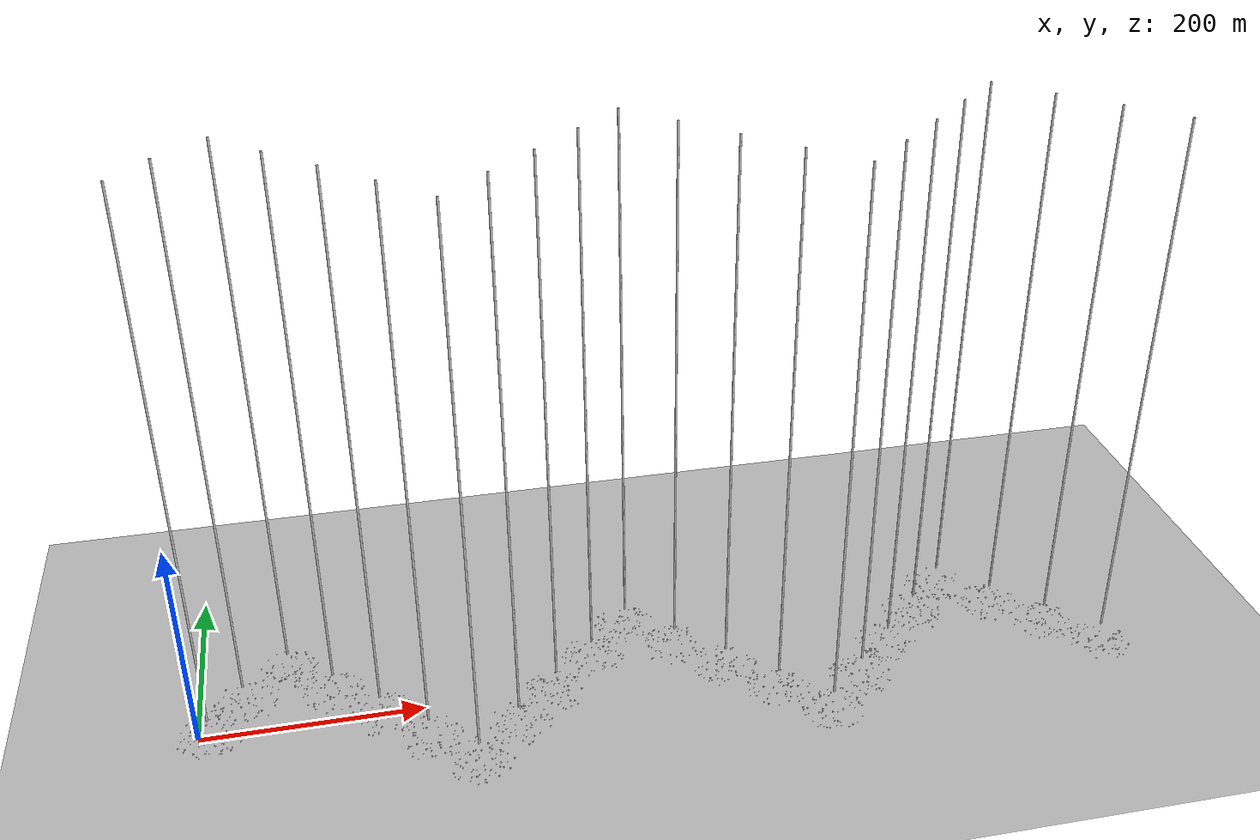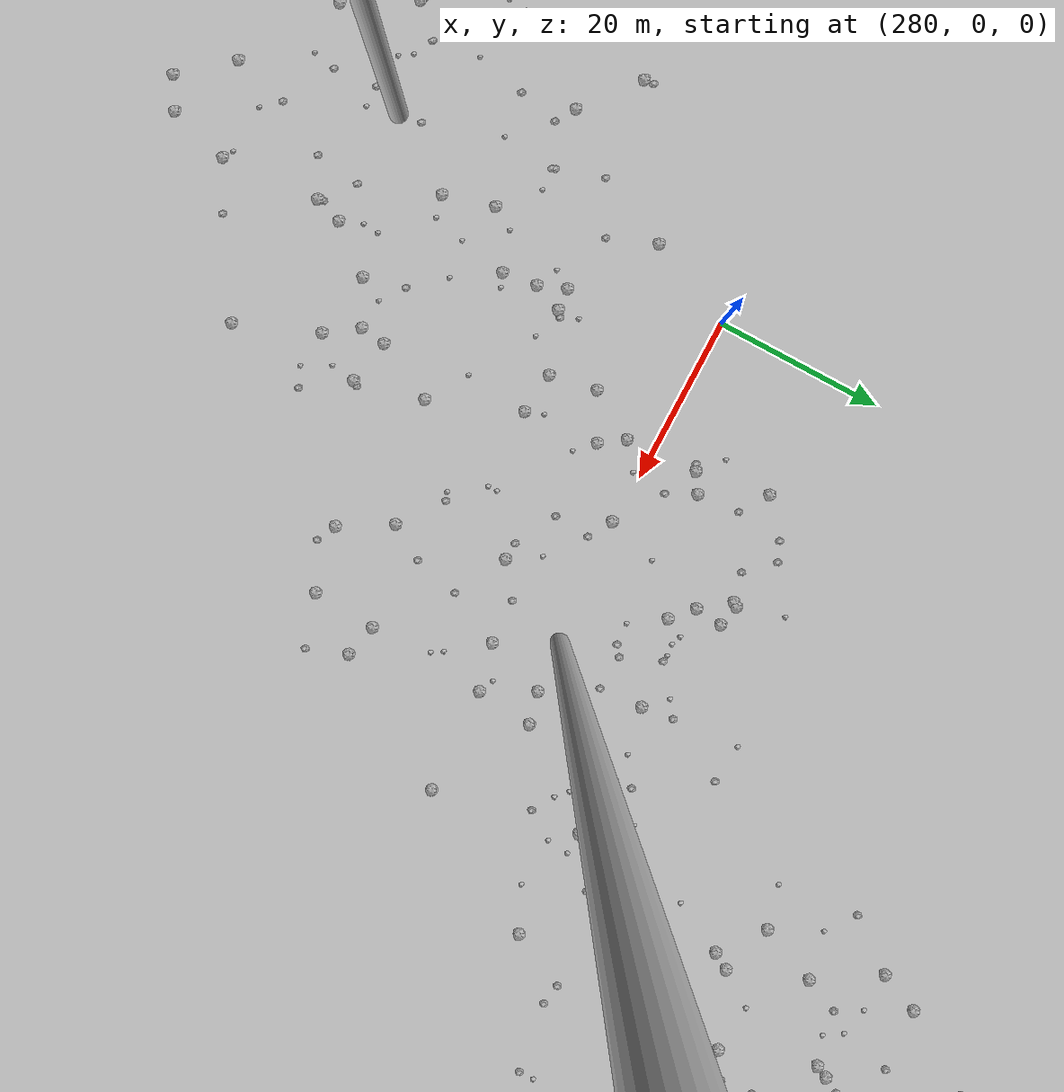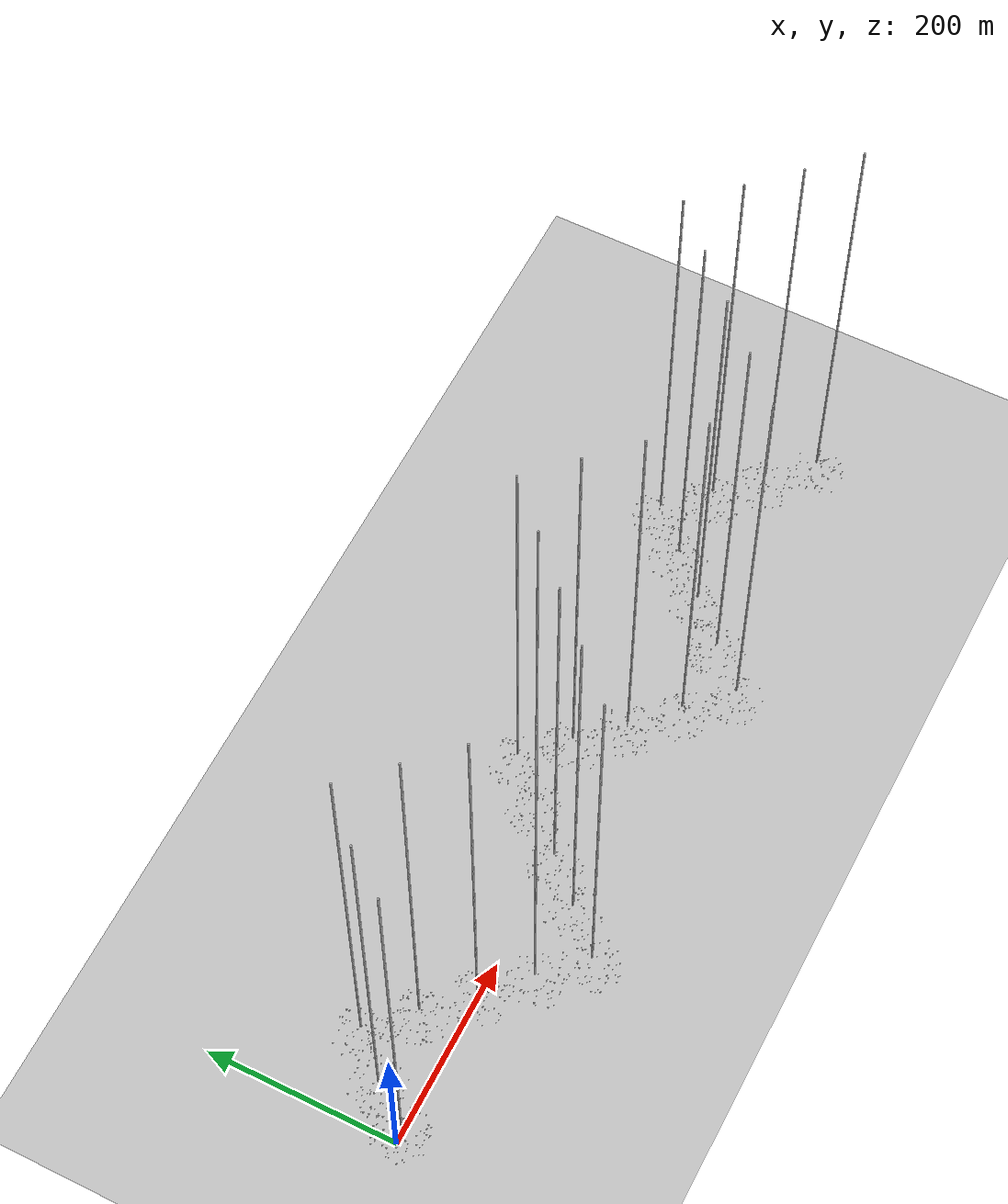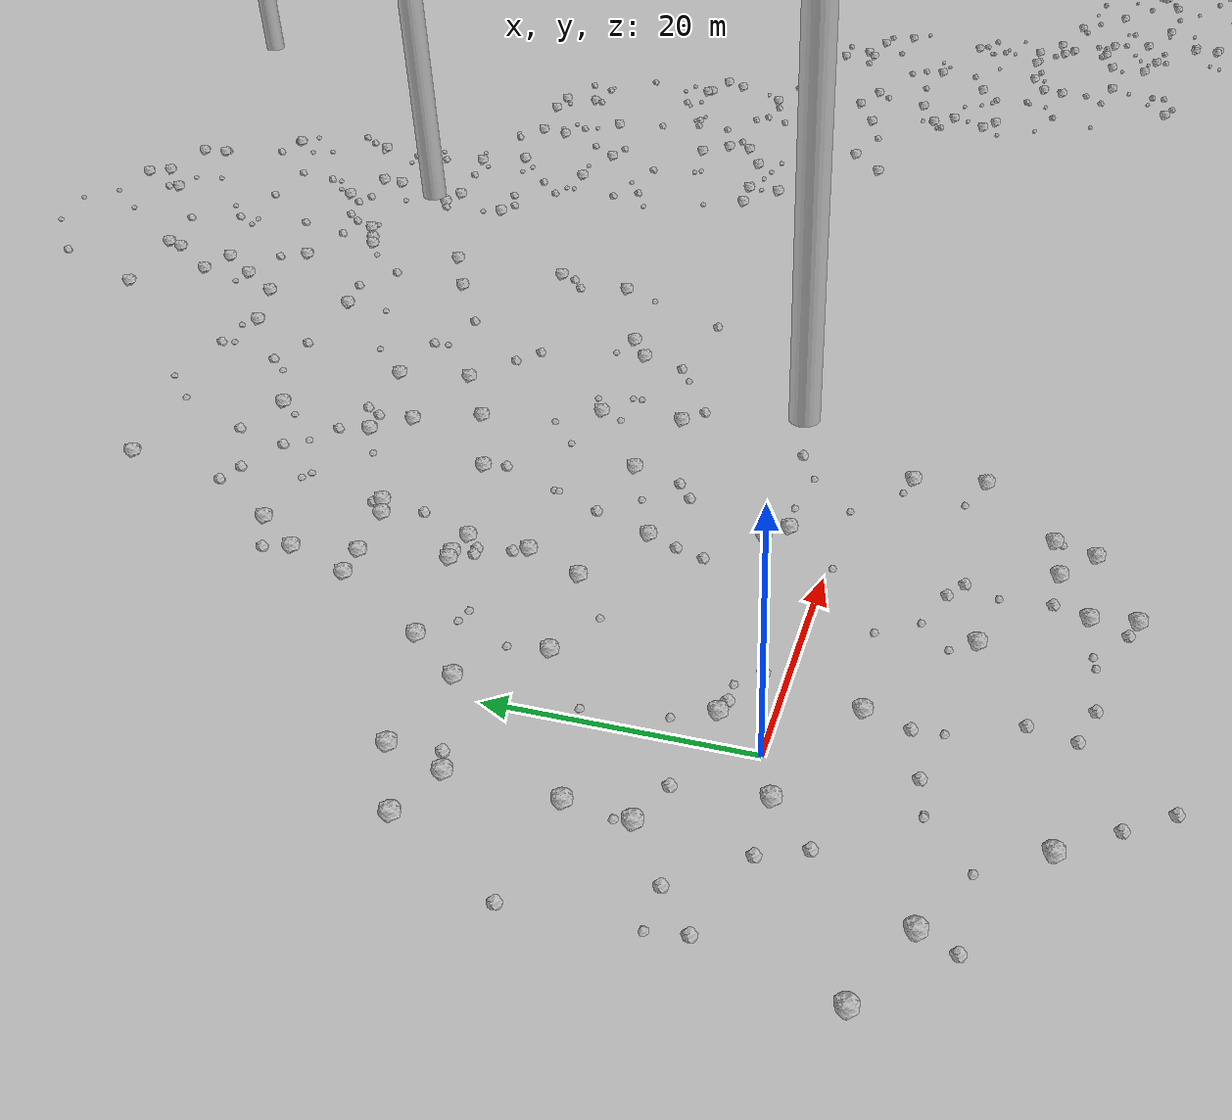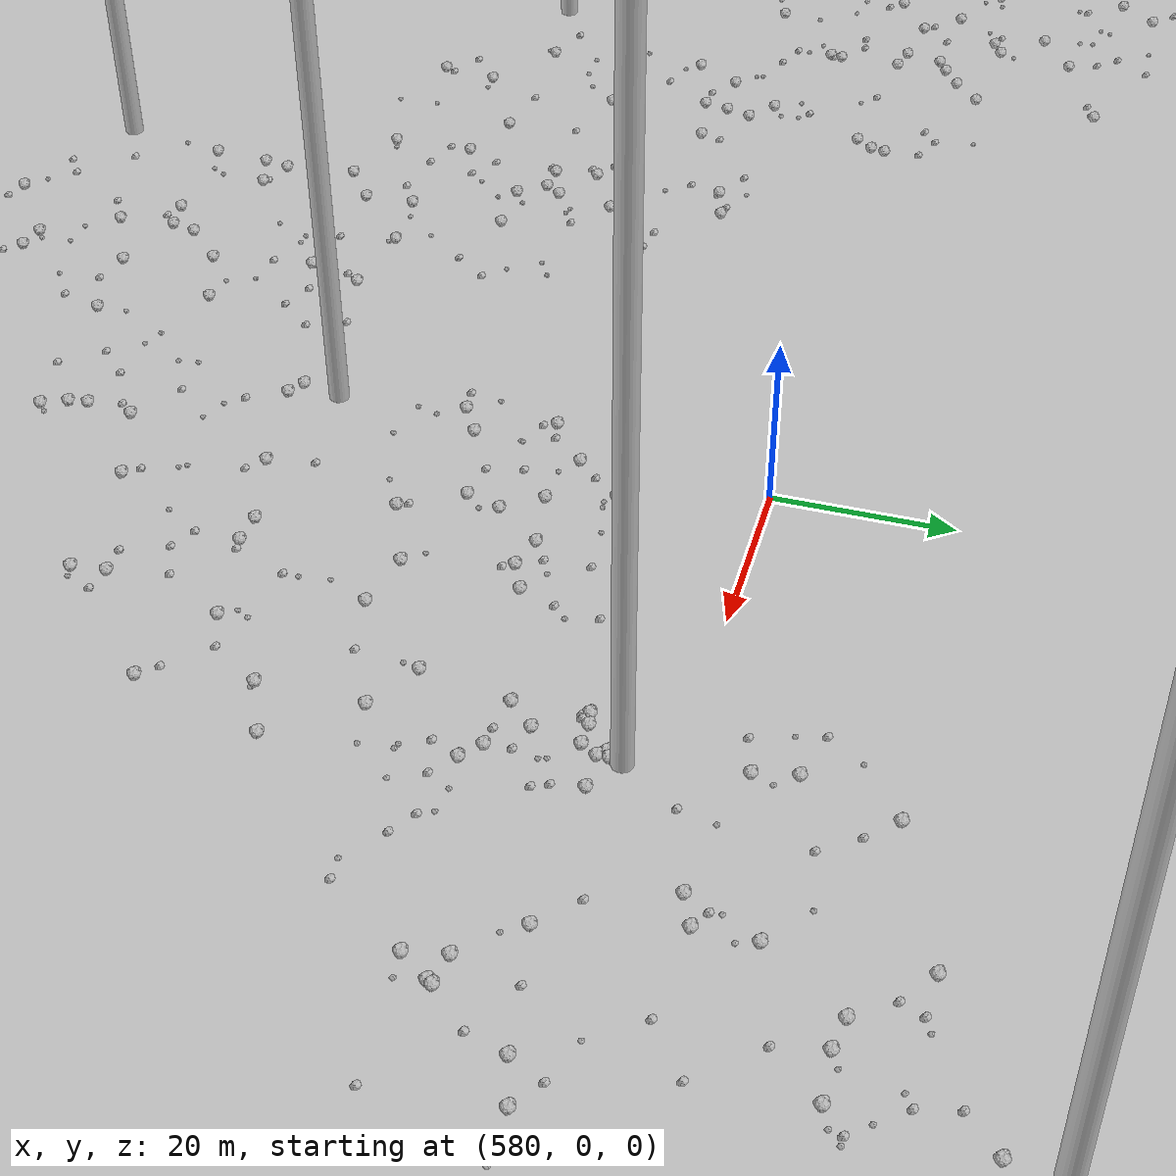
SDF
<sdf version="1.6">
 <world name="default">
  <include><uri>model://custom_ground</uri></include>
  <include><uri>model://sun</uri></include>
  <spherical_coordinates>
   <surface_model>EARTH_WGS84</surface_model>
   <latitude_deg>38.161479</latitude_deg>
   <longitude_deg>-122.454630</longitude_deg>
   <elevation>488.0</elevation>
   <heading_deg>90</heading_deg>
  </spherical_coordinates>
  <model name="rock1_0_0">
   <include><uri>model://rock1</uri><pose>31.323645814789323 19.270581954953627 0.5 0 0 0</pose></include>
  </model>
  <model name="rock1_0_1">
   <include><uri>model://rock1</uri><pose>-5.51867851214827 24.199380309814437 0.5 0 0 0</pose></include>
  </model>
  <model name="rock1_0_2">
   <include><uri>model://rock1</uri><pose>15.175881137884431 18.486177933784965 0.5 0 0 0</pose></include>
  </model>
  <model name="rock1_0_3">
   <include><uri>model://rock1</uri><pose>28.173100392939332 -20.36347644754197 0.5 0 0 0</pose></include>
  </model>
  <model name="rock1_0_4">
   <include><uri>model://rock1</uri><pose>3.121863633633474 3.861789008622715 0.5 0 0 0</pose></include>
  </model>
  <model name="rock1_0_5">
   <include><uri>model://rock1</uri><pose>20.025813773441968 -20.134038859779487 0.5 0 0 0</pose></include>
  </model>
  <model name="rock1_0_6">
   <include><uri>model://rock1</uri><pose>20.517614215999515 -23.662315917065147 0.5 0 0 0</pose></include>
  </model>
  <model name="rock1_0_7">
   <include><uri>model://rock1</uri><pose>36.7525975862281 -10.853067986479864 0.5 0 0 0</pose></include>
  </model>
  <model name="rock1_0_8">
   <include><uri>model://rock1</uri><pose>6.207886317455181 17.337839946644877 0.5 0 0 0</pose></include>
  </model>
  <model name="rock1_0_9">
   <include><uri>model://rock1</uri><pose>5.882170808075063 -5.615418716992654 0.5 0 0 0</pose></include>
  </model>
  <model name="rock1_0_10">
   <include><uri>model://rock1</uri><pose>-6.8765001596571445 19.56063270187701 0.5 0 0 0</pose></include>
  </model>
  <model name="rock1_0_11">
   <include><uri>model://rock1</uri><pose>-11.279204036337287 -11.75087149888611 0.5 0 0 0</pose></include>
  </model>
  <model name="rock1_0_12">
   <include><uri>model://rock1</uri><pose>-11.004823607466246 21.155434532249174 0.5 0 0 0</pose></include>
  </model>
  <model name="rock1_0_13">
   <include><uri>model://rock1</uri><pose>15.087824005755422 -12.379454636603313 0.5 0 0 0</pose></include>
  </model>
  <model name="rock1_0_14">
   <include><uri>model://rock1</uri><pose>29.330558159088866 -17.057179602932607 0.5 0 0 0</pose></include>
  </model>
  <model name="rock1_0_15">
   <include><uri>model://rock1</uri><pose>5.30753003283564 27.466645698513346 0.5 0 0 0</pose></include>
  </model>
  <model name="rock1_0_16">
   <include><uri>model://rock1</uri><pose>35.70783474936634 -4.6698337974231166 0.5 0 0 0</pose></include>
  </model>
  <model name="rock1_0_17">
   <include><uri>model://rock1</uri><pose>24.224916564953503 5.880709147007856 0.5 0 0 0</pose></include>
  </model>
  <model name="rock1_0_18">
   <include><uri>model://rock1</uri><pose>-7.2283357532736385 11.18781534681112 0.5 0 0 0</pose></include>
  </model>
  <model name="rock1_0_19">
   <include><uri>model://rock1</uri><pose>25.7898399033065 4.07598274443572 0.5 0 0 0</pose></include>
  </model>
  <model name="rock1_0_20">
   <include><uri>model://rock1</uri><pose>-3.5173196213842743 -18.947513594913982 0.5 0 0 0</pose></include>
  </model>
  <model name="rock1_0_21">
   <include><uri>model://rock1</uri><pose>-3.616944338547764 -1.471639838479323 0.5 0 0 0</pose></include>
  </model>
  <model name="rock1_0_22">
   <include><uri>model://rock1</uri><pose>1.7950533563550444 22.87518497777542 0.5 0 0 0</pose></include>
  </model>
  <model name="rock1_0_23">
   <include><uri>model://rock1</uri><pose>-7.721873380770772 6.338112571105356 0.5 0 0 0</pose></include>
  </model>
  <model name="rock1_0_24">
   <include><uri>model://rock1</uri><pose>-17.205234083135675 -8.898722600617987 0.5 0 0 0</pose></include>
  </model>
  <model name="rock1_0_25">
   <include><uri>model://rock1</uri><pose>24.921652989814746 -17.691668914133267 0.5 0 0 0</pose></include>
  </model>
  <model name="rock1_0_26">
   <include><uri>model://rock1</uri><pose>21.849157643020682 14.930381144137527 0.5 0 0 0</pose></include>
  </model>
  <model name="rock2_0_0">
   <include><uri>model://rock2</uri><pose>-0.7307273157601877 -22.915516298056616 0.3 0 0 0</pose></include>
  </model>
  <model name="rock2_0_1">
   <include><uri>model://rock2</uri><pose>0.424028639249574 -10.295067410250113 0.3 0 0 0</pose></include>
  </model>
  <model name="rock2_0_2">
   <include><uri>model://rock2</uri><pose>21.827459360780608 -10.720178018123669 0.3 0 0 0</pose></include>
  </model>
  <model name="rock2_0_3">
   <include><uri>model://rock2</uri><pose>20.63361047205484 12.239023379800692 0.3 0 0 0</pose></include>
  </model>
  <model name="rock2_0_4">
   <include><uri>model://rock2</uri><pose>-7.126189020396321 -4.753582078319926 0.3 0 0 0</pose></include>
  </model>
  <model name="rock2_0_5">
   <include><uri>model://rock2</uri><pose>-4.3265472841129835 5.041044674724866 0.3 0 0 0</pose></include>
  </model>
  <model name="rock2_0_6">
   <include><uri>model://rock2</uri><pose>7.131314616770926 -16.52749113577289 0.3 0 0 0</pose></include>
  </model>
  <model name="rock2_0_7">
   <include><uri>model://rock2</uri><pose>-14.999230052264902 0.543226788409978 0.3 0 0 0</pose></include>
  </model>
  <model name="rock2_0_8">
   <include><uri>model://rock2</uri><pose>-12.09512573367058 3.164204526269174 0.3 0 0 0</pose></include>
  </model>
  <model name="rock2_0_9">
   <include><uri>model://rock2</uri><pose>37.074717353086314 5.410952895898973 0.3 0 0 0</pose></include>
  </model>
  <model name="rock2_0_10">
   <include><uri>model://rock2</uri><pose>9.79796847268533 -20.998746368772245 0.3 0 0 0</pose></include>
  </model>
  <model name="rock2_0_11">
   <include><uri>model://rock2</uri><pose>1.5318023920667585 -26.18461459334759 0.3 0 0 0</pose></include>
  </model>
  <model name="rock2_0_12">
   <include><uri>model://rock2</uri><pose>-15.76342541456485 12.102808441204914 0.3 0 0 0</pose></include>
  </model>
  <model name="rock2_0_13">
   <include><uri>model://rock2</uri><pose>15.612397286862695 27.549698742222937 0.3 0 0 0</pose></include>
  </model>
  <model name="rock2_0_14">
   <include><uri>model://rock2</uri><pose>-12.338532149816704 -14.284027336692816 0.3 0 0 0</pose></include>
  </model>
  <model name="rock2_0_15">
   <include><uri>model://rock2</uri><pose>-5.250170940539963 20.379731272061065 0.3 0 0 0</pose></include>
  </model>
  <model name="rock2_0_16">
   <include><uri>model://rock2</uri><pose>4.787447187369295 -9.0629453077845 0.3 0 0 0</pose></include>
  </model>
  <model name="rock2_0_17">
   <include><uri>model://rock2</uri><pose>20.100494462749396 -9.551109147389155 0.3 0 0 0</pose></include>
  </model>
  <model name="rock2_0_18">
   <include><uri>model://rock2</uri><pose>4.3374109298442285 3.517286356166352 0.3 0 0 0</pose></include>
  </model>
  <model name="rock2_0_19">
   <include><uri>model://rock2</uri><pose>16.39168519735022 27.65048629688738 0.3 0 0 0</pose></include>
  </model>
  <model name="rock2_0_20">
   <include><uri>model://rock2</uri><pose>18.648964507505518 -23.012107528163995 0.3 0 0 0</pose></include>
  </model>
  <model name="rock2_0_21">
   <include><uri>model://rock2</uri><pose>7.81090608194782 1.8213301181370838 0.3 0 0 0</pose></include>
  </model>
  <model name="rock2_0_22">
   <include><uri>model://rock2</uri><pose>-8.463404297493016 -1.5622615191005629 0.3 0 0 0</pose></include>
  </model>
  <model name="rock2_0_23">
   <include><uri>model://rock2</uri><pose>19.82936894784855 9.747128215743523 0.3 0 0 0</pose></include>
  </model>
  <model name="rock2_0_24">
   <include><uri>model://rock2</uri><pose>23.947686294407937 20.20633049260335 0.3 0 0 0</pose></include>
  </model>
  <model name="rock2_0_25">
   <include><uri>model://rock2</uri><pose>6.456562637216628 -19.947571833452443 0.3 0 0 0</pose></include>
  </model>
  <model name="rock2_0_26">
   <include><uri>model://rock2</uri><pose>20.988222447892895 -17.45998482954664 0.3 0 0 0</pose></include>
  </model>
  <model name="rock3_0_0">
   <include><uri>model://rock3</uri><pose>10.637870214767968 15.094707127319062 0.2 0 0 0</pose></include>
  </model>
  <model name="rock3_0_1">
   <include><uri>model://rock3</uri><pose>5.841092741373593 20.53440016539794 0.2 0 0 0</pose></include>
  </model>
  <model name="rock3_0_2">
   <include><uri>model://rock3</uri><pose>-2.544820397323832 -11.004959543625588 0.2 0 0 0</pose></include>
  </model>
  <model name="rock3_0_3">
   <include><uri>model://rock3</uri><pose>26.124070395305417 24.787401066682 0.2 0 0 0</pose></include>
  </model>
  <model name="rock3_0_4">
   <include><uri>model://rock3</uri><pose>29.48677091957476 -0.32907853345127336 0.2 0 0 0</pose></include>
  </model>
  <model name="rock3_0_5">
   <include><uri>model://rock3</uri><pose>6.12883420780588 3.551681453912593 0.2 0 0 0</pose></include>
  </model>
  <model name="rock3_0_6">
   <include><uri>model://rock3</uri><pose>15.6565280522059 -20.650869245555157 0.2 0 0 0</pose></include>
  </model>
  <model name="rock3_0_7">
   <include><uri>model://rock3</uri><pose>-6.395547636673122 -14.466001680459424 0.2 0 0 0</pose></include>
  </model>
  <model name="rock3_0_8">
   <include><uri>model://rock3</uri><pose>5.012944849914376 -11.334281883173322 0.2 0 0 0</pose></include>
  </model>
  <model name="rock3_0_9">
   <include><uri>model://rock3</uri><pose>-15.37064736242507 3.1362396316396683 0.2 0 0 0</pose></include>
  </model>
  <model name="rock3_0_10">
   <include><uri>model://rock3</uri><pose>13.76583786686934 -10.508902331380504 0.2 0 0 0</pose></include>
  </model>
  <model name="rock3_0_11">
   <include><uri>model://rock3</uri><pose>-2.7025138992890625 -11.01191285577315 0.2 0 0 0</pose></include>
  </model>
  <model name="rock3_0_12">
   <include><uri>model://rock3</uri><pose>1.7682806651936005 6.865147930150563 0.2 0 0 0</pose></include>
  </model>
  <model name="rock3_0_13">
   <include><uri>model://rock3</uri><pose>29.146055403730116 -17.81902785290049 0.2 0 0 0</pose></include>
  </model>
  <model name="rock3_0_14">
   <include><uri>model://rock3</uri><pose>0.9941763201480747 13.111400443978141 0.2 0 0 0</pose></include>
  </model>
  <model name="rock3_0_15">
   <include><uri>model://rock3</uri><pose>16.31462093650542 -8.16775843262316 0.2 0 0 0</pose></include>
  </model>
  <model name="rock3_0_16">
   <include><uri>model://rock3</uri><pose>32.95684820455662 -9.48708321665702 0.2 0 0 0</pose></include>
  </model>
  <model name="rock3_0_17">
   <include><uri>model://rock3</uri><pose>8.933615344871228 24.901880027152707 0.2 0 0 0</pose></include>
  </model>
  <model name="rock3_0_18">
   <include><uri>model://rock3</uri><pose>14.433325372795721 -20.885076381693423 0.2 0 0 0</pose></include>
  </model>
  <model name="rock3_0_19">
   <include><uri>model://rock3</uri><pose>14.304579321104555 -4.972231886197928 0.2 0 0 0</pose></include>
  </model>
  <model name="rock3_0_20">
   <include><uri>model://rock3</uri><pose>33.50906934362879 -4.1646338703870605 0.2 0 0 0</pose></include>
  </model>
  <model name="rock3_0_21">
   <include><uri>model://rock3</uri><pose>33.682371442790874 3.6375625475686633 0.2 0 0 0</pose></include>
  </model>
  <model name="rock3_0_22">
   <include><uri>model://rock3</uri><pose>20.756199472293048 -13.466011943822792 0.2 0 0 0</pose></include>
  </model>
  <model name="rock3_0_23">
   <include><uri>model://rock3</uri><pose>-7.861737436257956 7.5737127485852085 0.2 0 0 0</pose></include>
  </model>
  <model name="rock3_0_24">
   <include><uri>model://rock3</uri><pose>21.256480477357883 -0.45166444560679864 0.2 0 0 0</pose></include>
  </model>
  <model name="rock3_0_25">
   <include><uri>model://rock3</uri><pose>7.589484793703047 25.19560779516715 0.2 0 0 0</pose></include>
  </model>
  <model name="rock3_0_26">
   <include><uri>model://rock3</uri><pose>28.7700956111186 4.2695152319148235 0.2 0 0 0</pose></include>
  </model>
  <model name="rock1_1_0">
   <include><uri>model://rock1</uri><pose>28.10083042952662 32.219100100237284 0.5 0 0 0</pose></include>
  </model>
  <model name="rock1_1_1">
   <include><uri>model://rock1</uri><pose>51.50070235492255 24.96189630196212 0.5 0 0 0</pose></include>
  </model>
  <model name="rock1_1_2">
   <include><uri>model://rock1</uri><pose>33.64918918187833 55.29809896225565 0.5 0 0 0</pose></include>
  </model>
  <model name="rock1_1_3">
   <include><uri>model://rock1</uri><pose>31.25709708378894 44.94623523002989 0.5 0 0 0</pose></include>
  </model>
  <model name="rock1_1_4">
   <include><uri>model://rock1</uri><pose>20.80382388310608 38.23244618753236 0.5 0 0 0</pose></include>
  </model>
  <model name="rock1_1_5">
   <include><uri>model://rock1</uri><pose>14.579894335209598 29.19491847886916 0.5 0 0 0</pose></include>
  </model>
  <model name="rock1_1_6">
   <include><uri>model://rock1</uri><pose>40.22655914225308 17.637596252091544 0.5 0 0 0</pose></include>
  </model>
  <model name="rock1_1_7">
   <include><uri>model://rock1</uri><pose>36.231516168980754 35.979742446411215 0.5 0 0 0</pose></include>
  </model>
  <model name="rock1_1_8">
   <include><uri>model://rock1</uri><pose>15.429188138892712 29.320066616864015 0.5 0 0 0</pose></include>
  </model>
  <model name="rock1_1_9">
   <include><uri>model://rock1</uri><pose>41.838161394119886 47.27684772743282 0.5 0 0 0</pose></include>
  </model>
  <model name="rock1_1_10">
   <include><uri>model://rock1</uri><pose>42.96291728581033 40.31543025675893 0.5 0 0 0</pose></include>
  </model>
  <model name="rock1_1_11">
   <include><uri>model://rock1</uri><pose>15.924546181151326 46.486666772180016 0.5 0 0 0</pose></include>
  </model>
  <model name="rock1_1_12">
   <include><uri>model://rock1</uri><pose>12.799757668925345 42.125527512596456 0.5 0 0 0</pose></include>
  </model>
  <model name="rock1_1_13">
   <include><uri>model://rock1</uri><pose>22.129019097668603 63.54497618914989 0.5 0 0 0</pose></include>
  </model>
  <model name="rock1_1_14">
   <include><uri>model://rock1</uri><pose>66.35134588289674 31.899403187263555 0.5 0 0 0</pose></include>
  </model>
  <model name="rock1_1_15">
   <include><uri>model://rock1</uri><pose>39.89327299216241 25.401506848930836 0.5 0 0 0</pose></include>
  </model>
  <model name="rock1_1_16">
   <include><uri>model://rock1</uri><pose>17.895148914895017 29.023316979641663 0.5 0 0 0</pose></include>
  </model>
  <model name="rock1_1_17">
   <include><uri>model://rock1</uri><pose>48.89116870691086 67.47108879503351 0.5 0 0 0</pose></include>
  </model>
  <model name="rock1_1_18">
   <include><uri>model://rock1</uri><pose>10.713325221117644 36.33866758083744 0.5 0 0 0</pose></include>
  </model>
  <model name="rock1_1_19">
   <include><uri>model://rock1</uri><pose>17.41152904360793 23.545469619358705 0.5 0 0 0</pose></include>
  </model>
  <model name="rock1_1_20">
   <include><uri>model://rock1</uri><pose>54.696596531889504 27.09683996318788 0.5 0 0 0</pose></include>
  </model>
  <model name="rock1_1_21">
   <include><uri>model://rock1</uri><pose>68.23814512960479 40.36207325680367 0.5 0 0 0</pose></include>
  </model>
  <model name="rock1_1_22">
   <include><uri>model://rock1</uri><pose>62.65905183885303 50.08397990657271 0.5 0 0 0</pose></include>
  </model>
  <model name="rock1_1_23">
   <include><uri>model://rock1</uri><pose>33.96404721486699 41.93946767199277 0.5 0 0 0</pose></include>
  </model>
  <model name="rock1_1_24">
   <include><uri>model://rock1</uri><pose>13.680910309144664 36.6695757161265 0.5 0 0 0</pose></include>
  </model>
  <model name="rock1_1_25">
   <include><uri>model://rock1</uri><pose>55.1303295379018 60.23095738578491 0.5 0 0 0</pose></include>
  </model>
  <model name="rock1_1_26">
   <include><uri>model://rock1</uri><pose>18.992177420946764 37.3523697441924 0.5 0 0 0</pose></include>
  </model>
  <model name="rock2_1_0">
   <include><uri>model://rock2</uri><pose>27.786668443686636 13.225362101852946 0.3 0 0 0</pose></include>
  </model>
  <model name="rock2_1_1">
   <include><uri>model://rock2</uri><pose>45.388636590335004 59.57503746485226 0.3 0 0 0</pose></include>
  </model>
  <model name="rock2_1_2">
   <include><uri>model://rock2</uri><pose>20.002368600015153 34.035511097519674 0.3 0 0 0</pose></include>
  </model>
  <model name="rock2_1_3">
   <include><uri>model://rock2</uri><pose>12.160074126637543 44.45994930124348 0.3 0 0 0</pose></include>
  </model>
  <model name="rock2_1_4">
   <include><uri>model://rock2</uri><pose>42.19994587266491 15.983874229196914 0.3 0 0 0</pose></include>
  </model>
  <model name="rock2_1_5">
   <include><uri>model://rock2</uri><pose>59.99843004559468 19.646846977507433 0.3 0 0 0</pose></include>
  </model>
  <model name="rock2_1_6">
   <include><uri>model://rock2</uri><pose>22.38431072503643 52.85947951245358 0.3 0 0 0</pose></include>
  </model>
  <model name="rock2_1_7">
   <include><uri>model://rock2</uri><pose>49.98443437233863 20.59227811030615 0.3 0 0 0</pose></include>
  </model>
  <model name="rock2_1_8">
   <include><uri>model://rock2</uri><pose>30.573178036811345 47.819680923178844 0.3 0 0 0</pose></include>
  </model>
  <model name="rock2_1_9">
   <include><uri>model://rock2</uri><pose>43.364533134226605 68.35011506128401 0.3 0 0 0</pose></include>
  </model>
  <model name="rock2_1_10">
   <include><uri>model://rock2</uri><pose>48.73987442713009 46.918007089141305 0.3 0 0 0</pose></include>
  </model>
  <model name="rock2_1_11">
   <include><uri>model://rock2</uri><pose>49.69452397268652 35.51893451417945 0.3 0 0 0</pose></include>
  </model>
  <model name="rock2_1_12">
   <include><uri>model://rock2</uri><pose>28.232367220147466 56.62218757193787 0.3 0 0 0</pose></include>
  </model>
  <model name="rock2_1_13">
   <include><uri>model://rock2</uri><pose>29.7477400999181 14.686798967502208 0.3 0 0 0</pose></include>
  </model>
  <model name="rock2_1_14">
   <include><uri>model://rock2</uri><pose>54.59666141354205 45.02374219766888 0.3 0 0 0</pose></include>
  </model>
  <model name="rock2_1_15">
   <include><uri>model://rock2</uri><pose>20.33893275313811 38.924570774414036 0.3 0 0 0</pose></include>
  </model>
  <model name="rock2_1_16">
   <include><uri>model://rock2</uri><pose>33.79680886842807 45.408458607119854 0.3 0 0 0</pose></include>
  </model>
  <model name="rock2_1_17">
   <include><uri>model://rock2</uri><pose>41.35772674096945 61.085637435532945 0.3 0 0 0</pose></include>
  </model>
  <model name="rock2_1_18">
   <include><uri>model://rock2</uri><pose>34.831446436752685 47.06575692994449 0.3 0 0 0</pose></include>
  </model>
  <model name="rock2_1_19">
   <include><uri>model://rock2</uri><pose>26.704718344321947 51.26611006882844 0.3 0 0 0</pose></include>
  </model>
  <model name="rock2_1_20">
   <include><uri>model://rock2</uri><pose>67.36071719873834 38.51148338585147 0.3 0 0 0</pose></include>
  </model>
  <model name="rock2_1_21">
   <include><uri>model://rock2</uri><pose>47.33822507671824 37.27291158599788 0.3 0 0 0</pose></include>
  </model>
  <model name="rock2_1_22">
   <include><uri>model://rock2</uri><pose>65.42478109206144 37.11096745410259 0.3 0 0 0</pose></include>
  </model>
  <model name="rock2_1_23">
   <include><uri>model://rock2</uri><pose>59.68897219926848 61.38096379133428 0.3 0 0 0</pose></include>
  </model>
  <model name="rock2_1_24">
   <include><uri>model://rock2</uri><pose>20.094996897461215 53.50245981141518 0.3 0 0 0</pose></include>
  </model>
  <model name="rock2_1_25">
   <include><uri>model://rock2</uri><pose>28.502548718521016 30.23628142313122 0.3 0 0 0</pose></include>
  </model>
  <model name="rock2_1_26">
   <include><uri>model://rock2</uri><pose>16.802933687355395 24.755474795661907 0.3 0 0 0</pose></include>
  </model>
  <model name="rock3_1_0">
   <include><uri>model://rock3</uri><pose>36.39654831176726 36.63201931995741 0.2 0 0 0</pose></include>
  </model>
  <model name="rock3_1_1">
   <include><uri>model://rock3</uri><pose>64.48583435251408 28.028215230431737 0.2 0 0 0</pose></include>
  </model>
  <model name="rock3_1_2">
   <include><uri>model://rock3</uri><pose>31.955173317479787 53.14680283402055 0.2 0 0 0</pose></include>
  </model>
  <model name="rock3_1_3">
   <include><uri>model://rock3</uri><pose>50.040026835523584 67.93142211488198 0.2 0 0 0</pose></include>
  </model>
  <model name="rock3_1_4">
   <include><uri>model://rock3</uri><pose>27.590091426157578 42.728126590725346 0.2 0 0 0</pose></include>
  </model>
  <model name="rock3_1_5">
   <include><uri>model://rock3</uri><pose>46.25420466492186 51.780445207263526 0.2 0 0 0</pose></include>
  </model>
  <model name="rock3_1_6">
   <include><uri>model://rock3</uri><pose>54.60097730769511 60.07206570659489 0.2 0 0 0</pose></include>
  </model>
  <model name="rock3_1_7">
   <include><uri>model://rock3</uri><pose>48.926296022524994 45.42284363561366 0.2 0 0 0</pose></include>
  </model>
  <model name="rock3_1_8">
   <include><uri>model://rock3</uri><pose>51.83639464064825 28.087720805319456 0.2 0 0 0</pose></include>
  </model>
  <model name="rock3_1_9">
   <include><uri>model://rock3</uri><pose>47.860441623527045 19.19293446303061 0.2 0 0 0</pose></include>
  </model>
  <model name="rock3_1_10">
   <include><uri>model://rock3</uri><pose>54.591992474729444 55.441063041335816 0.2 0 0 0</pose></include>
  </model>
  <model name="rock3_1_11">
   <include><uri>model://rock3</uri><pose>26.673126998773167 17.08357567335935 0.2 0 0 0</pose></include>
  </model>
  <model name="rock3_1_12">
   <include><uri>model://rock3</uri><pose>39.564025213708845 58.98075715032924 0.2 0 0 0</pose></include>
  </model>
  <model name="rock3_1_13">
   <include><uri>model://rock3</uri><pose>43.131345273000385 22.49911332218462 0.2 0 0 0</pose></include>
  </model>
  <model name="rock3_1_14">
   <include><uri>model://rock3</uri><pose>33.78467723259748 26.164447162936636 0.2 0 0 0</pose></include>
  </model>
  <model name="rock3_1_15">
   <include><uri>model://rock3</uri><pose>32.18328334350759 64.97059759275481 0.2 0 0 0</pose></include>
  </model>
  <model name="rock3_1_16">
   <include><uri>model://rock3</uri><pose>38.8884097623413 23.18487461906773 0.2 0 0 0</pose></include>
  </model>
  <model name="rock3_1_17">
   <include><uri>model://rock3</uri><pose>23.153534371708606 46.32258013188887 0.2 0 0 0</pose></include>
  </model>
  <model name="rock3_1_18">
   <include><uri>model://rock3</uri><pose>43.16116974339944 23.393239543019618 0.2 0 0 0</pose></include>
  </model>
  <model name="rock3_1_19">
   <include><uri>model://rock3</uri><pose>43.76593512288524 67.09253862043715 0.2 0 0 0</pose></include>
  </model>
  <model name="rock3_1_20">
   <include><uri>model://rock3</uri><pose>42.327215230217035 26.63140469636991 0.2 0 0 0</pose></include>
  </model>
  <model name="rock3_1_21">
   <include><uri>model://rock3</uri><pose>26.131489630518104 24.372739975593618 0.2 0 0 0</pose></include>
  </model>
  <model name="rock3_1_22">
   <include><uri>model://rock3</uri><pose>28.11596677643037 49.42549773189361 0.2 0 0 0</pose></include>
  </model>
  <model name="rock3_1_23">
   <include><uri>model://rock3</uri><pose>37.09213286655276 29.022659451134388 0.2 0 0 0</pose></include>
  </model>
  <model name="rock3_1_24">
   <include><uri>model://rock3</uri><pose>22.295772067877486 46.790998773361025 0.2 0 0 0</pose></include>
  </model>
  <model name="rock3_1_25">
   <include><uri>model://rock3</uri><pose>47.53198916472818 68.62060472138462 0.2 0 0 0</pose></include>
  </model>
  <model name="rock3_1_26">
   <include><uri>model://rock3</uri><pose>35.73043819742481 68.71737844415031 0.2 0 0 0</pose></include>
  </model>
  <model name="rock1_2_0">
   <include><uri>model://rock1</uri><pose>88.37150764203656 66.12866795243397 0.5 0 0 0</pose></include>
  </model>
  <model name="rock1_2_1">
   <include><uri>model://rock1</uri><pose>95.41934329484513 101.34001560832219 0.5 0 0 0</pose></include>
  </model>
  <model name="rock1_2_2">
   <include><uri>model://rock1</uri><pose>72.46035466215291 66.36073334485583 0.5 0 0 0</pose></include>
  </model>
  <model name="rock1_2_3">
   <include><uri>model://rock1</uri><pose>95.17038528272236 104.48995031382599 0.5 0 0 0</pose></include>
  </model>
  <model name="rock1_2_4">
   <include><uri>model://rock1</uri><pose>85.8688533810373 63.093269363673166 0.5 0 0 0</pose></include>
  </model>
  <model name="rock1_2_5">
   <include><uri>model://rock1</uri><pose>75.45897279835134 68.08843314588411 0.5 0 0 0</pose></include>
  </model>
  <model name="rock1_2_6">
   <include><uri>model://rock1</uri><pose>81.68500230345316 99.49570902699386 0.5 0 0 0</pose></include>
  </model>
  <model name="rock1_2_7">
   <include><uri>model://rock1</uri><pose>91.06646532713677 74.44177556553288 0.5 0 0 0</pose></include>
  </model>
  <model name="rock1_2_8">
   <include><uri>model://rock1</uri><pose>88.84798287342576 62.32150017265829 0.5 0 0 0</pose></include>
  </model>
  <model name="rock1_2_9">
   <include><uri>model://rock1</uri><pose>63.06300306076295 79.86551181789 0.5 0 0 0</pose></include>
  </model>
  <model name="rock1_2_10">
   <include><uri>model://rock1</uri><pose>85.69160700451013 106.79875444050134 0.5 0 0 0</pose></include>
  </model>
  <model name="rock1_2_11">
   <include><uri>model://rock1</uri><pose>55.82673713703013 70.22667704161633 0.5 0 0 0</pose></include>
  </model>
  <model name="rock1_2_12">
   <include><uri>model://rock1</uri><pose>64.14744040383648 87.26000448784097 0.5 0 0 0</pose></include>
  </model>
  <model name="rock1_2_13">
   <include><uri>model://rock1</uri><pose>65.02139056486067 89.41741009713638 0.5 0 0 0</pose></include>
  </model>
  <model name="rock1_2_14">
   <include><uri>model://rock1</uri><pose>59.23042510557349 80.7669861479475 0.5 0 0 0</pose></include>
  </model>
  <model name="rock1_2_15">
   <include><uri>model://rock1</uri><pose>65.97533644811787 71.46446221937678 0.5 0 0 0</pose></include>
  </model>
  <model name="rock1_2_16">
   <include><uri>model://rock1</uri><pose>101.63259053142757 64.94808729221573 0.5 0 0 0</pose></include>
  </model>
  <model name="rock1_2_17">
   <include><uri>model://rock1</uri><pose>69.45847551744396 53.75779231339925 0.5 0 0 0</pose></include>
  </model>
  <model name="rock1_2_18">
   <include><uri>model://rock1</uri><pose>84.69896377839001 54.90960276312022 0.5 0 0 0</pose></include>
  </model>
  <model name="rock1_2_19">
   <include><uri>model://rock1</uri><pose>85.04810366098434 76.22221074633342 0.5 0 0 0</pose></include>
  </model>
  <model name="rock1_2_20">
   <include><uri>model://rock1</uri><pose>53.96031928093954 86.97310865554743 0.5 0 0 0</pose></include>
  </model>
  <model name="rock1_2_21">
   <include><uri>model://rock1</uri><pose>87.04356260862926 104.41851078704238 0.5 0 0 0</pose></include>
  </model>
  <model name="rock1_2_22">
   <include><uri>model://rock1</uri><pose>102.78940478226701 80.13778800396157 0.5 0 0 0</pose></include>
  </model>
  <model name="rock1_2_23">
   <include><uri>model://rock1</uri><pose>70.9284802873731 65.5686799748545 0.5 0 0 0</pose></include>
  </model>
  <model name="rock1_2_24">
   <include><uri>model://rock1</uri><pose>90.53695157034454 71.64876936884514 0.5 0 0 0</pose></include>
  </model>
  <model name="rock1_2_25">
   <include><uri>model://rock1</uri><pose>59.3865984848603 75.12219947159788 0.5 0 0 0</pose></include>
  </model>
  <model name="rock1_2_26">
   <include><uri>model://rock1</uri><pose>102.16308480173912 93.2401412430837 0.5 0 0 0</pose></include>
  </model>
  <model name="rock2_2_0">
   <include><uri>model://rock2</uri><pose>104.57003503200627 83.02728901039194 0.3 0 0 0</pose></include>
  </model>
  <model name="rock2_2_1">
   <include><uri>model://rock2</uri><pose>74.97436626312762 76.97446186205798 0.3 0 0 0</pose></include>
  </model>
  <model name="rock2_2_2">
   <include><uri>model://rock2</uri><pose>74.51268767972931 85.87825175994365 0.3 0 0 0</pose></include>
  </model>
  <model name="rock2_2_3">
   <include><uri>model://rock2</uri><pose>89.59444831114499 81.47910291637541 0.3 0 0 0</pose></include>
  </model>
  <model name="rock2_2_4">
   <include><uri>model://rock2</uri><pose>84.22932376118855 62.3428986033983 0.3 0 0 0</pose></include>
  </model>
  <model name="rock2_2_5">
   <include><uri>model://rock2</uri><pose>85.04730221866816 73.31120709582308 0.3 0 0 0</pose></include>
  </model>
  <model name="rock2_2_6">
   <include><uri>model://rock2</uri><pose>96.12470870584501 101.39127508425557 0.3 0 0 0</pose></include>
  </model>
  <model name="rock2_2_7">
   <include><uri>model://rock2</uri><pose>102.11492706685635 93.81068571872092 0.3 0 0 0</pose></include>
  </model>
  <model name="rock2_2_8">
   <include><uri>model://rock2</uri><pose>72.97695643794843 70.76697255948581 0.3 0 0 0</pose></include>
  </model>
  <model name="rock2_2_9">
   <include><uri>model://rock2</uri><pose>90.31027130571024 55.545965729271266 0.3 0 0 0</pose></include>
  </model>
  <model name="rock2_2_10">
   <include><uri>model://rock2</uri><pose>81.70003628074775 101.14166795740283 0.3 0 0 0</pose></include>
  </model>
  <model name="rock2_2_11">
   <include><uri>model://rock2</uri><pose>78.90737626255641 72.89966456823689 0.3 0 0 0</pose></include>
  </model>
  <model name="rock2_2_12">
   <include><uri>model://rock2</uri><pose>90.78038812627594 86.54789609265241 0.3 0 0 0</pose></include>
  </model>
  <model name="rock2_2_13">
   <include><uri>model://rock2</uri><pose>77.04786908437208 71.00073991383732 0.3 0 0 0</pose></include>
  </model>
  <model name="rock2_2_14">
   <include><uri>model://rock2</uri><pose>96.14258717434456 63.767620217078246 0.3 0 0 0</pose></include>
  </model>
  <model name="rock2_2_15">
   <include><uri>model://rock2</uri><pose>100.83844900861016 70.12684682159178 0.3 0 0 0</pose></include>
  </model>
  <model name="rock2_2_16">
   <include><uri>model://rock2</uri><pose>82.45626051093821 85.78620910906903 0.3 0 0 0</pose></include>
  </model>
  <model name="rock2_2_17">
   <include><uri>model://rock2</uri><pose>59.91146030926808 99.82957048130748 0.3 0 0 0</pose></include>
  </model>
  <model name="rock2_2_18">
   <include><uri>model://rock2</uri><pose>64.00929596585706 58.952778151835105 0.3 0 0 0</pose></include>
  </model>
  <model name="rock2_2_19">
   <include><uri>model://rock2</uri><pose>82.966653623957 74.0133517650566 0.3 0 0 0</pose></include>
  </model>
  <model name="rock2_2_20">
   <include><uri>model://rock2</uri><pose>97.70828794927286 93.96337901067926 0.3 0 0 0</pose></include>
  </model>
  <model name="rock2_2_21">
   <include><uri>model://rock2</uri><pose>106.37992168171562 85.1735600738919 0.3 0 0 0</pose></include>
  </model>
  <model name="rock2_2_22">
   <include><uri>model://rock2</uri><pose>64.6510908192283 74.30878786976845 0.3 0 0 0</pose></include>
  </model>
  <model name="rock2_2_23">
   <include><uri>model://rock2</uri><pose>87.03516964502802 54.13370730907198 0.3 0 0 0</pose></include>
  </model>
  <model name="rock2_2_24">
   <include><uri>model://rock2</uri><pose>72.62545154990535 91.62542387682606 0.3 0 0 0</pose></include>
  </model>
  <model name="rock2_2_25">
   <include><uri>model://rock2</uri><pose>71.44280621617452 65.93900048708791 0.3 0 0 0</pose></include>
  </model>
  <model name="rock2_2_26">
   <include><uri>model://rock2</uri><pose>101.08764601241828 74.59660142713777 0.3 0 0 0</pose></include>
  </model>
  <model name="rock3_2_0">
   <include><uri>model://rock3</uri><pose>74.6398415526205 83.46837979273701 0.2 0 0 0</pose></include>
  </model>
  <model name="rock3_2_1">
   <include><uri>model://rock3</uri><pose>84.39908281173291 57.30750808160728 0.2 0 0 0</pose></include>
  </model>
  <model name="rock3_2_2">
   <include><uri>model://rock3</uri><pose>68.20677872764381 63.677186977431575 0.2 0 0 0</pose></include>
  </model>
  <model name="rock3_2_3">
   <include><uri>model://rock3</uri><pose>78.75089106852238 106.60033082118092 0.2 0 0 0</pose></include>
  </model>
  <model name="rock3_2_4">
   <include><uri>model://rock3</uri><pose>99.28135316487146 58.10549973705848 0.2 0 0 0</pose></include>
  </model>
  <model name="rock3_2_5">
   <include><uri>model://rock3</uri><pose>104.99181595158514 66.05793511805379 0.2 0 0 0</pose></include>
  </model>
  <model name="rock3_2_6">
   <include><uri>model://rock3</uri><pose>98.86205812196928 89.71535804325936 0.2 0 0 0</pose></include>
  </model>
  <model name="rock3_2_7">
   <include><uri>model://rock3</uri><pose>105.33474706859965 74.51151587657414 0.2 0 0 0</pose></include>
  </model>
  <model name="rock3_2_8">
   <include><uri>model://rock3</uri><pose>85.64458153979439 99.6652288286786 0.2 0 0 0</pose></include>
  </model>
  <model name="rock3_2_9">
   <include><uri>model://rock3</uri><pose>57.35803690029456 75.6494208100515 0.2 0 0 0</pose></include>
  </model>
  <model name="rock3_2_10">
   <include><uri>model://rock3</uri><pose>89.49635281792938 80.09879390652598 0.2 0 0 0</pose></include>
  </model>
  <model name="rock3_2_11">
   <include><uri>model://rock3</uri><pose>68.05181203278332 107.20385763310992 0.2 0 0 0</pose></include>
  </model>
  <model name="rock3_2_12">
   <include><uri>model://rock3</uri><pose>98.5949455289842 74.3292147125789 0.2 0 0 0</pose></include>
  </model>
  <model name="rock3_2_13">
   <include><uri>model://rock3</uri><pose>75.3935486416114 109.45697587835237 0.2 0 0 0</pose></include>
  </model>
  <model name="rock3_2_14">
   <include><uri>model://rock3</uri><pose>86.29407135002666 96.20014081457768 0.2 0 0 0</pose></include>
  </model>
  <model name="rock3_2_15">
   <include><uri>model://rock3</uri><pose>65.57055401462583 71.33270748647931 0.2 0 0 0</pose></include>
  </model>
  <model name="rock3_2_16">
   <include><uri>model://rock3</uri><pose>103.90320914744922 71.88693057960222 0.2 0 0 0</pose></include>
  </model>
  <model name="rock3_2_17">
   <include><uri>model://rock3</uri><pose>72.85760710935749 83.24568163372133 0.2 0 0 0</pose></include>
  </model>
  <model name="rock3_2_18">
   <include><uri>model://rock3</uri><pose>104.73903463662508 92.08379504833842 0.2 0 0 0</pose></include>
  </model>
  <model name="rock3_2_19">
   <include><uri>model://rock3</uri><pose>99.91903430393943 63.47792684164576 0.2 0 0 0</pose></include>
  </model>
  <model name="rock3_2_20">
   <include><uri>model://rock3</uri><pose>77.83996696782812 88.64394826655015 0.2 0 0 0</pose></include>
  </model>
  <model name="rock3_2_21">
   <include><uri>model://rock3</uri><pose>85.21756089879298 68.48445766370733 0.2 0 0 0</pose></include>
  </model>
  <model name="rock3_2_22">
   <include><uri>model://rock3</uri><pose>76.74816068975456 67.88823269607504 0.2 0 0 0</pose></include>
  </model>
  <model name="rock3_2_23">
   <include><uri>model://rock3</uri><pose>101.86387624508737 80.16882808124298 0.2 0 0 0</pose></include>
  </model>
  <model name="rock3_2_24">
   <include><uri>model://rock3</uri><pose>73.94691271487346 100.88556466933812 0.2 0 0 0</pose></include>
  </model>
  <model name="rock3_2_25">
   <include><uri>model://rock3</uri><pose>99.77622936769687 87.13572976483066 0.2 0 0 0</pose></include>
  </model>
  <model name="rock3_2_26">
   <include><uri>model://rock3</uri><pose>86.7831749677809 78.59301803409528 0.2 0 0 0</pose></include>
  </model>
  <model name="rock1_3_0">
   <include><uri>model://rock1</uri><pose>131.58889660722298 63.93386104876088 0.5 0 0 0</pose></include>
  </model>
  <model name="rock1_3_1">
   <include><uri>model://rock1</uri><pose>100.87717450615489 26.63106083804478 0.5 0 0 0</pose></include>
  </model>
  <model name="rock1_3_2">
   <include><uri>model://rock1</uri><pose>146.63178447141956 41.72762457707888 0.5 0 0 0</pose></include>
  </model>
  <model name="rock1_3_3">
   <include><uri>model://rock1</uri><pose>113.22199969153333 36.57736236281124 0.5 0 0 0</pose></include>
  </model>
  <model name="rock1_3_4">
   <include><uri>model://rock1</uri><pose>144.63756147273355 38.85042662892195 0.5 0 0 0</pose></include>
  </model>
  <model name="rock1_3_5">
   <include><uri>model://rock1</uri><pose>107.87657853493361 48.143455078045264 0.5 0 0 0</pose></include>
  </model>
  <model name="rock1_3_6">
   <include><uri>model://rock1</uri><pose>115.74802323181902 30.42126266543184 0.5 0 0 0</pose></include>
  </model>
  <model name="rock1_3_7">
   <include><uri>model://rock1</uri><pose>111.65081093054951 11.356808848178746 0.5 0 0 0</pose></include>
  </model>
  <model name="rock1_3_8">
   <include><uri>model://rock1</uri><pose>138.94499274489877 31.6690671131284 0.5 0 0 0</pose></include>
  </model>
  <model name="rock1_3_9">
   <include><uri>model://rock1</uri><pose>140.93411476701075 19.02748675039584 0.5 0 0 0</pose></include>
  </model>
  <model name="rock1_3_10">
   <include><uri>model://rock1</uri><pose>99.5653422261529 49.50587134481705 0.5 0 0 0</pose></include>
  </model>
  <model name="rock1_3_11">
   <include><uri>model://rock1</uri><pose>121.38493208054402 51.77572530833886 0.5 0 0 0</pose></include>
  </model>
  <model name="rock1_3_12">
   <include><uri>model://rock1</uri><pose>141.3500917110732 43.03540696542427 0.5 0 0 0</pose></include>
  </model>
  <model name="rock1_3_13">
   <include><uri>model://rock1</uri><pose>116.33702099742202 61.723598940720706 0.5 0 0 0</pose></include>
  </model>
  <model name="rock1_3_14">
   <include><uri>model://rock1</uri><pose>140.65294390363545 43.60915047869593 0.5 0 0 0</pose></include>
  </model>
  <model name="rock1_3_15">
   <include><uri>model://rock1</uri><pose>109.91645670639264 27.65805649813441 0.5 0 0 0</pose></include>
  </model>
  <model name="rock1_3_16">
   <include><uri>model://rock1</uri><pose>116.05452109124614 33.443033790752246 0.5 0 0 0</pose></include>
  </model>
  <model name="rock1_3_17">
   <include><uri>model://rock1</uri><pose>100.57882131783362 22.687328676218037 0.5 0 0 0</pose></include>
  </model>
  <model name="rock1_3_18">
   <include><uri>model://rock1</uri><pose>131.6041005570114 59.241871146847416 0.5 0 0 0</pose></include>
  </model>
  <model name="rock1_3_19">
   <include><uri>model://rock1</uri><pose>115.36148369035138 58.01474193936211 0.5 0 0 0</pose></include>
  </model>
  <model name="rock1_3_20">
   <include><uri>model://rock1</uri><pose>132.781638201977 15.830952418821013 0.5 0 0 0</pose></include>
  </model>
  <model name="rock1_3_21">
   <include><uri>model://rock1</uri><pose>95.7160104849437 26.154418338914184 0.5 0 0 0</pose></include>
  </model>
  <model name="rock1_3_22">
   <include><uri>model://rock1</uri><pose>126.76574041696833 63.77718055777574 0.5 0 0 0</pose></include>
  </model>
  <model name="rock1_3_23">
   <include><uri>model://rock1</uri><pose>103.84458688172175 59.531785359774574 0.5 0 0 0</pose></include>
  </model>
  <model name="rock1_3_24">
   <include><uri>model://rock1</uri><pose>137.51951475447325 25.52512221952574 0.5 0 0 0</pose></include>
  </model>
  <model name="rock1_3_25">
   <include><uri>model://rock1</uri><pose>102.51918831302811 18.564497210148982 0.5 0 0 0</pose></include>
  </model>
  <model name="rock1_3_26">
   <include><uri>model://rock1</uri><pose>117.44984919623778 15.497097577885853 0.5 0 0 0</pose></include>
  </model>
  <model name="rock2_3_0">
   <include><uri>model://rock2</uri><pose>126.85781936532535 40.927705006251436 0.3 0 0 0</pose></include>
  </model>
  <model name="rock2_3_1">
   <include><uri>model://rock2</uri><pose>95.33696970154416 40.25430700093288 0.3 0 0 0</pose></include>
  </model>
  <model name="rock2_3_2">
   <include><uri>model://rock2</uri><pose>128.93495291851949 28.3589280583834 0.3 0 0 0</pose></include>
  </model>
  <model name="rock2_3_3">
   <include><uri>model://rock2</uri><pose>104.24098637049258 41.02217471398315 0.3 0 0 0</pose></include>
  </model>
  <model name="rock2_3_4">
   <include><uri>model://rock2</uri><pose>137.89863641919064 58.976938848365144 0.3 0 0 0</pose></include>
  </model>
  <model name="rock2_3_5">
   <include><uri>model://rock2</uri><pose>92.43109136976628 50.71328186594709 0.3 0 0 0</pose></include>
  </model>
  <model name="rock2_3_6">
   <include><uri>model://rock2</uri><pose>118.74329891626691 32.23448143373635 0.3 0 0 0</pose></include>
  </model>
  <model name="rock2_3_7">
   <include><uri>model://rock2</uri><pose>130.8465230271621 31.320712024843754 0.3 0 0 0</pose></include>
  </model>
  <model name="rock2_3_8">
   <include><uri>model://rock2</uri><pose>123.55724387274402 35.79643148650762 0.3 0 0 0</pose></include>
  </model>
  <model name="rock2_3_9">
   <include><uri>model://rock2</uri><pose>119.03990162253237 21.042880763958497 0.3 0 0 0</pose></include>
  </model>
  <model name="rock2_3_10">
   <include><uri>model://rock2</uri><pose>135.6795044945496 30.760498637487984 0.3 0 0 0</pose></include>
  </model>
  <model name="rock2_3_11">
   <include><uri>model://rock2</uri><pose>124.23300641599732 40.337146244601065 0.3 0 0 0</pose></include>
  </model>
  <model name="rock2_3_12">
   <include><uri>model://rock2</uri><pose>111.43602576187224 47.57781294264912 0.3 0 0 0</pose></include>
  </model>
  <model name="rock2_3_13">
   <include><uri>model://rock2</uri><pose>111.42669685287002 51.94231504902072 0.3 0 0 0</pose></include>
  </model>
  <model name="rock2_3_14">
   <include><uri>model://rock2</uri><pose>131.38005620571636 58.205159356773585 0.3 0 0 0</pose></include>
  </model>
  <model name="rock2_3_15">
   <include><uri>model://rock2</uri><pose>134.7971154268418 45.32232594017407 0.3 0 0 0</pose></include>
  </model>
  <model name="rock2_3_16">
   <include><uri>model://rock2</uri><pose>93.51099569698707 43.07112795190807 0.3 0 0 0</pose></include>
  </model>
  <model name="rock2_3_17">
   <include><uri>model://rock2</uri><pose>143.9445735410514 53.35697997422543 0.3 0 0 0</pose></include>
  </model>
  <model name="rock2_3_18">
   <include><uri>model://rock2</uri><pose>95.95120963258286 53.7018492470942 0.3 0 0 0</pose></include>
  </model>
  <model name="rock2_3_19">
   <include><uri>model://rock2</uri><pose>146.88707428378353 30.19259679312716 0.3 0 0 0</pose></include>
  </model>
  <model name="rock2_3_20">
   <include><uri>model://rock2</uri><pose>133.0093270629967 59.94806017362964 0.3 0 0 0</pose></include>
  </model>
  <model name="rock2_3_21">
   <include><uri>model://rock2</uri><pose>122.72942789565255 45.511377141970264 0.3 0 0 0</pose></include>
  </model>
  <model name="rock2_3_22">
   <include><uri>model://rock2</uri><pose>118.51629561117731 56.22611112048114 0.3 0 0 0</pose></include>
  </model>
  <model name="rock2_3_23">
   <include><uri>model://rock2</uri><pose>125.32763009432833 13.680768396816363 0.3 0 0 0</pose></include>
  </model>
  <model name="rock2_3_24">
   <include><uri>model://rock2</uri><pose>129.1400477018754 32.78019238442111 0.3 0 0 0</pose></include>
  </model>
  <model name="rock2_3_25">
   <include><uri>model://rock2</uri><pose>139.62927903944671 62.375709898957496 0.3 0 0 0</pose></include>
  </model>
  <model name="rock2_3_26">
   <include><uri>model://rock2</uri><pose>112.43519758669085 63.94489543289135 0.3 0 0 0</pose></include>
  </model>
  <model name="rock3_3_0">
   <include><uri>model://rock3</uri><pose>126.91949566293403 41.62080611339856 0.2 0 0 0</pose></include>
  </model>
  <model name="rock3_3_1">
   <include><uri>model://rock3</uri><pose>100.90991833074787 25.015633277793263 0.2 0 0 0</pose></include>
  </model>
  <model name="rock3_3_2">
   <include><uri>model://rock3</uri><pose>133.74625729230155 44.49225650804354 0.2 0 0 0</pose></include>
  </model>
  <model name="rock3_3_3">
   <include><uri>model://rock3</uri><pose>105.85086228526144 34.69163874141242 0.2 0 0 0</pose></include>
  </model>
  <model name="rock3_3_4">
   <include><uri>model://rock3</uri><pose>114.3223401844044 64.85995374509186 0.2 0 0 0</pose></include>
  </model>
  <model name="rock3_3_5">
   <include><uri>model://rock3</uri><pose>95.00395966819005 50.06863052135539 0.2 0 0 0</pose></include>
  </model>
  <model name="rock3_3_6">
   <include><uri>model://rock3</uri><pose>105.03507449630735 25.659957497605323 0.2 0 0 0</pose></include>
  </model>
  <model name="rock3_3_7">
   <include><uri>model://rock3</uri><pose>120.45258359381016 58.15238341859347 0.2 0 0 0</pose></include>
  </model>
  <model name="rock3_3_8">
   <include><uri>model://rock3</uri><pose>118.1404243624554 59.45955260841464 0.2 0 0 0</pose></include>
  </model>
  <model name="rock3_3_9">
   <include><uri>model://rock3</uri><pose>111.64319160275492 24.783376528678893 0.2 0 0 0</pose></include>
  </model>
  <model name="rock3_3_10">
   <include><uri>model://rock3</uri><pose>143.57590684319027 46.518960265147 0.2 0 0 0</pose></include>
  </model>
  <model name="rock3_3_11">
   <include><uri>model://rock3</uri><pose>135.87346477419058 43.29016702529679 0.2 0 0 0</pose></include>
  </model>
  <model name="rock3_3_12">
   <include><uri>model://rock3</uri><pose>105.10212180373927 35.40967510224833 0.2 0 0 0</pose></include>
  </model>
  <model name="rock3_3_13">
   <include><uri>model://rock3</uri><pose>101.29022390837848 57.466042034785424 0.2 0 0 0</pose></include>
  </model>
  <model name="rock3_3_14">
   <include><uri>model://rock3</uri><pose>142.40031956907657 33.9517346728249 0.2 0 0 0</pose></include>
  </model>
  <model name="rock3_3_15">
   <include><uri>model://rock3</uri><pose>94.99598489296716 49.0206024644246 0.2 0 0 0</pose></include>
  </model>
  <model name="rock3_3_16">
   <include><uri>model://rock3</uri><pose>140.79501682803786 47.295812272072766 0.2 0 0 0</pose></include>
  </model>
  <model name="rock3_3_17">
   <include><uri>model://rock3</uri><pose>99.13849221707844 42.405752623987716 0.2 0 0 0</pose></include>
  </model>
  <model name="rock3_3_18">
   <include><uri>model://rock3</uri><pose>91.29391963070074 38.20139051216505 0.2 0 0 0</pose></include>
  </model>
  <model name="rock3_3_19">
   <include><uri>model://rock3</uri><pose>107.92681276771962 25.315252069178847 0.2 0 0 0</pose></include>
  </model>
  <model name="rock3_3_20">
   <include><uri>model://rock3</uri><pose>139.40131742068775 58.98409229888292 0.2 0 0 0</pose></include>
  </model>
  <model name="rock3_3_21">
   <include><uri>model://rock3</uri><pose>119.54118386768539 54.57583445837649 0.2 0 0 0</pose></include>
  </model>
  <model name="rock3_3_22">
   <include><uri>model://rock3</uri><pose>129.7184617370882 62.76349905187852 0.2 0 0 0</pose></include>
  </model>
  <model name="rock3_3_23">
   <include><uri>model://rock3</uri><pose>112.27947934555074 11.723496164840043 0.2 0 0 0</pose></include>
  </model>
  <model name="rock3_3_24">
   <include><uri>model://rock3</uri><pose>103.80056812565692 50.23192886680715 0.2 0 0 0</pose></include>
  </model>
  <model name="rock3_3_25">
   <include><uri>model://rock3</uri><pose>93.8408366053647 30.95367090175658 0.2 0 0 0</pose></include>
  </model>
  <model name="rock3_3_26">
   <include><uri>model://rock3</uri><pose>128.8120815071935 40.60980228509196 0.2 0 0 0</pose></include>
  </model>
  <model name="rock1_4_0">
   <include><uri>model://rock1</uri><pose>134.1262150581083 -0.4538590680388026 0.5 0 0 0</pose></include>
  </model>
  <model name="rock1_4_1">
   <include><uri>model://rock1</uri><pose>184.05652401305605 -9.318910195607398 0.5 0 0 0</pose></include>
  </model>
  <model name="rock1_4_2">
   <include><uri>model://rock1</uri><pose>171.36812935639745 -5.700026811639493 0.5 0 0 0</pose></include>
  </model>
  <model name="rock1_4_3">
   <include><uri>model://rock1</uri><pose>142.2132739451337 9.432771627856305 0.5 0 0 0</pose></include>
  </model>
  <model name="rock1_4_4">
   <include><uri>model://rock1</uri><pose>161.41141215753416 8.908066456258211 0.5 0 0 0</pose></include>
  </model>
  <model name="rock1_4_5">
   <include><uri>model://rock1</uri><pose>181.9104724410126 16.748793802946892 0.5 0 0 0</pose></include>
  </model>
  <model name="rock1_4_6">
   <include><uri>model://rock1</uri><pose>136.8675370683585 -2.075498334580459 0.5 0 0 0</pose></include>
  </model>
  <model name="rock1_4_7">
   <include><uri>model://rock1</uri><pose>159.13500688959743 -18.412620091051473 0.5 0 0 0</pose></include>
  </model>
  <model name="rock1_4_8">
   <include><uri>model://rock1</uri><pose>155.5839474696028 -7.934574072152905 0.5 0 0 0</pose></include>
  </model>
  <model name="rock1_4_9">
   <include><uri>model://rock1</uri><pose>178.24862916859144 -10.019463740562866 0.5 0 0 0</pose></include>
  </model>
  <model name="rock1_4_10">
   <include><uri>model://rock1</uri><pose>161.57101309953782 -6.079678609152307 0.5 0 0 0</pose></include>
  </model>
  <model name="rock1_4_11">
   <include><uri>model://rock1</uri><pose>171.7102136464831 -18.1433245073181 0.5 0 0 0</pose></include>
  </model>
  <model name="rock1_4_12">
   <include><uri>model://rock1</uri><pose>147.4014304491156 17.186243550065704 0.5 0 0 0</pose></include>
  </model>
  <model name="rock1_4_13">
   <include><uri>model://rock1</uri><pose>154.4785471168323 -10.804606910921041 0.5 0 0 0</pose></include>
  </model>
  <model name="rock1_4_14">
   <include><uri>model://rock1</uri><pose>153.00371930891023 1.4604098822755347 0.5 0 0 0</pose></include>
  </model>
  <model name="rock1_4_15">
   <include><uri>model://rock1</uri><pose>137.3737802421294 4.110603983973462 0.5 0 0 0</pose></include>
  </model>
  <model name="rock1_4_16">
   <include><uri>model://rock1</uri><pose>170.64704142251892 22.90972242077674 0.5 0 0 0</pose></include>
  </model>
  <model name="rock1_4_17">
   <include><uri>model://rock1</uri><pose>168.30146287370158 21.649439189020597 0.5 0 0 0</pose></include>
  </model>
  <model name="rock1_4_18">
   <include><uri>model://rock1</uri><pose>170.6479519898578 -23.343226723883 0.5 0 0 0</pose></include>
  </model>
  <model name="rock1_4_19">
   <include><uri>model://rock1</uri><pose>177.22692074197965 21.01073340382449 0.5 0 0 0</pose></include>
  </model>
  <model name="rock1_4_20">
   <include><uri>model://rock1</uri><pose>177.97519678616692 -5.801424128020891 0.5 0 0 0</pose></include>
  </model>
  <model name="rock1_4_21">
   <include><uri>model://rock1</uri><pose>167.14090369841756 26.344269308920907 0.5 0 0 0</pose></include>
  </model>
  <model name="rock1_4_22">
   <include><uri>model://rock1</uri><pose>179.59882925090056 -16.998975849905076 0.5 0 0 0</pose></include>
  </model>
  <model name="rock1_4_23">
   <include><uri>model://rock1</uri><pose>135.04437333470517 6.867187820022245 0.5 0 0 0</pose></include>
  </model>
  <model name="rock1_4_24">
   <include><uri>model://rock1</uri><pose>177.92154065653878 4.5617342433153 0.5 0 0 0</pose></include>
  </model>
  <model name="rock1_4_25">
   <include><uri>model://rock1</uri><pose>180.5478715255215 -11.54188116802722 0.5 0 0 0</pose></include>
  </model>
  <model name="rock1_4_26">
   <include><uri>model://rock1</uri><pose>147.04769506060916 -26.426389327358386 0.5 0 0 0</pose></include>
  </model>
  <model name="rock2_4_0">
   <include><uri>model://rock2</uri><pose>141.66376310687085 -10.102099643103475 0.3 0 0 0</pose></include>
  </model>
  <model name="rock2_4_1">
   <include><uri>model://rock2</uri><pose>166.95514234651728 26.408080792777966 0.3 0 0 0</pose></include>
  </model>
  <model name="rock2_4_2">
   <include><uri>model://rock2</uri><pose>179.8351068523861 3.306280611496483 0.3 0 0 0</pose></include>
  </model>
  <model name="rock2_4_3">
   <include><uri>model://rock2</uri><pose>173.195855186831 -6.193367312019319 0.3 0 0 0</pose></include>
  </model>
  <model name="rock2_4_4">
   <include><uri>model://rock2</uri><pose>152.05378657389167 10.409230601158406 0.3 0 0 0</pose></include>
  </model>
  <model name="rock2_4_5">
   <include><uri>model://rock2</uri><pose>155.89688474009762 -26.41531500684758 0.3 0 0 0</pose></include>
  </model>
  <model name="rock2_4_6">
   <include><uri>model://rock2</uri><pose>176.78200262087535 -8.578415610221292 0.3 0 0 0</pose></include>
  </model>
  <model name="rock2_4_7">
   <include><uri>model://rock2</uri><pose>165.9658884434538 -6.869250596254762 0.3 0 0 0</pose></include>
  </model>
  <model name="rock2_4_8">
   <include><uri>model://rock2</uri><pose>150.49766409197534 -27.57456297806273 0.3 0 0 0</pose></include>
  </model>
  <model name="rock2_4_9">
   <include><uri>model://rock2</uri><pose>160.5706722696526 3.4559380549593897 0.3 0 0 0</pose></include>
  </model>
  <model name="rock2_4_10">
   <include><uri>model://rock2</uri><pose>181.7223596736971 20.471893063128107 0.3 0 0 0</pose></include>
  </model>
  <model name="rock2_4_11">
   <include><uri>model://rock2</uri><pose>148.48332668449856 -1.1237623390129379 0.3 0 0 0</pose></include>
  </model>
  <model name="rock2_4_12">
   <include><uri>model://rock2</uri><pose>173.69066933703516 26.58027200603081 0.3 0 0 0</pose></include>
  </model>
  <model name="rock2_4_13">
   <include><uri>model://rock2</uri><pose>132.8285347222543 5.617631994853717 0.3 0 0 0</pose></include>
  </model>
  <model name="rock2_4_14">
   <include><uri>model://rock2</uri><pose>154.3144724902225 -14.560849337613469 0.3 0 0 0</pose></include>
  </model>
  <model name="rock2_4_15">
   <include><uri>model://rock2</uri><pose>177.14308597814454 -0.00046035116169207413 0.3 0 0 0</pose></include>
  </model>
  <model name="rock2_4_16">
   <include><uri>model://rock2</uri><pose>171.46994950920302 17.336817901762835 0.3 0 0 0</pose></include>
  </model>
  <model name="rock2_4_17">
   <include><uri>model://rock2</uri><pose>156.10679194640366 -24.642406061041626 0.3 0 0 0</pose></include>
  </model>
  <model name="rock2_4_18">
   <include><uri>model://rock2</uri><pose>148.94449012211362 -5.750303789036785 0.3 0 0 0</pose></include>
  </model>
  <model name="rock2_4_19">
   <include><uri>model://rock2</uri><pose>159.61156658384664 13.733652179454197 0.3 0 0 0</pose></include>
  </model>
  <model name="rock2_4_20">
   <include><uri>model://rock2</uri><pose>151.02751187414194 -16.912076082240695 0.3 0 0 0</pose></include>
  </model>
  <model name="rock2_4_21">
   <include><uri>model://rock2</uri><pose>161.65023552079413 11.673282637799332 0.3 0 0 0</pose></include>
  </model>
  <model name="rock2_4_22">
   <include><uri>model://rock2</uri><pose>164.112976218695 21.817916397226455 0.3 0 0 0</pose></include>
  </model>
  <model name="rock2_4_23">
   <include><uri>model://rock2</uri><pose>135.2483045639276 7.172187086142479 0.3 0 0 0</pose></include>
  </model>
  <model name="rock2_4_24">
   <include><uri>model://rock2</uri><pose>145.38277111962498 15.396938389939969 0.3 0 0 0</pose></include>
  </model>
  <model name="rock2_4_25">
   <include><uri>model://rock2</uri><pose>183.54822880712334 1.9442027696139128 0.3 0 0 0</pose></include>
  </model>
  <model name="rock2_4_26">
   <include><uri>model://rock2</uri><pose>178.4687455778635 -16.21966002417987 0.3 0 0 0</pose></include>
  </model>
  <model name="rock3_4_0">
   <include><uri>model://rock3</uri><pose>135.07795123312087 -7.95789775117515 0.2 0 0 0</pose></include>
  </model>
  <model name="rock3_4_1">
   <include><uri>model://rock3</uri><pose>144.2266899234999 3.312655896220676 0.2 0 0 0</pose></include>
  </model>
  <model name="rock3_4_2">
   <include><uri>model://rock3</uri><pose>147.1617257009453 -0.6093611191608943 0.2 0 0 0</pose></include>
  </model>
  <model name="rock3_4_3">
   <include><uri>model://rock3</uri><pose>165.7419371997675 8.236691197545248 0.2 0 0 0</pose></include>
  </model>
  <model name="rock3_4_4">
   <include><uri>model://rock3</uri><pose>175.94397099375993 2.194154040599159 0.2 0 0 0</pose></include>
  </model>
  <model name="rock3_4_5">
   <include><uri>model://rock3</uri><pose>135.5040139068952 8.551050352712494 0.2 0 0 0</pose></include>
  </model>
  <model name="rock3_4_6">
   <include><uri>model://rock3</uri><pose>150.09796246784043 27.852930004586668 0.2 0 0 0</pose></include>
  </model>
  <model name="rock3_4_7">
   <include><uri>model://rock3</uri><pose>152.51367561788362 -23.99948889351386 0.2 0 0 0</pose></include>
  </model>
  <model name="rock3_4_8">
   <include><uri>model://rock3</uri><pose>175.81970410291075 1.6762986657609318 0.2 0 0 0</pose></include>
  </model>
  <model name="rock3_4_9">
   <include><uri>model://rock3</uri><pose>145.61626220430165 0.8357780531958454 0.2 0 0 0</pose></include>
  </model>
  <model name="rock3_4_10">
   <include><uri>model://rock3</uri><pose>168.1465148452521 9.59552584307292 0.2 0 0 0</pose></include>
  </model>
  <model name="rock3_4_11">
   <include><uri>model://rock3</uri><pose>170.31181215215568 -19.870196259398142 0.2 0 0 0</pose></include>
  </model>
  <model name="rock3_4_12">
   <include><uri>model://rock3</uri><pose>157.61996718987217 -21.09420927622002 0.2 0 0 0</pose></include>
  </model>
  <model name="rock3_4_13">
   <include><uri>model://rock3</uri><pose>179.0630050584107 -0.4870568743819774 0.2 0 0 0</pose></include>
  </model>
  <model name="rock3_4_14">
   <include><uri>model://rock3</uri><pose>147.1577897464594 -8.802887536368324 0.2 0 0 0</pose></include>
  </model>
  <model name="rock3_4_15">
   <include><uri>model://rock3</uri><pose>185.4642748878395 -2.8333260767844557 0.2 0 0 0</pose></include>
  </model>
  <model name="rock3_4_16">
   <include><uri>model://rock3</uri><pose>176.77915661297737 -1.7076890616927578 0.2 0 0 0</pose></include>
  </model>
  <model name="rock3_4_17">
   <include><uri>model://rock3</uri><pose>148.12582701653085 -6.327027161942077 0.2 0 0 0</pose></include>
  </model>
  <model name="rock3_4_18">
   <include><uri>model://rock3</uri><pose>161.51603060759163 -7.689062277778987 0.2 0 0 0</pose></include>
  </model>
  <model name="rock3_4_19">
   <include><uri>model://rock3</uri><pose>185.4875245001222 14.263633031533779 0.2 0 0 0</pose></include>
  </model>
  <model name="rock3_4_20">
   <include><uri>model://rock3</uri><pose>132.7578875066126 6.094383039598391 0.2 0 0 0</pose></include>
  </model>
  <model name="rock3_4_21">
   <include><uri>model://rock3</uri><pose>175.37974573563721 -24.047832003269036 0.2 0 0 0</pose></include>
  </model>
  <model name="rock3_4_22">
   <include><uri>model://rock3</uri><pose>166.79958049064388 0.048255729348593235 0.2 0 0 0</pose></include>
  </model>
  <model name="rock3_4_23">
   <include><uri>model://rock3</uri><pose>171.84776420767125 22.688235490494 0.2 0 0 0</pose></include>
  </model>
  <model name="rock3_4_24">
   <include><uri>model://rock3</uri><pose>137.10360686125279 2.012965057295183 0.2 0 0 0</pose></include>
  </model>
  <model name="rock3_4_25">
   <include><uri>model://rock3</uri><pose>131.6592116732004 -2.7801373482109497 0.2 0 0 0</pose></include>
  </model>
  <model name="rock3_4_26">
   <include><uri>model://rock3</uri><pose>138.88069740214598 -15.823936769731162 0.2 0 0 0</pose></include>
  </model>
  <model name="rock1_5_0">
   <include><uri>model://rock1</uri><pose>180.92797884291218 -49.27314711311611 0.5 0 0 0</pose></include>
  </model>
  <model name="rock1_5_1">
   <include><uri>model://rock1</uri><pose>199.57319517688447 -66.27952526111308 0.5 0 0 0</pose></include>
  </model>
  <model name="rock1_5_2">
   <include><uri>model://rock1</uri><pose>207.96307706971513 -49.555763899276634 0.5 0 0 0</pose></include>
  </model>
  <model name="rock1_5_3">
   <include><uri>model://rock1</uri><pose>224.64247574423186 -27.790769380668372 0.5 0 0 0</pose></include>
  </model>
  <model name="rock1_5_4">
   <include><uri>model://rock1</uri><pose>210.91891233555657 -64.03920636078519 0.5 0 0 0</pose></include>
  </model>
  <model name="rock1_5_5">
   <include><uri>model://rock1</uri><pose>198.02022702553742 -27.9624609904063 0.5 0 0 0</pose></include>
  </model>
  <model name="rock1_5_6">
   <include><uri>model://rock1</uri><pose>199.68187291898565 -58.78008985357913 0.5 0 0 0</pose></include>
  </model>
  <model name="rock1_5_7">
   <include><uri>model://rock1</uri><pose>195.57777560928284 -56.24841395151371 0.5 0 0 0</pose></include>
  </model>
  <model name="rock1_5_8">
   <include><uri>model://rock1</uri><pose>224.18527220849222 -54.30949422588976 0.5 0 0 0</pose></include>
  </model>
  <model name="rock1_5_9">
   <include><uri>model://rock1</uri><pose>185.51884332168186 -18.25723886874252 0.5 0 0 0</pose></include>
  </model>
  <model name="rock1_5_10">
   <include><uri>model://rock1</uri><pose>206.29413248805668 -19.712365178611712 0.5 0 0 0</pose></include>
  </model>
  <model name="rock1_5_11">
   <include><uri>model://rock1</uri><pose>187.16655943038742 -35.923321338958075 0.5 0 0 0</pose></include>
  </model>
  <model name="rock1_5_12">
   <include><uri>model://rock1</uri><pose>207.95916129969635 -56.80811626948415 0.5 0 0 0</pose></include>
  </model>
  <model name="rock1_5_13">
   <include><uri>model://rock1</uri><pose>216.44840419778797 -29.52166880582135 0.5 0 0 0</pose></include>
  </model>
  <model name="rock1_5_14">
   <include><uri>model://rock1</uri><pose>202.41730137029518 -65.96521986165573 0.5 0 0 0</pose></include>
  </model>
  <model name="rock1_5_15">
   <include><uri>model://rock1</uri><pose>185.55924618229187 -35.470051604150214 0.5 0 0 0</pose></include>
  </model>
  <model name="rock1_5_16">
   <include><uri>model://rock1</uri><pose>217.11042471100137 -56.8445761677428 0.5 0 0 0</pose></include>
  </model>
  <model name="rock1_5_17">
   <include><uri>model://rock1</uri><pose>206.31136878540227 -49.21953970324208 0.5 0 0 0</pose></include>
  </model>
  <model name="rock1_5_18">
   <include><uri>model://rock1</uri><pose>186.17853082072875 -31.951973263753565 0.5 0 0 0</pose></include>
  </model>
  <model name="rock1_5_19">
   <include><uri>model://rock1</uri><pose>197.04221366635338 -12.381683239433812 0.5 0 0 0</pose></include>
  </model>
  <model name="rock1_5_20">
   <include><uri>model://rock1</uri><pose>187.1279766310138 -24.005442106637794 0.5 0 0 0</pose></include>
  </model>
  <model name="rock1_5_21">
   <include><uri>model://rock1</uri><pose>176.7804778601936 -25.335520678761185 0.5 0 0 0</pose></include>
  </model>
  <model name="rock1_5_22">
   <include><uri>model://rock1</uri><pose>182.88068504266363 -62.70140534887065 0.5 0 0 0</pose></include>
  </model>
  <model name="rock1_5_23">
   <include><uri>model://rock1</uri><pose>229.18507125285612 -39.81460832689019 0.5 0 0 0</pose></include>
  </model>
  <model name="rock1_5_24">
   <include><uri>model://rock1</uri><pose>187.63860216162746 -32.073281432639774 0.5 0 0 0</pose></include>
  </model>
  <model name="rock1_5_25">
   <include><uri>model://rock1</uri><pose>188.10189759592845 -47.782229875511405 0.5 0 0 0</pose></include>
  </model>
  <model name="rock1_5_26">
   <include><uri>model://rock1</uri><pose>207.49026805241922 -52.97772006534767 0.5 0 0 0</pose></include>
  </model>
  <model name="rock2_5_0">
   <include><uri>model://rock2</uri><pose>222.73739512785428 -37.43789853412725 0.3 0 0 0</pose></include>
  </model>
  <model name="rock2_5_1">
   <include><uri>model://rock2</uri><pose>229.27403774619663 -33.60542570336565 0.3 0 0 0</pose></include>
  </model>
  <model name="rock2_5_2">
   <include><uri>model://rock2</uri><pose>221.6590514468948 -54.89491042905558 0.3 0 0 0</pose></include>
  </model>
  <model name="rock2_5_3">
   <include><uri>model://rock2</uri><pose>224.27715364858295 -27.081678413047726 0.3 0 0 0</pose></include>
  </model>
  <model name="rock2_5_4">
   <include><uri>model://rock2</uri><pose>193.33072817029768 -46.103825044430536 0.3 0 0 0</pose></include>
  </model>
  <model name="rock2_5_5">
   <include><uri>model://rock2</uri><pose>187.15029623253133 -20.287756590376006 0.3 0 0 0</pose></include>
  </model>
  <model name="rock2_5_6">
   <include><uri>model://rock2</uri><pose>216.82400653831326 -15.936221458673906 0.3 0 0 0</pose></include>
  </model>
  <model name="rock2_5_7">
   <include><uri>model://rock2</uri><pose>187.2326628205291 -66.96460867888383 0.3 0 0 0</pose></include>
  </model>
  <model name="rock2_5_8">
   <include><uri>model://rock2</uri><pose>216.06418445150825 -57.17430963028814 0.3 0 0 0</pose></include>
  </model>
  <model name="rock2_5_9">
   <include><uri>model://rock2</uri><pose>188.75145451990525 -38.899738736758515 0.3 0 0 0</pose></include>
  </model>
  <model name="rock2_5_10">
   <include><uri>model://rock2</uri><pose>201.2604887782931 -15.370098082516414 0.3 0 0 0</pose></include>
  </model>
  <model name="rock2_5_11">
   <include><uri>model://rock2</uri><pose>220.56480333173624 -29.099926193533676 0.3 0 0 0</pose></include>
  </model>
  <model name="rock2_5_12">
   <include><uri>model://rock2</uri><pose>208.159251419739 -29.72397452730207 0.3 0 0 0</pose></include>
  </model>
  <model name="rock2_5_13">
   <include><uri>model://rock2</uri><pose>210.01134415124363 -40.319526213803584 0.3 0 0 0</pose></include>
  </model>
  <model name="rock2_5_14">
   <include><uri>model://rock2</uri><pose>207.85083813793747 -53.048165113198614 0.3 0 0 0</pose></include>
  </model>
  <model name="rock2_5_15">
   <include><uri>model://rock2</uri><pose>177.11034986396464 -26.87104443309086 0.3 0 0 0</pose></include>
  </model>
  <model name="rock2_5_16">
   <include><uri>model://rock2</uri><pose>184.60955047578443 -15.60144345439582 0.3 0 0 0</pose></include>
  </model>
  <model name="rock2_5_17">
   <include><uri>model://rock2</uri><pose>192.34519071866882 -60.90871411317231 0.3 0 0 0</pose></include>
  </model>
  <model name="rock2_5_18">
   <include><uri>model://rock2</uri><pose>192.48116156959978 -43.323355370954474 0.3 0 0 0</pose></include>
  </model>
  <model name="rock2_5_19">
   <include><uri>model://rock2</uri><pose>194.47046685817836 -13.215989629318095 0.3 0 0 0</pose></include>
  </model>
  <model name="rock2_5_20">
   <include><uri>model://rock2</uri><pose>179.63047073890024 -50.975893652770864 0.3 0 0 0</pose></include>
  </model>
  <model name="rock2_5_21">
   <include><uri>model://rock2</uri><pose>182.7461266964815 -26.72093284805129 0.3 0 0 0</pose></include>
  </model>
  <model name="rock2_5_22">
   <include><uri>model://rock2</uri><pose>196.47682783312484 -48.07875667584498 0.3 0 0 0</pose></include>
  </model>
  <model name="rock2_5_23">
   <include><uri>model://rock2</uri><pose>183.9486247083998 -16.966814426638628 0.3 0 0 0</pose></include>
  </model>
  <model name="rock2_5_24">
   <include><uri>model://rock2</uri><pose>195.04006492373344 -21.686148784578492 0.3 0 0 0</pose></include>
  </model>
  <model name="rock2_5_25">
   <include><uri>model://rock2</uri><pose>215.1421812966995 -24.64651261347501 0.3 0 0 0</pose></include>
  </model>
  <model name="rock2_5_26">
   <include><uri>model://rock2</uri><pose>208.95630503495363 -39.49850200805224 0.3 0 0 0</pose></include>
  </model>
  <model name="rock3_5_0">
   <include><uri>model://rock3</uri><pose>177.52085254280507 -34.12709028066425 0.2 0 0 0</pose></include>
  </model>
  <model name="rock3_5_1">
   <include><uri>model://rock3</uri><pose>225.16652711615941 -26.3781754428012 0.2 0 0 0</pose></include>
  </model>
  <model name="rock3_5_2">
   <include><uri>model://rock3</uri><pose>181.23979547755505 -49.458239279103225 0.2 0 0 0</pose></include>
  </model>
  <model name="rock3_5_3">
   <include><uri>model://rock3</uri><pose>195.2277423612004 -20.590506791802213 0.2 0 0 0</pose></include>
  </model>
  <model name="rock3_5_4">
   <include><uri>model://rock3</uri><pose>194.0401827298779 -45.02429585900644 0.2 0 0 0</pose></include>
  </model>
  <model name="rock3_5_5">
   <include><uri>model://rock3</uri><pose>200.35994456380482 -49.45009257074982 0.2 0 0 0</pose></include>
  </model>
  <model name="rock3_5_6">
   <include><uri>model://rock3</uri><pose>183.49452657132207 -57.92801790523327 0.2 0 0 0</pose></include>
  </model>
  <model name="rock3_5_7">
   <include><uri>model://rock3</uri><pose>181.36276632280294 -21.866266323500497 0.2 0 0 0</pose></include>
  </model>
  <model name="rock3_5_8">
   <include><uri>model://rock3</uri><pose>220.46368968596738 -21.996220003338244 0.2 0 0 0</pose></include>
  </model>
  <model name="rock3_5_9">
   <include><uri>model://rock3</uri><pose>195.40616044270848 -27.79765723875059 0.2 0 0 0</pose></include>
  </model>
  <model name="rock3_5_10">
   <include><uri>model://rock3</uri><pose>220.70848233169377 -47.73584416200775 0.2 0 0 0</pose></include>
  </model>
  <model name="rock3_5_11">
   <include><uri>model://rock3</uri><pose>190.54600718153256 -59.07507321484566 0.2 0 0 0</pose></include>
  </model>
  <model name="rock3_5_12">
   <include><uri>model://rock3</uri><pose>176.32939275233772 -50.442154538523695 0.2 0 0 0</pose></include>
  </model>
  <model name="rock3_5_13">
   <include><uri>model://rock3</uri><pose>198.81022847908088 -54.55985096272697 0.2 0 0 0</pose></include>
  </model>
  <model name="rock3_5_14">
   <include><uri>model://rock3</uri><pose>177.93684095648297 -22.787485529719042 0.2 0 0 0</pose></include>
  </model>
  <model name="rock3_5_15">
   <include><uri>model://rock3</uri><pose>208.6909519498054 -14.834826589813744 0.2 0 0 0</pose></include>
  </model>
  <model name="rock3_5_16">
   <include><uri>model://rock3</uri><pose>182.77948290132608 -49.103817081601804 0.2 0 0 0</pose></include>
  </model>
  <model name="rock3_5_17">
   <include><uri>model://rock3</uri><pose>175.8437136921255 -35.51411910460239 0.2 0 0 0</pose></include>
  </model>
  <model name="rock3_5_18">
   <include><uri>model://rock3</uri><pose>213.560309818435 -33.460695569451275 0.2 0 0 0</pose></include>
  </model>
  <model name="rock3_5_19">
   <include><uri>model://rock3</uri><pose>196.65410828057594 -32.09405886055204 0.2 0 0 0</pose></include>
  </model>
  <model name="rock3_5_20">
   <include><uri>model://rock3</uri><pose>181.15470507289666 -17.162100032890166 0.2 0 0 0</pose></include>
  </model>
  <model name="rock3_5_21">
   <include><uri>model://rock3</uri><pose>229.26592616160323 -37.299190452408325 0.2 0 0 0</pose></include>
  </model>
  <model name="rock3_5_22">
   <include><uri>model://rock3</uri><pose>198.58375007797653 -12.194834773579267 0.2 0 0 0</pose></include>
  </model>
  <model name="rock3_5_23">
   <include><uri>model://rock3</uri><pose>184.23557765914654 -59.8864421585826 0.2 0 0 0</pose></include>
  </model>
  <model name="rock3_5_24">
   <include><uri>model://rock3</uri><pose>220.71567527907507 -40.91747725643966 0.2 0 0 0</pose></include>
  </model>
  <model name="rock3_5_25">
   <include><uri>model://rock3</uri><pose>224.29126599413823 -44.412045561150094 0.2 0 0 0</pose></include>
  </model>
  <model name="rock3_5_26">
   <include><uri>model://rock3</uri><pose>199.96602433276854 -12.148349623696284 0.2 0 0 0</pose></include>
  </model>
  <model name="rock1_6_0">
   <include><uri>model://rock1</uri><pose>222.22642979938286 -83.89991073370021 0.5 0 0 0</pose></include>
  </model>
  <model name="rock1_6_1">
   <include><uri>model://rock1</uri><pose>251.83112436285546 -67.94148383997563 0.5 0 0 0</pose></include>
  </model>
  <model name="rock1_6_2">
   <include><uri>model://rock1</uri><pose>250.02042556160453 -65.51227937871286 0.5 0 0 0</pose></include>
  </model>
  <model name="rock1_6_3">
   <include><uri>model://rock1</uri><pose>234.9551879680907 -99.74681523075975 0.5 0 0 0</pose></include>
  </model>
  <model name="rock1_6_4">
   <include><uri>model://rock1</uri><pose>264.26427353165514 -95.65234788768534 0.5 0 0 0</pose></include>
  </model>
  <model name="rock1_6_5">
   <include><uri>model://rock1</uri><pose>250.12710123847333 -80.75110892669639 0.5 0 0 0</pose></include>
  </model>
  <model name="rock1_6_6">
   <include><uri>model://rock1</uri><pose>256.7938053819214 -86.59587833474934 0.5 0 0 0</pose></include>
  </model>
  <model name="rock1_6_7">
   <include><uri>model://rock1</uri><pose>239.40739628879396 -50.13219169166238 0.5 0 0 0</pose></include>
  </model>
  <model name="rock1_6_8">
   <include><uri>model://rock1</uri><pose>236.83567253461896 -97.60500072295818 0.5 0 0 0</pose></include>
  </model>
  <model name="rock1_6_9">
   <include><uri>model://rock1</uri><pose>215.47775739768065 -91.58581808969859 0.5 0 0 0</pose></include>
  </model>
  <model name="rock1_6_10">
   <include><uri>model://rock1</uri><pose>255.33274924070935 -91.72034567512574 0.5 0 0 0</pose></include>
  </model>
  <model name="rock1_6_11">
   <include><uri>model://rock1</uri><pose>235.44248133573268 -67.30833423669958 0.5 0 0 0</pose></include>
  </model>
  <model name="rock1_6_12">
   <include><uri>model://rock1</uri><pose>253.54411328156544 -103.04527745333277 0.5 0 0 0</pose></include>
  </model>
  <model name="rock1_6_13">
   <include><uri>model://rock1</uri><pose>258.04091131370944 -70.35937865004163 0.5 0 0 0</pose></include>
  </model>
  <model name="rock1_6_14">
   <include><uri>model://rock1</uri><pose>263.96030130205077 -76.84361486461265 0.5 0 0 0</pose></include>
  </model>
  <model name="rock1_6_15">
   <include><uri>model://rock1</uri><pose>232.10014340526345 -71.06631765647285 0.5 0 0 0</pose></include>
  </model>
  <model name="rock1_6_16">
   <include><uri>model://rock1</uri><pose>247.32224795208327 -94.48767985256704 0.5 0 0 0</pose></include>
  </model>
  <model name="rock1_6_17">
   <include><uri>model://rock1</uri><pose>234.79078054097036 -108.95941941126522 0.5 0 0 0</pose></include>
  </model>
  <model name="rock1_6_18">
   <include><uri>model://rock1</uri><pose>218.9711802972312 -99.63240985514979 0.5 0 0 0</pose></include>
  </model>
  <model name="rock1_6_19">
   <include><uri>model://rock1</uri><pose>227.81454215261883 -80.19734241881562 0.5 0 0 0</pose></include>
  </model>
  <model name="rock1_6_20">
   <include><uri>model://rock1</uri><pose>269.7389882233999 -83.34786331772742 0.5 0 0 0</pose></include>
  </model>
  <model name="rock1_6_21">
   <include><uri>model://rock1</uri><pose>236.59492380843 -79.50961968125381 0.5 0 0 0</pose></include>
  </model>
  <model name="rock1_6_22">
   <include><uri>model://rock1</uri><pose>259.0347851167149 -72.5223290054839 0.5 0 0 0</pose></include>
  </model>
  <model name="rock1_6_23">
   <include><uri>model://rock1</uri><pose>249.3057091203052 -60.19485926928979 0.5 0 0 0</pose></include>
  </model>
  <model name="rock1_6_24">
   <include><uri>model://rock1</uri><pose>215.56120035545953 -63.242447307717114 0.5 0 0 0</pose></include>
  </model>
  <model name="rock1_6_25">
   <include><uri>model://rock1</uri><pose>230.03728983212895 -99.63589059610223 0.5 0 0 0</pose></include>
  </model>
  <model name="rock1_6_26">
   <include><uri>model://rock1</uri><pose>258.8149442276365 -93.10251760921193 0.5 0 0 0</pose></include>
  </model>
  <model name="rock2_6_0">
   <include><uri>model://rock2</uri><pose>216.27002872428196 -65.6685553580988 0.3 0 0 0</pose></include>
  </model>
  <model name="rock2_6_1">
   <include><uri>model://rock2</uri><pose>216.71405439933275 -95.6460247233714 0.3 0 0 0</pose></include>
  </model>
  <model name="rock2_6_2">
   <include><uri>model://rock2</uri><pose>248.70177993382995 -71.48398659060143 0.3 0 0 0</pose></include>
  </model>
  <model name="rock2_6_3">
   <include><uri>model://rock2</uri><pose>239.2063657507587 -76.17897567293967 0.3 0 0 0</pose></include>
  </model>
  <model name="rock2_6_4">
   <include><uri>model://rock2</uri><pose>222.26692233839455 -64.94785326385409 0.3 0 0 0</pose></include>
  </model>
  <model name="rock2_6_5">
   <include><uri>model://rock2</uri><pose>240.89870397917184 -107.79821148788649 0.3 0 0 0</pose></include>
  </model>
  <model name="rock2_6_6">
   <include><uri>model://rock2</uri><pose>242.04584581007055 -108.51348443136763 0.3 0 0 0</pose></include>
  </model>
  <model name="rock2_6_7">
   <include><uri>model://rock2</uri><pose>222.6680554724958 -74.22151410085112 0.3 0 0 0</pose></include>
  </model>
  <model name="rock2_6_8">
   <include><uri>model://rock2</uri><pose>232.7561396556552 -52.9783007351948 0.3 0 0 0</pose></include>
  </model>
  <model name="rock2_6_9">
   <include><uri>model://rock2</uri><pose>220.21861141899234 -66.36051031980307 0.3 0 0 0</pose></include>
  </model>
  <model name="rock2_6_10">
   <include><uri>model://rock2</uri><pose>262.7046309803398 -86.77273013449111 0.3 0 0 0</pose></include>
  </model>
  <model name="rock2_6_11">
   <include><uri>model://rock2</uri><pose>238.12753000518387 -54.558879020524785 0.3 0 0 0</pose></include>
  </model>
  <model name="rock2_6_12">
   <include><uri>model://rock2</uri><pose>237.74577170356304 -66.19197247845918 0.3 0 0 0</pose></include>
  </model>
  <model name="rock2_6_13">
   <include><uri>model://rock2</uri><pose>260.48149469256555 -72.7566127172187 0.3 0 0 0</pose></include>
  </model>
  <model name="rock2_6_14">
   <include><uri>model://rock2</uri><pose>232.34731865869875 -90.23116183540583 0.3 0 0 0</pose></include>
  </model>
  <model name="rock2_6_15">
   <include><uri>model://rock2</uri><pose>257.0936664585513 -57.15726596664163 0.3 0 0 0</pose></include>
  </model>
  <model name="rock2_6_16">
   <include><uri>model://rock2</uri><pose>242.36398971286997 -86.93407569946312 0.3 0 0 0</pose></include>
  </model>
  <model name="rock2_6_17">
   <include><uri>model://rock2</uri><pose>242.21158650191865 -67.7548939049879 0.3 0 0 0</pose></include>
  </model>
  <model name="rock2_6_18">
   <include><uri>model://rock2</uri><pose>241.35742502516615 -104.70273318995962 0.3 0 0 0</pose></include>
  </model>
  <model name="rock2_6_19">
   <include><uri>model://rock2</uri><pose>251.8829087243289 -63.14241525959416 0.3 0 0 0</pose></include>
  </model>
  <model name="rock2_6_20">
   <include><uri>model://rock2</uri><pose>230.94566449987087 -92.61790063794153 0.3 0 0 0</pose></include>
  </model>
  <model name="rock2_6_21">
   <include><uri>model://rock2</uri><pose>253.21978359575448 -79.66770474211363 0.3 0 0 0</pose></include>
  </model>
  <model name="rock2_6_22">
   <include><uri>model://rock2</uri><pose>220.1581128023717 -80.75199657688825 0.3 0 0 0</pose></include>
  </model>
  <model name="rock2_6_23">
   <include><uri>model://rock2</uri><pose>224.2555689972182 -86.26702368961014 0.3 0 0 0</pose></include>
  </model>
  <model name="rock2_6_24">
   <include><uri>model://rock2</uri><pose>218.8770284617703 -80.46741294391046 0.3 0 0 0</pose></include>
  </model>
  <model name="rock2_6_25">
   <include><uri>model://rock2</uri><pose>242.51052629992654 -92.59156567130283 0.3 0 0 0</pose></include>
  </model>
  <model name="rock2_6_26">
   <include><uri>model://rock2</uri><pose>247.4873793104674 -93.30178156505832 0.3 0 0 0</pose></include>
  </model>
  <model name="rock3_6_0">
   <include><uri>model://rock3</uri><pose>230.27233182211177 -52.82736662806801 0.2 0 0 0</pose></include>
  </model>
  <model name="rock3_6_1">
   <include><uri>model://rock3</uri><pose>218.53641229375265 -77.9659466374886 0.2 0 0 0</pose></include>
  </model>
  <model name="rock3_6_2">
   <include><uri>model://rock3</uri><pose>260.71161936939956 -61.837457020905475 0.2 0 0 0</pose></include>
  </model>
  <model name="rock3_6_3">
   <include><uri>model://rock3</uri><pose>250.70103415531833 -98.31685497471972 0.2 0 0 0</pose></include>
  </model>
  <model name="rock3_6_4">
   <include><uri>model://rock3</uri><pose>257.97410600281734 -76.47091461095306 0.2 0 0 0</pose></include>
  </model>
  <model name="rock3_6_5">
   <include><uri>model://rock3</uri><pose>229.00381495138325 -85.37785684712999 0.2 0 0 0</pose></include>
  </model>
  <model name="rock3_6_6">
   <include><uri>model://rock3</uri><pose>218.17264030983765 -97.02612292092323 0.2 0 0 0</pose></include>
  </model>
  <model name="rock3_6_7">
   <include><uri>model://rock3</uri><pose>236.7426458586517 -80.33734942957516 0.2 0 0 0</pose></include>
  </model>
  <model name="rock3_6_8">
   <include><uri>model://rock3</uri><pose>223.07922967866062 -94.71898726929757 0.2 0 0 0</pose></include>
  </model>
  <model name="rock3_6_9">
   <include><uri>model://rock3</uri><pose>252.73672599218003 -87.83727026107316 0.2 0 0 0</pose></include>
  </model>
  <model name="rock3_6_10">
   <include><uri>model://rock3</uri><pose>228.1990770046704 -68.8693826760893 0.2 0 0 0</pose></include>
  </model>
  <model name="rock3_6_11">
   <include><uri>model://rock3</uri><pose>216.34630213545051 -67.30307501916619 0.2 0 0 0</pose></include>
  </model>
  <model name="rock3_6_12">
   <include><uri>model://rock3</uri><pose>252.73826259996488 -103.54812615013938 0.2 0 0 0</pose></include>
  </model>
  <model name="rock3_6_13">
   <include><uri>model://rock3</uri><pose>239.34585594505305 -76.92755082689271 0.2 0 0 0</pose></include>
  </model>
  <model name="rock3_6_14">
   <include><uri>model://rock3</uri><pose>245.41752205268656 -99.76752878216672 0.2 0 0 0</pose></include>
  </model>
  <model name="rock3_6_15">
   <include><uri>model://rock3</uri><pose>250.82614807492146 -100.58830575476415 0.2 0 0 0</pose></include>
  </model>
  <model name="rock3_6_16">
   <include><uri>model://rock3</uri><pose>212.1598519489825 -75.92056962843299 0.2 0 0 0</pose></include>
  </model>
  <model name="rock3_6_17">
   <include><uri>model://rock3</uri><pose>230.85140569403137 -67.1121828677282 0.2 0 0 0</pose></include>
  </model>
  <model name="rock3_6_18">
   <include><uri>model://rock3</uri><pose>261.27287668335293 -62.327209673614654 0.2 0 0 0</pose></include>
  </model>
  <model name="rock3_6_19">
   <include><uri>model://rock3</uri><pose>220.49761100650176 -96.57718827353085 0.2 0 0 0</pose></include>
  </model>
  <model name="rock3_6_20">
   <include><uri>model://rock3</uri><pose>226.82841181015937 -79.87360110810923 0.2 0 0 0</pose></include>
  </model>
  <model name="rock3_6_21">
   <include><uri>model://rock3</uri><pose>242.9097571405363 -66.36887882602085 0.2 0 0 0</pose></include>
  </model>
  <model name="rock3_6_22">
   <include><uri>model://rock3</uri><pose>238.8256065539283 -72.32727780250795 0.2 0 0 0</pose></include>
  </model>
  <model name="rock3_6_23">
   <include><uri>model://rock3</uri><pose>235.09997137227367 -91.56594966089958 0.2 0 0 0</pose></include>
  </model>
  <model name="rock3_6_24">
   <include><uri>model://rock3</uri><pose>228.87024415346167 -103.81246437152753 0.2 0 0 0</pose></include>
  </model>
  <model name="rock3_6_25">
   <include><uri>model://rock3</uri><pose>257.4477667389973 -57.55373632171508 0.2 0 0 0</pose></include>
  </model>
  <model name="rock3_6_26">
   <include><uri>model://rock3</uri><pose>254.54302286555887 -74.6459634210453 0.2 0 0 0</pose></include>
  </model>
  <model name="rock1_7_0">
   <include><uri>model://rock1</uri><pose>290.1496137216585 -59.10623986041937 0.5 0 0 0</pose></include>
  </model>
  <model name="rock1_7_1">
   <include><uri>model://rock1</uri><pose>300.24560171176773 -32.919270876459926 0.5 0 0 0</pose></include>
  </model>
  <model name="rock1_7_2">
   <include><uri>model://rock1</uri><pose>290.3377954456935 -44.03355101037438 0.5 0 0 0</pose></include>
  </model>
  <model name="rock1_7_3">
   <include><uri>model://rock1</uri><pose>288.07222854716986 -66.4066561225655 0.5 0 0 0</pose></include>
  </model>
  <model name="rock1_7_4">
   <include><uri>model://rock1</uri><pose>256.2771574210759 -53.734269077110895 0.5 0 0 0</pose></include>
  </model>
  <model name="rock1_7_5">
   <include><uri>model://rock1</uri><pose>289.2765530349858 -47.32550883899746 0.5 0 0 0</pose></include>
  </model>
  <model name="rock1_7_6">
   <include><uri>model://rock1</uri><pose>275.49861375136123 -10.599478115237055 0.5 0 0 0</pose></include>
  </model>
  <model name="rock1_7_7">
   <include><uri>model://rock1</uri><pose>268.35739815079154 -55.62273297978848 0.5 0 0 0</pose></include>
  </model>
  <model name="rock1_7_8">
   <include><uri>model://rock1</uri><pose>305.5930217962303 -33.99309426160405 0.5 0 0 0</pose></include>
  </model>
  <model name="rock1_7_9">
   <include><uri>model://rock1</uri><pose>263.7802226162667 -47.6561745357652 0.5 0 0 0</pose></include>
  </model>
  <model name="rock1_7_10">
   <include><uri>model://rock1</uri><pose>286.1939459101055 -20.672753552359715 0.5 0 0 0</pose></include>
  </model>
  <model name="rock1_7_11">
   <include><uri>model://rock1</uri><pose>286.75143997181 -24.804161498385753 0.5 0 0 0</pose></include>
  </model>
  <model name="rock1_7_12">
   <include><uri>model://rock1</uri><pose>306.331678231462 -49.32806439372295 0.5 0 0 0</pose></include>
  </model>
  <model name="rock1_7_13">
   <include><uri>model://rock1</uri><pose>294.7181856440409 -38.593175369089664 0.5 0 0 0</pose></include>
  </model>
  <model name="rock1_7_14">
   <include><uri>model://rock1</uri><pose>280.4928127962787 -29.033934862522187 0.5 0 0 0</pose></include>
  </model>
  <model name="rock1_7_15">
   <include><uri>model://rock1</uri><pose>279.5102789752526 -62.73442654124811 0.5 0 0 0</pose></include>
  </model>
  <model name="rock1_7_16">
   <include><uri>model://rock1</uri><pose>284.90593622267363 -17.394642135006123 0.5 0 0 0</pose></include>
  </model>
  <model name="rock1_7_17">
   <include><uri>model://rock1</uri><pose>284.4486272862038 -68.53943994940725 0.5 0 0 0</pose></include>
  </model>
  <model name="rock1_7_18">
   <include><uri>model://rock1</uri><pose>266.3846806993859 -26.192215963767453 0.5 0 0 0</pose></include>
  </model>
  <model name="rock1_7_19">
   <include><uri>model://rock1</uri><pose>287.520246214459 -17.198959042866903 0.5 0 0 0</pose></include>
  </model>
  <model name="rock1_7_20">
   <include><uri>model://rock1</uri><pose>299.8539414463956 -35.98455435526725 0.5 0 0 0</pose></include>
  </model>
  <model name="rock1_7_21">
   <include><uri>model://rock1</uri><pose>282.161357969321 -35.065234670520915 0.5 0 0 0</pose></include>
  </model>
  <model name="rock1_7_22">
   <include><uri>model://rock1</uri><pose>259.78594512148123 -20.891660109903583 0.5 0 0 0</pose></include>
  </model>
  <model name="rock1_7_23">
   <include><uri>model://rock1</uri><pose>302.48107151220006 -39.713400056473354 0.5 0 0 0</pose></include>
  </model>
  <model name="rock1_7_24">
   <include><uri>model://rock1</uri><pose>294.57884979342253 -14.608936706048844 0.5 0 0 0</pose></include>
  </model>
  <model name="rock1_7_25">
   <include><uri>model://rock1</uri><pose>303.6876495774815 -25.82723610845892 0.5 0 0 0</pose></include>
  </model>
  <model name="rock1_7_26">
   <include><uri>model://rock1</uri><pose>253.89599903505317 -40.54186003521528 0.5 0 0 0</pose></include>
  </model>
  <model name="rock2_7_0">
   <include><uri>model://rock2</uri><pose>289.0997443569545 -46.62907794152999 0.3 0 0 0</pose></include>
  </model>
  <model name="rock2_7_1">
   <include><uri>model://rock2</uri><pose>259.59515749305876 -19.686758285923332 0.3 0 0 0</pose></include>
  </model>
  <model name="rock2_7_2">
   <include><uri>model://rock2</uri><pose>267.55203236218415 -32.530755376429376 0.3 0 0 0</pose></include>
  </model>
  <model name="rock2_7_3">
   <include><uri>model://rock2</uri><pose>277.70079004303886 -16.241809197743663 0.3 0 0 0</pose></include>
  </model>
  <model name="rock2_7_4">
   <include><uri>model://rock2</uri><pose>270.4668854412515 -49.53208939570888 0.3 0 0 0</pose></include>
  </model>
  <model name="rock2_7_5">
   <include><uri>model://rock2</uri><pose>260.617598992952 -34.96282109325357 0.3 0 0 0</pose></include>
  </model>
  <model name="rock2_7_6">
   <include><uri>model://rock2</uri><pose>273.57284867010003 -25.39360048257442 0.3 0 0 0</pose></include>
  </model>
  <model name="rock2_7_7">
   <include><uri>model://rock2</uri><pose>259.2278541767957 -36.50606436376997 0.3 0 0 0</pose></include>
  </model>
  <model name="rock2_7_8">
   <include><uri>model://rock2</uri><pose>295.8082033645363 -56.136214639571875 0.3 0 0 0</pose></include>
  </model>
  <model name="rock2_7_9">
   <include><uri>model://rock2</uri><pose>288.1687972352553 -16.605340387939513 0.3 0 0 0</pose></include>
  </model>
  <model name="rock2_7_10">
   <include><uri>model://rock2</uri><pose>309.265071276725 -39.155568482544645 0.3 0 0 0</pose></include>
  </model>
  <model name="rock2_7_11">
   <include><uri>model://rock2</uri><pose>293.41290332660645 -33.69293787198144 0.3 0 0 0</pose></include>
  </model>
  <model name="rock2_7_12">
   <include><uri>model://rock2</uri><pose>271.65402793265065 -19.475234409146196 0.3 0 0 0</pose></include>
  </model>
  <model name="rock2_7_13">
   <include><uri>model://rock2</uri><pose>285.56928192807345 -44.17010436104521 0.3 0 0 0</pose></include>
  </model>
  <model name="rock2_7_14">
   <include><uri>model://rock2</uri><pose>275.2087855562818 -52.71381275335635 0.3 0 0 0</pose></include>
  </model>
  <model name="rock2_7_15">
   <include><uri>model://rock2</uri><pose>262.53527373422503 -58.76618838535577 0.3 0 0 0</pose></include>
  </model>
  <model name="rock2_7_16">
   <include><uri>model://rock2</uri><pose>266.2651376256689 -62.99112578336201 0.3 0 0 0</pose></include>
  </model>
  <model name="rock2_7_17">
   <include><uri>model://rock2</uri><pose>263.457136139693 -47.36210907360517 0.3 0 0 0</pose></include>
  </model>
  <model name="rock2_7_18">
   <include><uri>model://rock2</uri><pose>281.2616273398313 -56.10486719121352 0.3 0 0 0</pose></include>
  </model>
  <model name="rock2_7_19">
   <include><uri>model://rock2</uri><pose>274.70547109325395 -47.47317410325144 0.3 0 0 0</pose></include>
  </model>
  <model name="rock2_7_20">
   <include><uri>model://rock2</uri><pose>284.7947633525049 -49.676107888835276 0.3 0 0 0</pose></include>
  </model>
  <model name="rock2_7_21">
   <include><uri>model://rock2</uri><pose>268.67121655424046 -27.639571754690465 0.3 0 0 0</pose></include>
  </model>
  <model name="rock2_7_22">
   <include><uri>model://rock2</uri><pose>305.97426450414054 -33.37805143310635 0.3 0 0 0</pose></include>
  </model>
  <model name="rock2_7_23">
   <include><uri>model://rock2</uri><pose>273.4413325088868 -25.039868037974223 0.3 0 0 0</pose></include>
  </model>
  <model name="rock2_7_24">
   <include><uri>model://rock2</uri><pose>261.20693310816114 -39.90104318687567 0.3 0 0 0</pose></include>
  </model>
  <model name="rock2_7_25">
   <include><uri>model://rock2</uri><pose>267.129755891304 -44.24482697308485 0.3 0 0 0</pose></include>
  </model>
  <model name="rock2_7_26">
   <include><uri>model://rock2</uri><pose>275.9566790204507 -41.00759233019173 0.3 0 0 0</pose></include>
  </model>
  <model name="rock3_7_0">
   <include><uri>model://rock3</uri><pose>277.24470392135675 -47.46821152566501 0.2 0 0 0</pose></include>
  </model>
  <model name="rock3_7_1">
   <include><uri>model://rock3</uri><pose>298.84869396748206 -22.758982792362957 0.2 0 0 0</pose></include>
  </model>
  <model name="rock3_7_2">
   <include><uri>model://rock3</uri><pose>288.9451404837452 -58.50824254440895 0.2 0 0 0</pose></include>
  </model>
  <model name="rock3_7_3">
   <include><uri>model://rock3</uri><pose>269.4385013492419 -45.50986834477206 0.2 0 0 0</pose></include>
  </model>
  <model name="rock3_7_4">
   <include><uri>model://rock3</uri><pose>288.31098897948186 -24.198760020943297 0.2 0 0 0</pose></include>
  </model>
  <model name="rock3_7_5">
   <include><uri>model://rock3</uri><pose>289.39892185329717 -39.54465885123328 0.2 0 0 0</pose></include>
  </model>
  <model name="rock3_7_6">
   <include><uri>model://rock3</uri><pose>274.62326520671985 -55.56168543169095 0.2 0 0 0</pose></include>
  </model>
  <model name="rock3_7_7">
   <include><uri>model://rock3</uri><pose>283.52448966452823 -19.485740559045297 0.2 0 0 0</pose></include>
  </model>
  <model name="rock3_7_8">
   <include><uri>model://rock3</uri><pose>283.09283706382917 -58.24228852277974 0.2 0 0 0</pose></include>
  </model>
  <model name="rock3_7_9">
   <include><uri>model://rock3</uri><pose>284.7206647743916 -34.47589836715344 0.2 0 0 0</pose></include>
  </model>
  <model name="rock3_7_10">
   <include><uri>model://rock3</uri><pose>296.16703300241807 -35.7745777999005 0.2 0 0 0</pose></include>
  </model>
  <model name="rock3_7_11">
   <include><uri>model://rock3</uri><pose>276.20617874703566 -25.269029462314016 0.2 0 0 0</pose></include>
  </model>
  <model name="rock3_7_12">
   <include><uri>model://rock3</uri><pose>266.2035227276535 -38.681716054096015 0.2 0 0 0</pose></include>
  </model>
  <model name="rock3_7_13">
   <include><uri>model://rock3</uri><pose>258.7852913442979 -38.794440943309866 0.2 0 0 0</pose></include>
  </model>
  <model name="rock3_7_14">
   <include><uri>model://rock3</uri><pose>291.3317462010115 -18.084636673072247 0.2 0 0 0</pose></include>
  </model>
  <model name="rock3_7_15">
   <include><uri>model://rock3</uri><pose>287.2762905874587 -14.674826297042145 0.2 0 0 0</pose></include>
  </model>
  <model name="rock3_7_16">
   <include><uri>model://rock3</uri><pose>289.2469489699403 -41.424072353144666 0.2 0 0 0</pose></include>
  </model>
  <model name="rock3_7_17">
   <include><uri>model://rock3</uri><pose>270.284046003619 -66.05649520129482 0.2 0 0 0</pose></include>
  </model>
  <model name="rock3_7_18">
   <include><uri>model://rock3</uri><pose>305.16979604497106 -36.99129086044897 0.2 0 0 0</pose></include>
  </model>
  <model name="rock3_7_19">
   <include><uri>model://rock3</uri><pose>285.64359181484593 -30.644093005215105 0.2 0 0 0</pose></include>
  </model>
  <model name="rock3_7_20">
   <include><uri>model://rock3</uri><pose>270.454685722081 -46.996794659819614 0.2 0 0 0</pose></include>
  </model>
  <model name="rock3_7_21">
   <include><uri>model://rock3</uri><pose>272.8905437211242 -31.905118198229808 0.2 0 0 0</pose></include>
  </model>
  <model name="rock3_7_22">
   <include><uri>model://rock3</uri><pose>290.07961252146305 -29.897263414494333 0.2 0 0 0</pose></include>
  </model>
  <model name="rock3_7_23">
   <include><uri>model://rock3</uri><pose>265.4957555065694 -55.076449188368 0.2 0 0 0</pose></include>
  </model>
  <model name="rock3_7_24">
   <include><uri>model://rock3</uri><pose>306.92302611512457 -40.23022539504651 0.2 0 0 0</pose></include>
  </model>
  <model name="rock3_7_25">
   <include><uri>model://rock3</uri><pose>282.05417470273477 -26.379947731300334 0.2 0 0 0</pose></include>
  </model>
  <model name="rock3_7_26">
   <include><uri>model://rock3</uri><pose>260.4321723642789 -45.59751857434296 0.2 0 0 0</pose></include>
  </model>
  <model name="rock1_8_0">
   <include><uri>model://rock1</uri><pose>307.85566780189527 16.6326839846 0.5 0 0 0</pose></include>
  </model>
  <model name="rock1_8_1">
   <include><uri>model://rock1</uri><pose>323.01633648553525 12.482324358803467 0.5 0 0 0</pose></include>
  </model>
  <model name="rock1_8_2">
   <include><uri>model://rock1</uri><pose>298.59834579649237 6.72120418186357 0.5 0 0 0</pose></include>
  </model>
  <model name="rock1_8_3">
   <include><uri>model://rock1</uri><pose>294.8112622025756 13.98831016757105 0.5 0 0 0</pose></include>
  </model>
  <model name="rock1_8_4">
   <include><uri>model://rock1</uri><pose>327.00344410298237 1.2166164614906592 0.5 0 0 0</pose></include>
  </model>
  <model name="rock1_8_5">
   <include><uri>model://rock1</uri><pose>310.4889668411393 16.009627353829444 0.5 0 0 0</pose></include>
  </model>
  <model name="rock1_8_6">
   <include><uri>model://rock1</uri><pose>312.7028428236908 10.397769222013856 0.5 0 0 0</pose></include>
  </model>
  <model name="rock1_8_7">
   <include><uri>model://rock1</uri><pose>342.58792118191946 -4.198814769891438 0.5 0 0 0</pose></include>
  </model>
  <model name="rock1_8_8">
   <include><uri>model://rock1</uri><pose>305.92323342324755 -0.3958701367920554 0.5 0 0 0</pose></include>
  </model>
  <model name="rock1_8_9">
   <include><uri>model://rock1</uri><pose>310.1651629138944 12.728657465517628 0.5 0 0 0</pose></include>
  </model>
  <model name="rock1_8_10">
   <include><uri>model://rock1</uri><pose>296.38334657509085 5.322356248813605 0.5 0 0 0</pose></include>
  </model>
  <model name="rock1_8_11">
   <include><uri>model://rock1</uri><pose>321.2444644111524 -28.01043543637461 0.5 0 0 0</pose></include>
  </model>
  <model name="rock1_8_12">
   <include><uri>model://rock1</uri><pose>296.8718313733551 -3.326321735117766 0.5 0 0 0</pose></include>
  </model>
  <model name="rock1_8_13">
   <include><uri>model://rock1</uri><pose>330.1258065333575 -4.661643904644265 0.5 0 0 0</pose></include>
  </model>
  <model name="rock1_8_14">
   <include><uri>model://rock1</uri><pose>332.0754426569081 13.544145076694754 0.5 0 0 0</pose></include>
  </model>
  <model name="rock1_8_15">
   <include><uri>model://rock1</uri><pose>339.10206840949746 12.953084460214278 0.5 0 0 0</pose></include>
  </model>
  <model name="rock1_8_16">
   <include><uri>model://rock1</uri><pose>315.4288197341581 -9.12860950431456 0.5 0 0 0</pose></include>
  </model>
  <model name="rock1_8_17">
   <include><uri>model://rock1</uri><pose>307.5150744581503 16.132668968250123 0.5 0 0 0</pose></include>
  </model>
  <model name="rock1_8_18">
   <include><uri>model://rock1</uri><pose>328.97304269905544 -26.40678324862983 0.5 0 0 0</pose></include>
  </model>
  <model name="rock1_8_19">
   <include><uri>model://rock1</uri><pose>317.79916463861804 -22.054324813089995 0.5 0 0 0</pose></include>
  </model>
  <model name="rock1_8_20">
   <include><uri>model://rock1</uri><pose>329.4212579736861 -18.863441010885623 0.5 0 0 0</pose></include>
  </model>
  <model name="rock1_8_21">
   <include><uri>model://rock1</uri><pose>330.7657560051457 2.1204057253755195 0.5 0 0 0</pose></include>
  </model>
  <model name="rock1_8_22">
   <include><uri>model://rock1</uri><pose>298.8216427630542 -6.142298898520643 0.5 0 0 0</pose></include>
  </model>
  <model name="rock1_8_23">
   <include><uri>model://rock1</uri><pose>293.50258425753134 -8.993991496421042 0.5 0 0 0</pose></include>
  </model>
  <model name="rock1_8_24">
   <include><uri>model://rock1</uri><pose>333.37952576076793 -19.793788452172024 0.5 0 0 0</pose></include>
  </model>
  <model name="rock1_8_25">
   <include><uri>model://rock1</uri><pose>324.55552968298673 -5.969296921837319 0.5 0 0 0</pose></include>
  </model>
  <model name="rock1_8_26">
   <include><uri>model://rock1</uri><pose>299.5533504022674 -15.135689347498548 0.5 0 0 0</pose></include>
  </model>
  <model name="rock2_8_0">
   <include><uri>model://rock2</uri><pose>317.2602510544416 12.231175715369687 0.3 0 0 0</pose></include>
  </model>
  <model name="rock2_8_1">
   <include><uri>model://rock2</uri><pose>295.5810519659785 4.965547306179801 0.3 0 0 0</pose></include>
  </model>
  <model name="rock2_8_2">
   <include><uri>model://rock2</uri><pose>319.16400059179824 7.596497557461035 0.3 0 0 0</pose></include>
  </model>
  <model name="rock2_8_3">
   <include><uri>model://rock2</uri><pose>328.84701951353645 9.365253241292045 0.3 0 0 0</pose></include>
  </model>
  <model name="rock2_8_4">
   <include><uri>model://rock2</uri><pose>338.2146094929497 13.762176238728799 0.3 0 0 0</pose></include>
  </model>
  <model name="rock2_8_5">
   <include><uri>model://rock2</uri><pose>339.26170403491176 6.973592222302003 0.3 0 0 0</pose></include>
  </model>
  <model name="rock2_8_6">
   <include><uri>model://rock2</uri><pose>331.72344437392724 15.86282133405954 0.3 0 0 0</pose></include>
  </model>
  <model name="rock2_8_7">
   <include><uri>model://rock2</uri><pose>344.51598468570774 16.862293014268673 0.3 0 0 0</pose></include>
  </model>
  <model name="rock2_8_8">
   <include><uri>model://rock2</uri><pose>308.3705707142347 -6.366952062480703 0.3 0 0 0</pose></include>
  </model>
  <model name="rock2_8_9">
   <include><uri>model://rock2</uri><pose>319.2154673902602 -6.2144425975740205 0.3 0 0 0</pose></include>
  </model>
  <model name="rock2_8_10">
   <include><uri>model://rock2</uri><pose>318.011868724827 6.684556373061149 0.3 0 0 0</pose></include>
  </model>
  <model name="rock2_8_11">
   <include><uri>model://rock2</uri><pose>312.72799390947955 -18.253028774345847 0.3 0 0 0</pose></include>
  </model>
  <model name="rock2_8_12">
   <include><uri>model://rock2</uri><pose>323.55411039560965 -29.113935246910266 0.3 0 0 0</pose></include>
  </model>
  <model name="rock2_8_13">
   <include><uri>model://rock2</uri><pose>298.8717565852403 17.50942358846128 0.3 0 0 0</pose></include>
  </model>
  <model name="rock2_8_14">
   <include><uri>model://rock2</uri><pose>300.26224600683616 3.3771977617118765 0.3 0 0 0</pose></include>
  </model>
  <model name="rock2_8_15">
   <include><uri>model://rock2</uri><pose>301.1245627975111 18.45646919389874 0.3 0 0 0</pose></include>
  </model>
  <model name="rock2_8_16">
   <include><uri>model://rock2</uri><pose>313.2950988655135 -8.991577054260397 0.3 0 0 0</pose></include>
  </model>
  <model name="rock2_8_17">
   <include><uri>model://rock2</uri><pose>308.72016528628524 -2.036431070749863 0.3 0 0 0</pose></include>
  </model>
  <model name="rock2_8_18">
   <include><uri>model://rock2</uri><pose>323.35825105076606 7.331444325113658 0.3 0 0 0</pose></include>
  </model>
  <model name="rock2_8_19">
   <include><uri>model://rock2</uri><pose>329.64187670258576 10.220140944728598 0.3 0 0 0</pose></include>
  </model>
  <model name="rock2_8_20">
   <include><uri>model://rock2</uri><pose>326.5343655884203 23.90431814288077 0.3 0 0 0</pose></include>
  </model>
  <model name="rock2_8_21">
   <include><uri>model://rock2</uri><pose>322.52184015826464 16.325208428391008 0.3 0 0 0</pose></include>
  </model>
  <model name="rock2_8_22">
   <include><uri>model://rock2</uri><pose>298.14530724690115 11.846475833096534 0.3 0 0 0</pose></include>
  </model>
  <model name="rock2_8_23">
   <include><uri>model://rock2</uri><pose>320.22618796798895 -17.881703737990023 0.3 0 0 0</pose></include>
  </model>
  <model name="rock2_8_24">
   <include><uri>model://rock2</uri><pose>321.5231243307589 -12.401969578392293 0.3 0 0 0</pose></include>
  </model>
  <model name="rock2_8_25">
   <include><uri>model://rock2</uri><pose>335.14423306935925 -24.494793788254015 0.3 0 0 0</pose></include>
  </model>
  <model name="rock2_8_26">
   <include><uri>model://rock2</uri><pose>304.0679143261444 15.3573549320488 0.3 0 0 0</pose></include>
  </model>
  <model name="rock3_8_0">
   <include><uri>model://rock3</uri><pose>335.34704278778526 18.095464292753654 0.2 0 0 0</pose></include>
  </model>
  <model name="rock3_8_1">
   <include><uri>model://rock3</uri><pose>347.3234701867955 9.913321254231377 0.2 0 0 0</pose></include>
  </model>
  <model name="rock3_8_2">
   <include><uri>model://rock3</uri><pose>315.3826992491483 6.486508127197595 0.2 0 0 0</pose></include>
  </model>
  <model name="rock3_8_3">
   <include><uri>model://rock3</uri><pose>293.55373712954827 7.7331685205666005 0.2 0 0 0</pose></include>
  </model>
  <model name="rock3_8_4">
   <include><uri>model://rock3</uri><pose>320.6686379964011 14.951993133728266 0.2 0 0 0</pose></include>
  </model>
  <model name="rock3_8_5">
   <include><uri>model://rock3</uri><pose>321.85871078725444 24.321423159239536 0.2 0 0 0</pose></include>
  </model>
  <model name="rock3_8_6">
   <include><uri>model://rock3</uri><pose>298.7446979121432 -13.01327000717222 0.2 0 0 0</pose></include>
  </model>
  <model name="rock3_8_7">
   <include><uri>model://rock3</uri><pose>340.2702040296506 16.780964384700965 0.2 0 0 0</pose></include>
  </model>
  <model name="rock3_8_8">
   <include><uri>model://rock3</uri><pose>328.8042857702943 -11.68050177028832 0.2 0 0 0</pose></include>
  </model>
  <model name="rock3_8_9">
   <include><uri>model://rock3</uri><pose>341.7200362924095 12.868661161419176 0.2 0 0 0</pose></include>
  </model>
  <model name="rock3_8_10">
   <include><uri>model://rock3</uri><pose>328.54527749501875 13.65255872420795 0.2 0 0 0</pose></include>
  </model>
  <model name="rock3_8_11">
   <include><uri>model://rock3</uri><pose>336.7230677454334 8.533091652375731 0.2 0 0 0</pose></include>
  </model>
  <model name="rock3_8_12">
   <include><uri>model://rock3</uri><pose>316.4702826053472 12.323554212114693 0.2 0 0 0</pose></include>
  </model>
  <model name="rock3_8_13">
   <include><uri>model://rock3</uri><pose>309.01580042081696 -14.798512002866307 0.2 0 0 0</pose></include>
  </model>
  <model name="rock3_8_14">
   <include><uri>model://rock3</uri><pose>300.88039606978714 -8.215275134816686 0.2 0 0 0</pose></include>
  </model>
  <model name="rock3_8_15">
   <include><uri>model://rock3</uri><pose>307.672789514085 5.682424929424251 0.2 0 0 0</pose></include>
  </model>
  <model name="rock3_8_16">
   <include><uri>model://rock3</uri><pose>311.75068755035727 -18.651653764590687 0.2 0 0 0</pose></include>
  </model>
  <model name="rock3_8_17">
   <include><uri>model://rock3</uri><pose>335.3593653793172 9.784995962606843 0.2 0 0 0</pose></include>
  </model>
  <model name="rock3_8_18">
   <include><uri>model://rock3</uri><pose>328.3645667910074 -3.8904558758803347 0.2 0 0 0</pose></include>
  </model>
  <model name="rock3_8_19">
   <include><uri>model://rock3</uri><pose>313.1284296193864 -5.534158737903379 0.2 0 0 0</pose></include>
  </model>
  <model name="rock3_8_20">
   <include><uri>model://rock3</uri><pose>327.99897075747697 -10.411961915715786 0.2 0 0 0</pose></include>
  </model>
  <model name="rock3_8_21">
   <include><uri>model://rock3</uri><pose>308.9994633871411 -13.665849007647505 0.2 0 0 0</pose></include>
  </model>
  <model name="rock3_8_22">
   <include><uri>model://rock3</uri><pose>306.23181725118303 22.154668348096436 0.2 0 0 0</pose></include>
  </model>
  <model name="rock3_8_23">
   <include><uri>model://rock3</uri><pose>299.81156528128884 -0.9470356358204839 0.2 0 0 0</pose></include>
  </model>
  <model name="rock3_8_24">
   <include><uri>model://rock3</uri><pose>313.85350131173794 12.620140276115855 0.2 0 0 0</pose></include>
  </model>
  <model name="rock3_8_25">
   <include><uri>model://rock3</uri><pose>315.05313401256916 12.199890677979354 0.2 0 0 0</pose></include>
  </model>
  <model name="rock3_8_26">
   <include><uri>model://rock3</uri><pose>341.4483262980798 10.251712631486448 0.2 0 0 0</pose></include>
  </model>
  <model name="rock1_9_0">
   <include><uri>model://rock1</uri><pose>376.42749055008557 21.437119066825048 0.5 0 0 0</pose></include>
  </model>
  <model name="rock1_9_1">
   <include><uri>model://rock1</uri><pose>349.6997040323159 49.414206377873036 0.5 0 0 0</pose></include>
  </model>
  <model name="rock1_9_2">
   <include><uri>model://rock1</uri><pose>339.00091531015477 56.11423863545196 0.5 0 0 0</pose></include>
  </model>
  <model name="rock1_9_3">
   <include><uri>model://rock1</uri><pose>363.65304239196587 31.432438466983477 0.5 0 0 0</pose></include>
  </model>
  <model name="rock1_9_4">
   <include><uri>model://rock1</uri><pose>385.6853948163885 35.26645322352598 0.5 0 0 0</pose></include>
  </model>
  <model name="rock1_9_5">
   <include><uri>model://rock1</uri><pose>344.8987822413314 35.03304494151968 0.5 0 0 0</pose></include>
  </model>
  <model name="rock1_9_6">
   <include><uri>model://rock1</uri><pose>341.4846860163613 43.964513943350866 0.5 0 0 0</pose></include>
  </model>
  <model name="rock1_9_7">
   <include><uri>model://rock1</uri><pose>380.10356586169837 57.56586728255065 0.5 0 0 0</pose></include>
  </model>
  <model name="rock1_9_8">
   <include><uri>model://rock1</uri><pose>367.59076628830786 58.12372934655014 0.5 0 0 0</pose></include>
  </model>
  <model name="rock1_9_9">
   <include><uri>model://rock1</uri><pose>336.900993082759 51.3200109098554 0.5 0 0 0</pose></include>
  </model>
  <model name="rock1_9_10">
   <include><uri>model://rock1</uri><pose>348.3411359148076 27.594063751779178 0.5 0 0 0</pose></include>
  </model>
  <model name="rock1_9_11">
   <include><uri>model://rock1</uri><pose>370.71479785197465 27.732134555812916 0.5 0 0 0</pose></include>
  </model>
  <model name="rock1_9_12">
   <include><uri>model://rock1</uri><pose>352.4135092319363 12.32822728002459 0.5 0 0 0</pose></include>
  </model>
  <model name="rock1_9_13">
   <include><uri>model://rock1</uri><pose>344.92019253933125 24.088849270817626 0.5 0 0 0</pose></include>
  </model>
  <model name="rock1_9_14">
   <include><uri>model://rock1</uri><pose>363.2759331370453 62.114823182875156 0.5 0 0 0</pose></include>
  </model>
  <model name="rock1_9_15">
   <include><uri>model://rock1</uri><pose>371.3578380226913 63.14194458943515 0.5 0 0 0</pose></include>
  </model>
  <model name="rock1_9_16">
   <include><uri>model://rock1</uri><pose>350.4026903754781 50.85636151896219 0.5 0 0 0</pose></include>
  </model>
  <model name="rock1_9_17">
   <include><uri>model://rock1</uri><pose>374.26981555394707 44.2945634530909 0.5 0 0 0</pose></include>
  </model>
  <model name="rock1_9_18">
   <include><uri>model://rock1</uri><pose>385.0997238379222 35.95658141834747 0.5 0 0 0</pose></include>
  </model>
  <model name="rock1_9_19">
   <include><uri>model://rock1</uri><pose>356.8871164388066 59.322259291104935 0.5 0 0 0</pose></include>
  </model>
  <model name="rock1_9_20">
   <include><uri>model://rock1</uri><pose>362.39375866343426 40.9830001754809 0.5 0 0 0</pose></include>
  </model>
  <model name="rock1_9_21">
   <include><uri>model://rock1</uri><pose>343.7371793388615 33.08713577008224 0.5 0 0 0</pose></include>
  </model>
  <model name="rock1_9_22">
   <include><uri>model://rock1</uri><pose>338.65803466386853 37.06845893079256 0.5 0 0 0</pose></include>
  </model>
  <model name="rock1_9_23">
   <include><uri>model://rock1</uri><pose>375.6099807723097 58.987625511322626 0.5 0 0 0</pose></include>
  </model>
  <model name="rock1_9_24">
   <include><uri>model://rock1</uri><pose>353.4068383038226 38.554716085191416 0.5 0 0 0</pose></include>
  </model>
  <model name="rock1_9_25">
   <include><uri>model://rock1</uri><pose>373.40031333078866 52.43761769158692 0.5 0 0 0</pose></include>
  </model>
  <model name="rock1_9_26">
   <include><uri>model://rock1</uri><pose>368.79331433134627 21.7832954439044 0.5 0 0 0</pose></include>
  </model>
  <model name="rock2_9_0">
   <include><uri>model://rock2</uri><pose>346.4170331875813 56.522240234467475 0.3 0 0 0</pose></include>
  </model>
  <model name="rock2_9_1">
   <include><uri>model://rock2</uri><pose>377.67443673154463 50.39418925157832 0.3 0 0 0</pose></include>
  </model>
  <model name="rock2_9_2">
   <include><uri>model://rock2</uri><pose>379.37142237625744 24.09558551839848 0.3 0 0 0</pose></include>
  </model>
  <model name="rock2_9_3">
   <include><uri>model://rock2</uri><pose>332.3678161948851 45.43530103853578 0.3 0 0 0</pose></include>
  </model>
  <model name="rock2_9_4">
   <include><uri>model://rock2</uri><pose>387.6764341663084 37.92572819898699 0.3 0 0 0</pose></include>
  </model>
  <model name="rock2_9_5">
   <include><uri>model://rock2</uri><pose>387.22070467076725 30.239766922643568 0.3 0 0 0</pose></include>
  </model>
  <model name="rock2_9_6">
   <include><uri>model://rock2</uri><pose>343.7937234120876 18.707204902388092 0.3 0 0 0</pose></include>
  </model>
  <model name="rock2_9_7">
   <include><uri>model://rock2</uri><pose>377.08766853130965 25.20786933132515 0.3 0 0 0</pose></include>
  </model>
  <model name="rock2_9_8">
   <include><uri>model://rock2</uri><pose>344.9403827798007 65.51942824267408 0.3 0 0 0</pose></include>
  </model>
  <model name="rock2_9_9">
   <include><uri>model://rock2</uri><pose>379.8567819309913 44.12171422240639 0.3 0 0 0</pose></include>
  </model>
  <model name="rock2_9_10">
   <include><uri>model://rock2</uri><pose>343.29730169116465 48.18594345990861 0.3 0 0 0</pose></include>
  </model>
  <model name="rock2_9_11">
   <include><uri>model://rock2</uri><pose>355.5936930308298 18.972200335084313 0.3 0 0 0</pose></include>
  </model>
  <model name="rock2_9_12">
   <include><uri>model://rock2</uri><pose>368.90117487314376 52.00153203892833 0.3 0 0 0</pose></include>
  </model>
  <model name="rock2_9_13">
   <include><uri>model://rock2</uri><pose>353.128560892333 31.48822060502206 0.3 0 0 0</pose></include>
  </model>
  <model name="rock2_9_14">
   <include><uri>model://rock2</uri><pose>351.4422447199901 52.807460430838326 0.3 0 0 0</pose></include>
  </model>
  <model name="rock2_9_15">
   <include><uri>model://rock2</uri><pose>356.693194725967 60.01702482551295 0.3 0 0 0</pose></include>
  </model>
  <model name="rock2_9_16">
   <include><uri>model://rock2</uri><pose>366.2791921951741 19.783647810984704 0.3 0 0 0</pose></include>
  </model>
  <model name="rock2_9_17">
   <include><uri>model://rock2</uri><pose>358.0908415486405 18.568366096500878 0.3 0 0 0</pose></include>
  </model>
  <model name="rock2_9_18">
   <include><uri>model://rock2</uri><pose>349.4163442688689 49.591411477147155 0.3 0 0 0</pose></include>
  </model>
  <model name="rock2_9_19">
   <include><uri>model://rock2</uri><pose>349.7734413644349 64.79041340008982 0.3 0 0 0</pose></include>
  </model>
  <model name="rock2_9_20">
   <include><uri>model://rock2</uri><pose>357.83329076286344 58.92007195769249 0.3 0 0 0</pose></include>
  </model>
  <model name="rock2_9_21">
   <include><uri>model://rock2</uri><pose>362.0069126063629 53.682983298813056 0.3 0 0 0</pose></include>
  </model>
  <model name="rock2_9_22">
   <include><uri>model://rock2</uri><pose>369.8187895514028 48.6617151926132 0.3 0 0 0</pose></include>
  </model>
  <model name="rock2_9_23">
   <include><uri>model://rock2</uri><pose>356.03690454111285 44.37129262754518 0.3 0 0 0</pose></include>
  </model>
  <model name="rock2_9_24">
   <include><uri>model://rock2</uri><pose>378.0309676283984 50.322314228041236 0.3 0 0 0</pose></include>
  </model>
  <model name="rock2_9_25">
   <include><uri>model://rock2</uri><pose>356.32002171630137 40.543829876867576 0.3 0 0 0</pose></include>
  </model>
  <model name="rock2_9_26">
   <include><uri>model://rock2</uri><pose>375.94946417537824 40.62788151745322 0.3 0 0 0</pose></include>
  </model>
  <model name="rock3_9_0">
   <include><uri>model://rock3</uri><pose>367.093311954943 47.157257111458506 0.2 0 0 0</pose></include>
  </model>
  <model name="rock3_9_1">
   <include><uri>model://rock3</uri><pose>373.4353016970758 31.715053362087573 0.2 0 0 0</pose></include>
  </model>
  <model name="rock3_9_2">
   <include><uri>model://rock3</uri><pose>354.7848232490034 50.126741548842844 0.2 0 0 0</pose></include>
  </model>
  <model name="rock3_9_3">
   <include><uri>model://rock3</uri><pose>376.0602279381916 53.63741441344847 0.2 0 0 0</pose></include>
  </model>
  <model name="rock3_9_4">
   <include><uri>model://rock3</uri><pose>379.8344753179563 18.720880336316917 0.2 0 0 0</pose></include>
  </model>
  <model name="rock3_9_5">
   <include><uri>model://rock3</uri><pose>366.29171376764555 21.547490360623186 0.2 0 0 0</pose></include>
  </model>
  <model name="rock3_9_6">
   <include><uri>model://rock3</uri><pose>375.14887344554995 39.90137013481235 0.2 0 0 0</pose></include>
  </model>
  <model name="rock3_9_7">
   <include><uri>model://rock3</uri><pose>368.32515147273944 62.32930164264467 0.2 0 0 0</pose></include>
  </model>
  <model name="rock3_9_8">
   <include><uri>model://rock3</uri><pose>367.3820229530624 23.855692072147317 0.2 0 0 0</pose></include>
  </model>
  <model name="rock3_9_9">
   <include><uri>model://rock3</uri><pose>387.6184663764217 46.67760511417755 0.2 0 0 0</pose></include>
  </model>
  <model name="rock3_9_10">
   <include><uri>model://rock3</uri><pose>379.15245162309924 40.849045505895624 0.2 0 0 0</pose></include>
  </model>
  <model name="rock3_9_11">
   <include><uri>model://rock3</uri><pose>347.7153797532307 39.17253533607969 0.2 0 0 0</pose></include>
  </model>
  <model name="rock3_9_12">
   <include><uri>model://rock3</uri><pose>371.4425906933349 33.35233186543667 0.2 0 0 0</pose></include>
  </model>
  <model name="rock3_9_13">
   <include><uri>model://rock3</uri><pose>368.8380562454384 27.76511459578575 0.2 0 0 0</pose></include>
  </model>
  <model name="rock3_9_14">
   <include><uri>model://rock3</uri><pose>333.53014993866077 35.85308597588889 0.2 0 0 0</pose></include>
  </model>
  <model name="rock3_9_15">
   <include><uri>model://rock3</uri><pose>341.62903424389987 51.180471802641826 0.2 0 0 0</pose></include>
  </model>
  <model name="rock3_9_16">
   <include><uri>model://rock3</uri><pose>340.64682361467624 26.97656059683744 0.2 0 0 0</pose></include>
  </model>
  <model name="rock3_9_17">
   <include><uri>model://rock3</uri><pose>386.8870283173384 42.853518939470426 0.2 0 0 0</pose></include>
  </model>
  <model name="rock3_9_18">
   <include><uri>model://rock3</uri><pose>375.7816623026274 41.14087619414688 0.2 0 0 0</pose></include>
  </model>
  <model name="rock3_9_19">
   <include><uri>model://rock3</uri><pose>335.79851852477117 42.936063793827955 0.2 0 0 0</pose></include>
  </model>
  <model name="rock3_9_20">
   <include><uri>model://rock3</uri><pose>383.4842334751427 42.75309823407691 0.2 0 0 0</pose></include>
  </model>
  <model name="rock3_9_21">
   <include><uri>model://rock3</uri><pose>377.44819303243474 45.56498161373933 0.2 0 0 0</pose></include>
  </model>
  <model name="rock3_9_22">
   <include><uri>model://rock3</uri><pose>376.55109573556246 60.90101123471749 0.2 0 0 0</pose></include>
  </model>
  <model name="rock3_9_23">
   <include><uri>model://rock3</uri><pose>346.3352570191858 48.359180022582976 0.2 0 0 0</pose></include>
  </model>
  <model name="rock3_9_24">
   <include><uri>model://rock3</uri><pose>345.0162790177103 50.409373117101254 0.2 0 0 0</pose></include>
  </model>
  <model name="rock3_9_25">
   <include><uri>model://rock3</uri><pose>389.4840676645823 35.11394544797929 0.2 0 0 0</pose></include>
  </model>
  <model name="rock3_9_26">
   <include><uri>model://rock3</uri><pose>378.78298266219747 61.664604344197954 0.2 0 0 0</pose></include>
  </model>
  <model name="rock1_10_0">
   <include><uri>model://rock1</uri><pose>409.2052070519553 72.79436852279471 0.5 0 0 0</pose></include>
  </model>
  <model name="rock1_10_1">
   <include><uri>model://rock1</uri><pose>382.2732275609614 89.36329879885969 0.5 0 0 0</pose></include>
  </model>
  <model name="rock1_10_2">
   <include><uri>model://rock1</uri><pose>419.07312702507755 61.11004630232898 0.5 0 0 0</pose></include>
  </model>
  <model name="rock1_10_3">
   <include><uri>model://rock1</uri><pose>390.6818636706116 62.4023800250712 0.5 0 0 0</pose></include>
  </model>
  <model name="rock1_10_4">
   <include><uri>model://rock1</uri><pose>381.223235191585 94.41503243313781 0.5 0 0 0</pose></include>
  </model>
  <model name="rock1_10_5">
   <include><uri>model://rock1</uri><pose>418.6851182934985 98.12890941131181 0.5 0 0 0</pose></include>
  </model>
  <model name="rock1_10_6">
   <include><uri>model://rock1</uri><pose>406.59798276094244 73.0983702736472 0.5 0 0 0</pose></include>
  </model>
  <model name="rock1_10_7">
   <include><uri>model://rock1</uri><pose>399.67261623583585 93.7883335592062 0.5 0 0 0</pose></include>
  </model>
  <model name="rock1_10_8">
   <include><uri>model://rock1</uri><pose>377.1331376953236 98.35909211128612 0.5 0 0 0</pose></include>
  </model>
  <model name="rock1_10_9">
   <include><uri>model://rock1</uri><pose>420.5994695025649 92.71544460542196 0.5 0 0 0</pose></include>
  </model>
  <model name="rock1_10_10">
   <include><uri>model://rock1</uri><pose>389.54975784021934 72.08032368419558 0.5 0 0 0</pose></include>
  </model>
  <model name="rock1_10_11">
   <include><uri>model://rock1</uri><pose>414.43061083521843 104.39426256115351 0.5 0 0 0</pose></include>
  </model>
  <model name="rock1_10_12">
   <include><uri>model://rock1</uri><pose>396.0475343853835 59.98425929770873 0.5 0 0 0</pose></include>
  </model>
  <model name="rock1_10_13">
   <include><uri>model://rock1</uri><pose>377.8690859169536 79.35190766877476 0.5 0 0 0</pose></include>
  </model>
  <model name="rock1_10_14">
   <include><uri>model://rock1</uri><pose>393.3028120579417 69.40520554673057 0.5 0 0 0</pose></include>
  </model>
  <model name="rock1_10_15">
   <include><uri>model://rock1</uri><pose>413.5582421757993 75.41286464537436 0.5 0 0 0</pose></include>
  </model>
  <model name="rock1_10_16">
   <include><uri>model://rock1</uri><pose>401.3276391336757 67.05233978220078 0.5 0 0 0</pose></include>
  </model>
  <model name="rock1_10_17">
   <include><uri>model://rock1</uri><pose>384.3195332158984 63.278796479202995 0.5 0 0 0</pose></include>
  </model>
  <model name="rock1_10_18">
   <include><uri>model://rock1</uri><pose>415.6956527483193 104.31651675090257 0.5 0 0 0</pose></include>
  </model>
  <model name="rock1_10_19">
   <include><uri>model://rock1</uri><pose>416.2138724728541 93.77830425179391 0.5 0 0 0</pose></include>
  </model>
  <model name="rock1_10_20">
   <include><uri>model://rock1</uri><pose>398.2249122493313 74.11159800305856 0.5 0 0 0</pose></include>
  </model>
  <model name="rock1_10_21">
   <include><uri>model://rock1</uri><pose>397.8849510048814 94.99646272191326 0.5 0 0 0</pose></include>
  </model>
  <model name="rock1_10_22">
   <include><uri>model://rock1</uri><pose>405.03755141936915 90.51667955800005 0.5 0 0 0</pose></include>
  </model>
  <model name="rock1_10_23">
   <include><uri>model://rock1</uri><pose>394.54299475223996 86.84006611238877 0.5 0 0 0</pose></include>
  </model>
  <model name="rock1_10_24">
   <include><uri>model://rock1</uri><pose>372.2878442466711 86.07374875342504 0.5 0 0 0</pose></include>
  </model>
  <model name="rock1_10_25">
   <include><uri>model://rock1</uri><pose>375.0248803037938 78.09331845688831 0.5 0 0 0</pose></include>
  </model>
  <model name="rock1_10_26">
   <include><uri>model://rock1</uri><pose>383.3876911511851 102.8475046834239 0.5 0 0 0</pose></include>
  </model>
  <model name="rock2_10_0">
   <include><uri>model://rock2</uri><pose>377.3875049463453 85.14133098957123 0.3 0 0 0</pose></include>
  </model>
  <model name="rock2_10_1">
   <include><uri>model://rock2</uri><pose>404.86917325127774 68.5342001612095 0.3 0 0 0</pose></include>
  </model>
  <model name="rock2_10_2">
   <include><uri>model://rock2</uri><pose>414.6114612437301 97.31197620089821 0.3 0 0 0</pose></include>
  </model>
  <model name="rock2_10_3">
   <include><uri>model://rock2</uri><pose>399.22890709143235 66.733481920132 0.3 0 0 0</pose></include>
  </model>
  <model name="rock2_10_4">
   <include><uri>model://rock2</uri><pose>406.27676097005764 87.34729537652373 0.3 0 0 0</pose></include>
  </model>
  <model name="rock2_10_5">
   <include><uri>model://rock2</uri><pose>412.7457038068219 84.48576329730312 0.3 0 0 0</pose></include>
  </model>
  <model name="rock2_10_6">
   <include><uri>model://rock2</uri><pose>397.93934253505176 62.340562872233946 0.3 0 0 0</pose></include>
  </model>
  <model name="rock2_10_7">
   <include><uri>model://rock2</uri><pose>414.1458593451571 103.27335867505892 0.3 0 0 0</pose></include>
  </model>
  <model name="rock2_10_8">
   <include><uri>model://rock2</uri><pose>420.73961122400897 63.50537425521806 0.3 0 0 0</pose></include>
  </model>
  <model name="rock2_10_9">
   <include><uri>model://rock2</uri><pose>386.53619638335 54.24811374305211 0.3 0 0 0</pose></include>
  </model>
  <model name="rock2_10_10">
   <include><uri>model://rock2</uri><pose>415.3420984851392 81.18990625538288 0.3 0 0 0</pose></include>
  </model>
  <model name="rock2_10_11">
   <include><uri>model://rock2</uri><pose>395.74391363882944 55.389693486825834 0.3 0 0 0</pose></include>
  </model>
  <model name="rock2_10_12">
   <include><uri>model://rock2</uri><pose>408.868326464161 63.59510425272983 0.3 0 0 0</pose></include>
  </model>
  <model name="rock2_10_13">
   <include><uri>model://rock2</uri><pose>393.117320067402 88.37761086803141 0.3 0 0 0</pose></include>
  </model>
  <model name="rock2_10_14">
   <include><uri>model://rock2</uri><pose>390.79342570707126 84.9872091083831 0.3 0 0 0</pose></include>
  </model>
  <model name="rock2_10_15">
   <include><uri>model://rock2</uri><pose>422.0788093838925 61.530615513413814 0.3 0 0 0</pose></include>
  </model>
  <model name="rock2_10_16">
   <include><uri>model://rock2</uri><pose>376.18385141847386 63.602687636195085 0.3 0 0 0</pose></include>
  </model>
  <model name="rock2_10_17">
   <include><uri>model://rock2</uri><pose>427.918696805001 87.71922669212466 0.3 0 0 0</pose></include>
  </model>
  <model name="rock2_10_18">
   <include><uri>model://rock2</uri><pose>408.7452795911518 104.01076089842829 0.3 0 0 0</pose></include>
  </model>
  <model name="rock2_10_19">
   <include><uri>model://rock2</uri><pose>418.7464878156611 102.84440423956964 0.3 0 0 0</pose></include>
  </model>
  <model name="rock2_10_20">
   <include><uri>model://rock2</uri><pose>416.0949204213872 55.78225271655192 0.3 0 0 0</pose></include>
  </model>
  <model name="rock2_10_21">
   <include><uri>model://rock2</uri><pose>414.97935553353983 98.51812414934 0.3 0 0 0</pose></include>
  </model>
  <model name="rock2_10_22">
   <include><uri>model://rock2</uri><pose>379.84920574657633 62.518003802196375 0.3 0 0 0</pose></include>
  </model>
  <model name="rock2_10_23">
   <include><uri>model://rock2</uri><pose>377.1384497782483 67.99840845610734 0.3 0 0 0</pose></include>
  </model>
  <model name="rock2_10_24">
   <include><uri>model://rock2</uri><pose>375.0798757288825 88.29030551181168 0.3 0 0 0</pose></include>
  </model>
  <model name="rock2_10_25">
   <include><uri>model://rock2</uri><pose>381.26664480994606 93.21808824226483 0.3 0 0 0</pose></include>
  </model>
  <model name="rock2_10_26">
   <include><uri>model://rock2</uri><pose>401.75971358200803 88.25646010977313 0.3 0 0 0</pose></include>
  </model>
  <model name="rock3_10_0">
   <include><uri>model://rock3</uri><pose>403.3703721575211 72.19771549855693 0.2 0 0 0</pose></include>
  </model>
  <model name="rock3_10_1">
   <include><uri>model://rock3</uri><pose>383.2720451044368 73.12713554484232 0.2 0 0 0</pose></include>
  </model>
  <model name="rock3_10_2">
   <include><uri>model://rock3</uri><pose>377.85159397605935 85.49752295911236 0.2 0 0 0</pose></include>
  </model>
  <model name="rock3_10_3">
   <include><uri>model://rock3</uri><pose>382.37778723973616 90.34306765107472 0.2 0 0 0</pose></include>
  </model>
  <model name="rock3_10_4">
   <include><uri>model://rock3</uri><pose>401.5539590216784 75.30105368277748 0.2 0 0 0</pose></include>
  </model>
  <model name="rock3_10_5">
   <include><uri>model://rock3</uri><pose>410.78655602380684 66.9003645284638 0.2 0 0 0</pose></include>
  </model>
  <model name="rock3_10_6">
   <include><uri>model://rock3</uri><pose>403.0592221400549 59.83630678929484 0.2 0 0 0</pose></include>
  </model>
  <model name="rock3_10_7">
   <include><uri>model://rock3</uri><pose>424.49521078480706 93.55586534384804 0.2 0 0 0</pose></include>
  </model>
  <model name="rock3_10_8">
   <include><uri>model://rock3</uri><pose>387.37971539684685 56.512003385041716 0.2 0 0 0</pose></include>
  </model>
  <model name="rock3_10_9">
   <include><uri>model://rock3</uri><pose>370.9399810063466 83.57985565985973 0.2 0 0 0</pose></include>
  </model>
  <model name="rock3_10_10">
   <include><uri>model://rock3</uri><pose>424.6503365600978 68.26723675443249 0.2 0 0 0</pose></include>
  </model>
  <model name="rock3_10_11">
   <include><uri>model://rock3</uri><pose>402.96458115632834 95.96815506119346 0.2 0 0 0</pose></include>
  </model>
  <model name="rock3_10_12">
   <include><uri>model://rock3</uri><pose>394.9673529456902 84.09925792082902 0.2 0 0 0</pose></include>
  </model>
  <model name="rock3_10_13">
   <include><uri>model://rock3</uri><pose>415.3486364203519 66.24255052800702 0.2 0 0 0</pose></include>
  </model>
  <model name="rock3_10_14">
   <include><uri>model://rock3</uri><pose>400.17292740364843 87.18795670432473 0.2 0 0 0</pose></include>
  </model>
  <model name="rock3_10_15">
   <include><uri>model://rock3</uri><pose>388.0720442630669 104.6733301317901 0.2 0 0 0</pose></include>
  </model>
  <model name="rock3_10_16">
   <include><uri>model://rock3</uri><pose>400.11330227207435 104.27963216141691 0.2 0 0 0</pose></include>
  </model>
  <model name="rock3_10_17">
   <include><uri>model://rock3</uri><pose>403.82876998534766 98.4531520159752 0.2 0 0 0</pose></include>
  </model>
  <model name="rock3_10_18">
   <include><uri>model://rock3</uri><pose>414.33923590440213 61.61188978696243 0.2 0 0 0</pose></include>
  </model>
  <model name="rock3_10_19">
   <include><uri>model://rock3</uri><pose>407.1509455954369 86.28666908750417 0.2 0 0 0</pose></include>
  </model>
  <model name="rock3_10_20">
   <include><uri>model://rock3</uri><pose>391.6570463514611 52.23196400303499 0.2 0 0 0</pose></include>
  </model>
  <model name="rock3_10_21">
   <include><uri>model://rock3</uri><pose>385.33796060381803 74.16582994091836 0.2 0 0 0</pose></include>
  </model>
  <model name="rock3_10_22">
   <include><uri>model://rock3</uri><pose>373.4494886010742 92.51925207600424 0.2 0 0 0</pose></include>
  </model>
  <model name="rock3_10_23">
   <include><uri>model://rock3</uri><pose>413.61812732068927 95.44848124596956 0.2 0 0 0</pose></include>
  </model>
  <model name="rock3_10_24">
   <include><uri>model://rock3</uri><pose>416.4572826593507 63.58246338346846 0.2 0 0 0</pose></include>
  </model>
  <model name="rock3_10_25">
   <include><uri>model://rock3</uri><pose>388.53973979570355 75.86762753837726 0.2 0 0 0</pose></include>
  </model>
  <model name="rock3_10_26">
   <include><uri>model://rock3</uri><pose>408.99565561712046 77.07835581792175 0.2 0 0 0</pose></include>
  </model>
  <model name="rock1_11_0">
   <include><uri>model://rock1</uri><pose>424.1630290451176 24.605431579792928 0.5 0 0 0</pose></include>
  </model>
  <model name="rock1_11_1">
   <include><uri>model://rock1</uri><pose>443.73795145319474 68.88793042694478 0.5 0 0 0</pose></include>
  </model>
  <model name="rock1_11_2">
   <include><uri>model://rock1</uri><pose>424.3720452186815 64.89525095859383 0.5 0 0 0</pose></include>
  </model>
  <model name="rock1_11_3">
   <include><uri>model://rock1</uri><pose>443.6921357209249 25.918727187054742 0.5 0 0 0</pose></include>
  </model>
  <model name="rock1_11_4">
   <include><uri>model://rock1</uri><pose>415.7126906514558 24.316323626516894 0.5 0 0 0</pose></include>
  </model>
  <model name="rock1_11_5">
   <include><uri>model://rock1</uri><pose>458.2023415535849 62.4677860738662 0.5 0 0 0</pose></include>
  </model>
  <model name="rock1_11_6">
   <include><uri>model://rock1</uri><pose>435.61634213581544 49.307343937165804 0.5 0 0 0</pose></include>
  </model>
  <model name="rock1_11_7">
   <include><uri>model://rock1</uri><pose>438.43712643020444 21.892629062531114 0.5 0 0 0</pose></include>
  </model>
  <model name="rock1_11_8">
   <include><uri>model://rock1</uri><pose>457.9320177624101 26.50400667189 0.5 0 0 0</pose></include>
  </model>
  <model name="rock1_11_9">
   <include><uri>model://rock1</uri><pose>441.0702841438586 65.2252924760847 0.5 0 0 0</pose></include>
  </model>
  <model name="rock1_11_10">
   <include><uri>model://rock1</uri><pose>443.9201461256324 12.312879448141656 0.5 0 0 0</pose></include>
  </model>
  <model name="rock1_11_11">
   <include><uri>model://rock1</uri><pose>456.708121635192 42.38547905328845 0.5 0 0 0</pose></include>
  </model>
  <model name="rock1_11_12">
   <include><uri>model://rock1</uri><pose>466.2035158461476 28.62853625277089 0.5 0 0 0</pose></include>
  </model>
  <model name="rock1_11_13">
   <include><uri>model://rock1</uri><pose>415.9598041870417 42.73249827572281 0.5 0 0 0</pose></include>
  </model>
  <model name="rock1_11_14">
   <include><uri>model://rock1</uri><pose>448.13574485895435 52.68701030578114 0.5 0 0 0</pose></include>
  </model>
  <model name="rock1_11_15">
   <include><uri>model://rock1</uri><pose>457.1785363739599 42.54365688978053 0.5 0 0 0</pose></include>
  </model>
  <model name="rock1_11_16">
   <include><uri>model://rock1</uri><pose>422.49476770266347 58.5922622464986 0.5 0 0 0</pose></include>
  </model>
  <model name="rock1_11_17">
   <include><uri>model://rock1</uri><pose>442.187137549031 14.5472205354091 0.5 0 0 0</pose></include>
  </model>
  <model name="rock1_11_18">
   <include><uri>model://rock1</uri><pose>426.1545286521503 66.23112678676108 0.5 0 0 0</pose></include>
  </model>
  <model name="rock1_11_19">
   <include><uri>model://rock1</uri><pose>448.79144731598734 66.62959858441583 0.5 0 0 0</pose></include>
  </model>
  <model name="rock1_11_20">
   <include><uri>model://rock1</uri><pose>456.71625355313796 31.289619538523958 0.5 0 0 0</pose></include>
  </model>
  <model name="rock1_11_21">
   <include><uri>model://rock1</uri><pose>431.97372169781625 50.47381561225953 0.5 0 0 0</pose></include>
  </model>
  <model name="rock1_11_22">
   <include><uri>model://rock1</uri><pose>462.7990655941114 24.219895817778045 0.5 0 0 0</pose></include>
  </model>
  <model name="rock1_11_23">
   <include><uri>model://rock1</uri><pose>461.0980149218641 39.5135211397231 0.5 0 0 0</pose></include>
  </model>
  <model name="rock1_11_24">
   <include><uri>model://rock1</uri><pose>435.13669922324533 58.15225532382109 0.5 0 0 0</pose></include>
  </model>
  <model name="rock1_11_25">
   <include><uri>model://rock1</uri><pose>433.1638191713522 25.478749339938588 0.5 0 0 0</pose></include>
  </model>
  <model name="rock1_11_26">
   <include><uri>model://rock1</uri><pose>422.5576985907733 52.405765466766084 0.5 0 0 0</pose></include>
  </model>
  <model name="rock2_11_0">
   <include><uri>model://rock2</uri><pose>447.3590828945486 40.22120873756519 0.3 0 0 0</pose></include>
  </model>
  <model name="rock2_11_1">
   <include><uri>model://rock2</uri><pose>415.0696351989029 42.94263194556605 0.3 0 0 0</pose></include>
  </model>
  <model name="rock2_11_2">
   <include><uri>model://rock2</uri><pose>441.98028314703447 69.11872531955271 0.3 0 0 0</pose></include>
  </model>
  <model name="rock2_11_3">
   <include><uri>model://rock2</uri><pose>433.7278033472322 46.332034907004456 0.3 0 0 0</pose></include>
  </model>
  <model name="rock2_11_4">
   <include><uri>model://rock2</uri><pose>435.4181520831237 58.32894284696967 0.3 0 0 0</pose></include>
  </model>
  <model name="rock2_11_5">
   <include><uri>model://rock2</uri><pose>456.1598794279688 55.96421768515596 0.3 0 0 0</pose></include>
  </model>
  <model name="rock2_11_6">
   <include><uri>model://rock2</uri><pose>458.3804246083836 21.70619007705505 0.3 0 0 0</pose></include>
  </model>
  <model name="rock2_11_7">
   <include><uri>model://rock2</uri><pose>416.5257707857662 25.518206758369523 0.3 0 0 0</pose></include>
  </model>
  <model name="rock2_11_8">
   <include><uri>model://rock2</uri><pose>445.1265037184161 67.41996071367865 0.3 0 0 0</pose></include>
  </model>
  <model name="rock2_11_9">
   <include><uri>model://rock2</uri><pose>438.36790572935126 48.314476727207115 0.3 0 0 0</pose></include>
  </model>
  <model name="rock2_11_10">
   <include><uri>model://rock2</uri><pose>457.24122545158446 57.8679540922749 0.3 0 0 0</pose></include>
  </model>
  <model name="rock2_11_11">
   <include><uri>model://rock2</uri><pose>443.097968282729 69.34489246480743 0.3 0 0 0</pose></include>
  </model>
  <model name="rock2_11_12">
   <include><uri>model://rock2</uri><pose>445.4064285775507 47.344044948558924 0.3 0 0 0</pose></include>
  </model>
  <model name="rock2_11_13">
   <include><uri>model://rock2</uri><pose>429.5543536222188 62.357519587260875 0.3 0 0 0</pose></include>
  </model>
  <model name="rock2_11_14">
   <include><uri>model://rock2</uri><pose>449.57329518157286 63.64345077914208 0.3 0 0 0</pose></include>
  </model>
  <model name="rock2_11_15">
   <include><uri>model://rock2</uri><pose>463.4469095062747 31.285364804398995 0.3 0 0 0</pose></include>
  </model>
  <model name="rock2_11_16">
   <include><uri>model://rock2</uri><pose>455.63571345382456 53.32696362179415 0.3 0 0 0</pose></include>
  </model>
  <model name="rock2_11_17">
   <include><uri>model://rock2</uri><pose>425.1786952701822 31.806667627060147 0.3 0 0 0</pose></include>
  </model>
  <model name="rock2_11_18">
   <include><uri>model://rock2</uri><pose>431.3069643884082 47.08785980083672 0.3 0 0 0</pose></include>
  </model>
  <model name="rock2_11_19">
   <include><uri>model://rock2</uri><pose>428.2257856516963 55.25341817233396 0.3 0 0 0</pose></include>
  </model>
  <model name="rock2_11_20">
   <include><uri>model://rock2</uri><pose>417.6337070047746 52.68323897291967 0.3 0 0 0</pose></include>
  </model>
  <model name="rock2_11_21">
   <include><uri>model://rock2</uri><pose>423.99506717271146 33.75943033247519 0.3 0 0 0</pose></include>
  </model>
  <model name="rock2_11_22">
   <include><uri>model://rock2</uri><pose>458.96466247298764 49.469605839312386 0.3 0 0 0</pose></include>
  </model>
  <model name="rock2_11_23">
   <include><uri>model://rock2</uri><pose>442.1194211405301 15.750867237855289 0.3 0 0 0</pose></include>
  </model>
  <model name="rock2_11_24">
   <include><uri>model://rock2</uri><pose>441.44309829320144 26.880707435886922 0.3 0 0 0</pose></include>
  </model>
  <model name="rock2_11_25">
   <include><uri>model://rock2</uri><pose>435.1393347195108 55.736324307105136 0.3 0 0 0</pose></include>
  </model>
  <model name="rock2_11_26">
   <include><uri>model://rock2</uri><pose>450.86953211876346 21.57803978940931 0.3 0 0 0</pose></include>
  </model>
  <model name="rock3_11_0">
   <include><uri>model://rock3</uri><pose>426.7991479493133 13.81705192833314 0.2 0 0 0</pose></include>
  </model>
  <model name="rock3_11_1">
   <include><uri>model://rock3</uri><pose>441.0918738338476 17.855698528410613 0.2 0 0 0</pose></include>
  </model>
  <model name="rock3_11_2">
   <include><uri>model://rock3</uri><pose>437.13911705679163 69.02898506169427 0.2 0 0 0</pose></include>
  </model>
  <model name="rock3_11_3">
   <include><uri>model://rock3</uri><pose>457.9865953899945 62.668884374032636 0.2 0 0 0</pose></include>
  </model>
  <model name="rock3_11_4">
   <include><uri>model://rock3</uri><pose>426.6504297639233 31.2919921023023 0.2 0 0 0</pose></include>
  </model>
  <model name="rock3_11_5">
   <include><uri>model://rock3</uri><pose>430.06194003462986 44.31382869402012 0.2 0 0 0</pose></include>
  </model>
  <model name="rock3_11_6">
   <include><uri>model://rock3</uri><pose>444.5848027037261 50.31822951310902 0.2 0 0 0</pose></include>
  </model>
  <model name="rock3_11_7">
   <include><uri>model://rock3</uri><pose>467.36941491526306 46.93897858507492 0.2 0 0 0</pose></include>
  </model>
  <model name="rock3_11_8">
   <include><uri>model://rock3</uri><pose>415.77163026653204 39.572460399120246 0.2 0 0 0</pose></include>
  </model>
  <model name="rock3_11_9">
   <include><uri>model://rock3</uri><pose>414.85826028963464 52.38723191262897 0.2 0 0 0</pose></include>
  </model>
  <model name="rock3_11_10">
   <include><uri>model://rock3</uri><pose>419.1097003778331 35.816431946019755 0.2 0 0 0</pose></include>
  </model>
  <model name="rock3_11_11">
   <include><uri>model://rock3</uri><pose>431.39997890236305 12.805084989518633 0.2 0 0 0</pose></include>
  </model>
  <model name="rock3_11_12">
   <include><uri>model://rock3</uri><pose>444.9277774821081 21.295380809203607 0.2 0 0 0</pose></include>
  </model>
  <model name="rock3_11_13">
   <include><uri>model://rock3</uri><pose>430.15115822595266 63.893501250208416 0.2 0 0 0</pose></include>
  </model>
  <model name="rock3_11_14">
   <include><uri>model://rock3</uri><pose>414.7139810099304 24.58334681471238 0.2 0 0 0</pose></include>
  </model>
  <model name="rock3_11_15">
   <include><uri>model://rock3</uri><pose>431.39979218116787 50.53243066050813 0.2 0 0 0</pose></include>
  </model>
  <model name="rock3_11_16">
   <include><uri>model://rock3</uri><pose>441.7096419356554 58.34246922468033 0.2 0 0 0</pose></include>
  </model>
  <model name="rock3_11_17">
   <include><uri>model://rock3</uri><pose>428.3748560558295 64.8411710885894 0.2 0 0 0</pose></include>
  </model>
  <model name="rock3_11_18">
   <include><uri>model://rock3</uri><pose>418.26275517980764 40.4526430436043 0.2 0 0 0</pose></include>
  </model>
  <model name="rock3_11_19">
   <include><uri>model://rock3</uri><pose>458.78897144317784 40.71763270536211 0.2 0 0 0</pose></include>
  </model>
  <model name="rock3_11_20">
   <include><uri>model://rock3</uri><pose>421.23858370534947 35.039338966757704 0.2 0 0 0</pose></include>
  </model>
  <model name="rock3_11_21">
   <include><uri>model://rock3</uri><pose>448.1346265903232 60.16948552851665 0.2 0 0 0</pose></include>
  </model>
  <model name="rock3_11_22">
   <include><uri>model://rock3</uri><pose>439.09144831430353 64.66617458821489 0.2 0 0 0</pose></include>
  </model>
  <model name="rock3_11_23">
   <include><uri>model://rock3</uri><pose>415.6073805343683 45.46050307681885 0.2 0 0 0</pose></include>
  </model>
  <model name="rock3_11_24">
   <include><uri>model://rock3</uri><pose>452.06408918318766 60.53828587480484 0.2 0 0 0</pose></include>
  </model>
  <model name="rock3_11_25">
   <include><uri>model://rock3</uri><pose>425.71546011682926 48.49999079011881 0.2 0 0 0</pose></include>
  </model>
  <model name="rock3_11_26">
   <include><uri>model://rock3</uri><pose>453.8002107578774 25.99566954729142 0.2 0 0 0</pose></include>
  </model>
  <model name="rock1_12_0">
   <include><uri>model://rock1</uri><pose>487.48639336540316 -11.10004564040873 0.5 0 0 0</pose></include>
  </model>
  <model name="rock1_12_1">
   <include><uri>model://rock1</uri><pose>461.83646645711576 -2.4276633027846373 0.5 0 0 0</pose></include>
  </model>
  <model name="rock1_12_2">
   <include><uri>model://rock1</uri><pose>493.57448376476134 8.226781069014365 0.5 0 0 0</pose></include>
  </model>
  <model name="rock1_12_3">
   <include><uri>model://rock1</uri><pose>461.98325560848053 -15.63627710372381 0.5 0 0 0</pose></include>
  </model>
  <model name="rock1_12_4">
   <include><uri>model://rock1</uri><pose>490.1246918093063 5.112726376353216 0.5 0 0 0</pose></include>
  </model>
  <model name="rock1_12_5">
   <include><uri>model://rock1</uri><pose>493.7073356759089 23.828318122749266 0.5 0 0 0</pose></include>
  </model>
  <model name="rock1_12_6">
   <include><uri>model://rock1</uri><pose>472.64637394192766 2.854284974495485 0.5 0 0 0</pose></include>
  </model>
  <model name="rock1_12_7">
   <include><uri>model://rock1</uri><pose>477.8798765492782 -21.10743284888959 0.5 0 0 0</pose></include>
  </model>
  <model name="rock1_12_8">
   <include><uri>model://rock1</uri><pose>462.6389005142512 -18.722415689078673 0.5 0 0 0</pose></include>
  </model>
  <model name="rock1_12_9">
   <include><uri>model://rock1</uri><pose>475.57078080749886 14.891694770595905 0.5 0 0 0</pose></include>
  </model>
  <model name="rock1_12_10">
   <include><uri>model://rock1</uri><pose>470.4544491973899 -5.598250625227447 0.5 0 0 0</pose></include>
  </model>
  <model name="rock1_12_11">
   <include><uri>model://rock1</uri><pose>487.32948588025124 -3.404994567171318 0.5 0 0 0</pose></include>
  </model>
  <model name="rock1_12_12">
   <include><uri>model://rock1</uri><pose>481.56549894760394 18.973590160624738 0.5 0 0 0</pose></include>
  </model>
  <model name="rock1_12_13">
   <include><uri>model://rock1</uri><pose>509.5028187689284 -1.064440902489121 0.5 0 0 0</pose></include>
  </model>
  <model name="rock1_12_14">
   <include><uri>model://rock1</uri><pose>509.1246762965234 -2.8699431269338085 0.5 0 0 0</pose></include>
  </model>
  <model name="rock1_12_15">
   <include><uri>model://rock1</uri><pose>458.4431107437975 2.483343804422489 0.5 0 0 0</pose></include>
  </model>
  <model name="rock1_12_16">
   <include><uri>model://rock1</uri><pose>485.0507416611807 1.9816522901210973 0.5 0 0 0</pose></include>
  </model>
  <model name="rock1_12_17">
   <include><uri>model://rock1</uri><pose>476.67258143662986 -1.646182261067782 0.5 0 0 0</pose></include>
  </model>
  <model name="rock1_12_18">
   <include><uri>model://rock1</uri><pose>507.5219112495056 -4.962889555253938 0.5 0 0 0</pose></include>
  </model>
  <model name="rock1_12_19">
   <include><uri>model://rock1</uri><pose>478.1448340853953 8.416445854031188 0.5 0 0 0</pose></include>
  </model>
  <model name="rock1_12_20">
   <include><uri>model://rock1</uri><pose>487.2817173970987 -12.613370137225726 0.5 0 0 0</pose></include>
  </model>
  <model name="rock1_12_21">
   <include><uri>model://rock1</uri><pose>472.12682874099255 -19.252132897110595 0.5 0 0 0</pose></include>
  </model>
  <model name="rock1_12_22">
   <include><uri>model://rock1</uri><pose>502.4363807842551 -17.09908958315495 0.5 0 0 0</pose></include>
  </model>
  <model name="rock1_12_23">
   <include><uri>model://rock1</uri><pose>464.95988938260473 7.357817874798336 0.5 0 0 0</pose></include>
  </model>
  <model name="rock1_12_24">
   <include><uri>model://rock1</uri><pose>487.16844982837756 3.149526582295074 0.5 0 0 0</pose></include>
  </model>
  <model name="rock1_12_25">
   <include><uri>model://rock1</uri><pose>484.10061767522217 -2.6079377195270865 0.5 0 0 0</pose></include>
  </model>
  <model name="rock1_12_26">
   <include><uri>model://rock1</uri><pose>480.39426424221097 9.5604451799108 0.5 0 0 0</pose></include>
  </model>
  <model name="rock2_12_0">
   <include><uri>model://rock2</uri><pose>480.60627252150266 29.239133040788374 0.3 0 0 0</pose></include>
  </model>
  <model name="rock2_12_1">
   <include><uri>model://rock2</uri><pose>491.13422547421766 22.676434308398257 0.3 0 0 0</pose></include>
  </model>
  <model name="rock2_12_2">
   <include><uri>model://rock2</uri><pose>471.7357361310787 -7.321010831678649 0.3 0 0 0</pose></include>
  </model>
  <model name="rock2_12_3">
   <include><uri>model://rock2</uri><pose>476.27679364107706 9.10129364211329 0.3 0 0 0</pose></include>
  </model>
  <model name="rock2_12_4">
   <include><uri>model://rock2</uri><pose>505.29524122044893 4.833776906763319 0.3 0 0 0</pose></include>
  </model>
  <model name="rock2_12_5">
   <include><uri>model://rock2</uri><pose>454.8463939515848 -7.876231466906347 0.3 0 0 0</pose></include>
  </model>
  <model name="rock2_12_6">
   <include><uri>model://rock2</uri><pose>483.89914936170527 -8.564497835169512 0.3 0 0 0</pose></include>
  </model>
  <model name="rock2_12_7">
   <include><uri>model://rock2</uri><pose>475.5875616816372 -0.3062634602678358 0.3 0 0 0</pose></include>
  </model>
  <model name="rock2_12_8">
   <include><uri>model://rock2</uri><pose>503.18010384778705 3.132977664131481 0.3 0 0 0</pose></include>
  </model>
  <model name="rock2_12_9">
   <include><uri>model://rock2</uri><pose>481.56664945584134 -8.836163885624543 0.3 0 0 0</pose></include>
  </model>
  <model name="rock2_12_10">
   <include><uri>model://rock2</uri><pose>461.62683318323536 17.878460929770398 0.3 0 0 0</pose></include>
  </model>
  <model name="rock2_12_11">
   <include><uri>model://rock2</uri><pose>479.1762647766718 2.0112524079100282 0.3 0 0 0</pose></include>
  </model>
  <model name="rock2_12_12">
   <include><uri>model://rock2</uri><pose>450.68299145443 -1.9814063260683277 0.3 0 0 0</pose></include>
  </model>
  <model name="rock2_12_13">
   <include><uri>model://rock2</uri><pose>496.3495033444631 -4.522148440279949 0.3 0 0 0</pose></include>
  </model>
  <model name="rock2_12_14">
   <include><uri>model://rock2</uri><pose>467.73664951111573 -26.920888431227525 0.3 0 0 0</pose></include>
  </model>
  <model name="rock2_12_15">
   <include><uri>model://rock2</uri><pose>455.9151308919852 -13.473467973985539 0.3 0 0 0</pose></include>
  </model>
  <model name="rock2_12_16">
   <include><uri>model://rock2</uri><pose>465.78249578501556 19.692970337398485 0.3 0 0 0</pose></include>
  </model>
  <model name="rock2_12_17">
   <include><uri>model://rock2</uri><pose>459.93866857966697 -18.650577146497763 0.3 0 0 0</pose></include>
  </model>
  <model name="rock2_12_18">
   <include><uri>model://rock2</uri><pose>502.78646971392436 -12.250056757527595 0.3 0 0 0</pose></include>
  </model>
  <model name="rock2_12_19">
   <include><uri>model://rock2</uri><pose>490.68983524929445 -18.547937387970162 0.3 0 0 0</pose></include>
  </model>
  <model name="rock2_12_20">
   <include><uri>model://rock2</uri><pose>452.77307552069 -8.888908384294531 0.3 0 0 0</pose></include>
  </model>
  <model name="rock2_12_21">
   <include><uri>model://rock2</uri><pose>487.15138963595575 -17.126271371153543 0.3 0 0 0</pose></include>
  </model>
  <model name="rock2_12_22">
   <include><uri>model://rock2</uri><pose>479.9806429304566 22.614973919175455 0.3 0 0 0</pose></include>
  </model>
  <model name="rock2_12_23">
   <include><uri>model://rock2</uri><pose>468.4722463541143 -11.844563495888686 0.3 0 0 0</pose></include>
  </model>
  <model name="rock2_12_24">
   <include><uri>model://rock2</uri><pose>477.8170291590474 25.15338078255808 0.3 0 0 0</pose></include>
  </model>
  <model name="rock2_12_25">
   <include><uri>model://rock2</uri><pose>487.53971478410097 -12.1129692352701 0.3 0 0 0</pose></include>
  </model>
  <model name="rock2_12_26">
   <include><uri>model://rock2</uri><pose>508.8938960649481 3.316516543066129 0.3 0 0 0</pose></include>
  </model>
  <model name="rock3_12_0">
   <include><uri>model://rock3</uri><pose>500.32442287251007 -13.858521606979195 0.2 0 0 0</pose></include>
  </model>
  <model name="rock3_12_1">
   <include><uri>model://rock3</uri><pose>504.17735566341145 -15.825742560294689 0.2 0 0 0</pose></include>
  </model>
  <model name="rock3_12_2">
   <include><uri>model://rock3</uri><pose>503.8785642505508 -13.540638510169426 0.2 0 0 0</pose></include>
  </model>
  <model name="rock3_12_3">
   <include><uri>model://rock3</uri><pose>474.3203599107965 19.60528066690096 0.2 0 0 0</pose></include>
  </model>
  <model name="rock3_12_4">
   <include><uri>model://rock3</uri><pose>470.1250187927793 21.9753420670718 0.2 0 0 0</pose></include>
  </model>
  <model name="rock3_12_5">
   <include><uri>model://rock3</uri><pose>466.4968793494083 5.390185684249403 0.2 0 0 0</pose></include>
  </model>
  <model name="rock3_12_6">
   <include><uri>model://rock3</uri><pose>504.12446059385763 9.660333415551314 0.2 0 0 0</pose></include>
  </model>
  <model name="rock3_12_7">
   <include><uri>model://rock3</uri><pose>474.86684518198325 29.047917303283846 0.2 0 0 0</pose></include>
  </model>
  <model name="rock3_12_8">
   <include><uri>model://rock3</uri><pose>455.1884657617264 2.8816492605556263 0.2 0 0 0</pose></include>
  </model>
  <model name="rock3_12_9">
   <include><uri>model://rock3</uri><pose>474.86430101603383 7.246952998888595 0.2 0 0 0</pose></include>
  </model>
  <model name="rock3_12_10">
   <include><uri>model://rock3</uri><pose>495.2219520537824 -21.142346592939585 0.2 0 0 0</pose></include>
  </model>
  <model name="rock3_12_11">
   <include><uri>model://rock3</uri><pose>497.9502051460548 -6.352598498801086 0.2 0 0 0</pose></include>
  </model>
  <model name="rock3_12_12">
   <include><uri>model://rock3</uri><pose>474.0976718060789 21.348491431340406 0.2 0 0 0</pose></include>
  </model>
  <model name="rock3_12_13">
   <include><uri>model://rock3</uri><pose>494.9256671330267 -20.35864341776375 0.2 0 0 0</pose></include>
  </model>
  <model name="rock3_12_14">
   <include><uri>model://rock3</uri><pose>465.4138220026374 18.46491879835233 0.2 0 0 0</pose></include>
  </model>
  <model name="rock3_12_15">
   <include><uri>model://rock3</uri><pose>474.43225168455996 -11.533256588629687 0.2 0 0 0</pose></include>
  </model>
  <model name="rock3_12_16">
   <include><uri>model://rock3</uri><pose>492.96263001014245 23.20301810016025 0.2 0 0 0</pose></include>
  </model>
  <model name="rock3_12_17">
   <include><uri>model://rock3</uri><pose>467.05796827706797 7.7990346899032374 0.2 0 0 0</pose></include>
  </model>
  <model name="rock3_12_18">
   <include><uri>model://rock3</uri><pose>477.6692929323308 -16.128500568679396 0.2 0 0 0</pose></include>
  </model>
  <model name="rock3_12_19">
   <include><uri>model://rock3</uri><pose>470.57326007902924 23.278792068365533 0.2 0 0 0</pose></include>
  </model>
  <model name="rock3_12_20">
   <include><uri>model://rock3</uri><pose>473.7034199483948 -22.511147047304796 0.2 0 0 0</pose></include>
  </model>
  <model name="rock3_12_21">
   <include><uri>model://rock3</uri><pose>486.8672431047143 -15.679479998462629 0.2 0 0 0</pose></include>
  </model>
  <model name="rock3_12_22">
   <include><uri>model://rock3</uri><pose>470.7313824225906 -10.838951558604517 0.2 0 0 0</pose></include>
  </model>
  <model name="rock3_12_23">
   <include><uri>model://rock3</uri><pose>461.52740831680813 -3.688758404624867 0.2 0 0 0</pose></include>
  </model>
  <model name="rock3_12_24">
   <include><uri>model://rock3</uri><pose>480.8103476603422 11.42057936860867 0.2 0 0 0</pose></include>
  </model>
  <model name="rock3_12_25">
   <include><uri>model://rock3</uri><pose>484.59279474762985 -14.215090107684228 0.2 0 0 0</pose></include>
  </model>
  <model name="rock3_12_26">
   <include><uri>model://rock3</uri><pose>468.5568365782029 -16.751789783869004 0.2 0 0 0</pose></include>
  </model>
  <model name="rock1_13_0">
   <include><uri>model://rock1</uri><pose>497.0368760292419 -48.91393298970107 0.5 0 0 0</pose></include>
  </model>
  <model name="rock1_13_1">
   <include><uri>model://rock1</uri><pose>523.9899152559545 -62.28383083742983 0.5 0 0 0</pose></include>
  </model>
  <model name="rock1_13_2">
   <include><uri>model://rock1</uri><pose>537.2541410538613 -55.513184290799 0.5 0 0 0</pose></include>
  </model>
  <model name="rock1_13_3">
   <include><uri>model://rock1</uri><pose>494.7796242643039 -29.005246430515996 0.5 0 0 0</pose></include>
  </model>
  <model name="rock1_13_4">
   <include><uri>model://rock1</uri><pose>504.86561477827144 -22.916976573088014 0.5 0 0 0</pose></include>
  </model>
  <model name="rock1_13_5">
   <include><uri>model://rock1</uri><pose>505.7543697290741 -19.783456057726234 0.5 0 0 0</pose></include>
  </model>
  <model name="rock1_13_6">
   <include><uri>model://rock1</uri><pose>523.6559523269516 -52.42956334208875 0.5 0 0 0</pose></include>
  </model>
  <model name="rock1_13_7">
   <include><uri>model://rock1</uri><pose>497.9795334773483 -23.450510912268136 0.5 0 0 0</pose></include>
  </model>
  <model name="rock1_13_8">
   <include><uri>model://rock1</uri><pose>534.7682198846518 -27.275526183880608 0.5 0 0 0</pose></include>
  </model>
  <model name="rock1_13_9">
   <include><uri>model://rock1</uri><pose>531.5251068035574 -31.4973261691377 0.5 0 0 0</pose></include>
  </model>
  <model name="rock1_13_10">
   <include><uri>model://rock1</uri><pose>532.7701300980938 -64.99697220426587 0.5 0 0 0</pose></include>
  </model>
  <model name="rock1_13_11">
   <include><uri>model://rock1</uri><pose>529.1766633164062 -17.90850906650872 0.5 0 0 0</pose></include>
  </model>
  <model name="rock1_13_12">
   <include><uri>model://rock1</uri><pose>506.97689659762756 -38.08139237334302 0.5 0 0 0</pose></include>
  </model>
  <model name="rock1_13_13">
   <include><uri>model://rock1</uri><pose>531.4370271165355 -43.670194486808796 0.5 0 0 0</pose></include>
  </model>
  <model name="rock1_13_14">
   <include><uri>model://rock1</uri><pose>524.6582661230941 -19.194940946750883 0.5 0 0 0</pose></include>
  </model>
  <model name="rock1_13_15">
   <include><uri>model://rock1</uri><pose>504.20239932829776 -26.013541122308517 0.5 0 0 0</pose></include>
  </model>
  <model name="rock1_13_16">
   <include><uri>model://rock1</uri><pose>539.1907046676592 -25.96322072930539 0.5 0 0 0</pose></include>
  </model>
  <model name="rock1_13_17">
   <include><uri>model://rock1</uri><pose>511.7289729636164 -24.713823818714822 0.5 0 0 0</pose></include>
  </model>
  <model name="rock1_13_18">
   <include><uri>model://rock1</uri><pose>529.0666565895389 -40.42027943765247 0.5 0 0 0</pose></include>
  </model>
  <model name="rock1_13_19">
   <include><uri>model://rock1</uri><pose>504.84327700056 -61.97580302822329 0.5 0 0 0</pose></include>
  </model>
  <model name="rock1_13_20">
   <include><uri>model://rock1</uri><pose>538.3503705157628 -43.56417573744496 0.5 0 0 0</pose></include>
  </model>
  <model name="rock1_13_21">
   <include><uri>model://rock1</uri><pose>505.74276419307176 -55.126448017786714 0.5 0 0 0</pose></include>
  </model>
  <model name="rock1_13_22">
   <include><uri>model://rock1</uri><pose>530.3872983689644 -38.48287012159871 0.5 0 0 0</pose></include>
  </model>
  <model name="rock1_13_23">
   <include><uri>model://rock1</uri><pose>545.4165064157322 -54.83676170410925 0.5 0 0 0</pose></include>
  </model>
  <model name="rock1_13_24">
   <include><uri>model://rock1</uri><pose>525.6123455613638 -40.30278748704253 0.5 0 0 0</pose></include>
  </model>
  <model name="rock1_13_25">
   <include><uri>model://rock1</uri><pose>524.9025272317941 -35.06087058630181 0.5 0 0 0</pose></include>
  </model>
  <model name="rock1_13_26">
   <include><uri>model://rock1</uri><pose>516.256816933768 -49.478828969595426 0.5 0 0 0</pose></include>
  </model>
  <model name="rock2_13_0">
   <include><uri>model://rock2</uri><pose>499.81279413597787 -32.011649098049695 0.3 0 0 0</pose></include>
  </model>
  <model name="rock2_13_1">
   <include><uri>model://rock2</uri><pose>493.2437417527929 -38.71695766258125 0.3 0 0 0</pose></include>
  </model>
  <model name="rock2_13_2">
   <include><uri>model://rock2</uri><pose>549.8508181912705 -42.337012835101575 0.3 0 0 0</pose></include>
  </model>
  <model name="rock2_13_3">
   <include><uri>model://rock2</uri><pose>527.5739860824791 -56.43909266046905 0.3 0 0 0</pose></include>
  </model>
  <model name="rock2_13_4">
   <include><uri>model://rock2</uri><pose>535.2288611968561 -24.8458983159245 0.3 0 0 0</pose></include>
  </model>
  <model name="rock2_13_5">
   <include><uri>model://rock2</uri><pose>522.163958991862 -33.53298219564312 0.3 0 0 0</pose></include>
  </model>
  <model name="rock2_13_6">
   <include><uri>model://rock2</uri><pose>524.69459162619 -41.07641447900188 0.3 0 0 0</pose></include>
  </model>
  <model name="rock2_13_7">
   <include><uri>model://rock2</uri><pose>501.1133142390989 -25.86221505861377 0.3 0 0 0</pose></include>
  </model>
  <model name="rock2_13_8">
   <include><uri>model://rock2</uri><pose>527.4800327189348 -17.59086584812023 0.3 0 0 0</pose></include>
  </model>
  <model name="rock2_13_9">
   <include><uri>model://rock2</uri><pose>545.2392546130668 -54.74273756723155 0.3 0 0 0</pose></include>
  </model>
  <model name="rock2_13_10">
   <include><uri>model://rock2</uri><pose>523.6318571974685 -23.017688182264123 0.3 0 0 0</pose></include>
  </model>
  <model name="rock2_13_11">
   <include><uri>model://rock2</uri><pose>501.36752258860315 -58.49879627735631 0.3 0 0 0</pose></include>
  </model>
  <model name="rock2_13_12">
   <include><uri>model://rock2</uri><pose>491.29093766729426 -47.06374267522416 0.3 0 0 0</pose></include>
  </model>
  <model name="rock2_13_13">
   <include><uri>model://rock2</uri><pose>546.9455037957193 -46.14690394186391 0.3 0 0 0</pose></include>
  </model>
  <model name="rock2_13_14">
   <include><uri>model://rock2</uri><pose>515.359192586065 -40.61605915940907 0.3 0 0 0</pose></include>
  </model>
  <model name="rock2_13_15">
   <include><uri>model://rock2</uri><pose>536.0066995403206 -35.27906081169304 0.3 0 0 0</pose></include>
  </model>
  <model name="rock2_13_16">
   <include><uri>model://rock2</uri><pose>512.3002784696625 -22.125579022692612 0.3 0 0 0</pose></include>
  </model>
  <model name="rock2_13_17">
   <include><uri>model://rock2</uri><pose>505.2563810495379 -60.718872171023136 0.3 0 0 0</pose></include>
  </model>
  <model name="rock2_13_18">
   <include><uri>model://rock2</uri><pose>523.5780304472486 -36.037694198334755 0.3 0 0 0</pose></include>
  </model>
  <model name="rock2_13_19">
   <include><uri>model://rock2</uri><pose>537.3276555338509 -27.83782903575952 0.3 0 0 0</pose></include>
  </model>
  <model name="rock2_13_20">
   <include><uri>model://rock2</uri><pose>525.3578771147745 -48.31896416454842 0.3 0 0 0</pose></include>
  </model>
  <model name="rock2_13_21">
   <include><uri>model://rock2</uri><pose>508.8353058422552 -48.18461505767566 0.3 0 0 0</pose></include>
  </model>
  <model name="rock2_13_22">
   <include><uri>model://rock2</uri><pose>533.6564933476974 -57.51599526751017 0.3 0 0 0</pose></include>
  </model>
  <model name="rock2_13_23">
   <include><uri>model://rock2</uri><pose>523.4084700303353 -55.03296907875784 0.3 0 0 0</pose></include>
  </model>
  <model name="rock2_13_24">
   <include><uri>model://rock2</uri><pose>520.3120143481278 -16.9782938676209 0.3 0 0 0</pose></include>
  </model>
  <model name="rock2_13_25">
   <include><uri>model://rock2</uri><pose>528.6335734816189 -50.54084796346697 0.3 0 0 0</pose></include>
  </model>
  <model name="rock2_13_26">
   <include><uri>model://rock2</uri><pose>538.581655457639 -25.333058537513466 0.3 0 0 0</pose></include>
  </model>
  <model name="rock3_13_0">
   <include><uri>model://rock3</uri><pose>539.9457600792679 -54.86547864604745 0.2 0 0 0</pose></include>
  </model>
  <model name="rock3_13_1">
   <include><uri>model://rock3</uri><pose>533.1870603742594 -42.42369870539032 0.2 0 0 0</pose></include>
  </model>
  <model name="rock3_13_2">
   <include><uri>model://rock3</uri><pose>547.3765816471195 -34.91609446388647 0.2 0 0 0</pose></include>
  </model>
  <model name="rock3_13_3">
   <include><uri>model://rock3</uri><pose>525.5730678482839 -25.973680001611882 0.2 0 0 0</pose></include>
  </model>
  <model name="rock3_13_4">
   <include><uri>model://rock3</uri><pose>500.7146323603008 -43.12422346575478 0.2 0 0 0</pose></include>
  </model>
  <model name="rock3_13_5">
   <include><uri>model://rock3</uri><pose>524.7696148317116 -31.17265154664495 0.2 0 0 0</pose></include>
  </model>
  <model name="rock3_13_6">
   <include><uri>model://rock3</uri><pose>496.9082073361387 -43.119755124201966 0.2 0 0 0</pose></include>
  </model>
  <model name="rock3_13_7">
   <include><uri>model://rock3</uri><pose>533.8769956585274 -36.55187799292572 0.2 0 0 0</pose></include>
  </model>
  <model name="rock3_13_8">
   <include><uri>model://rock3</uri><pose>525.0826364994266 -19.444365227409243 0.2 0 0 0</pose></include>
  </model>
  <model name="rock3_13_9">
   <include><uri>model://rock3</uri><pose>532.750486931645 -45.75576767264418 0.2 0 0 0</pose></include>
  </model>
  <model name="rock3_13_10">
   <include><uri>model://rock3</uri><pose>499.7096621809779 -38.35055516672645 0.2 0 0 0</pose></include>
  </model>
  <model name="rock3_13_11">
   <include><uri>model://rock3</uri><pose>513.8115567115718 -65.39573993049942 0.2 0 0 0</pose></include>
  </model>
  <model name="rock3_13_12">
   <include><uri>model://rock3</uri><pose>547.4754934299801 -39.9384848011323 0.2 0 0 0</pose></include>
  </model>
  <model name="rock3_13_13">
   <include><uri>model://rock3</uri><pose>532.8524692189407 -36.3098919716299 0.2 0 0 0</pose></include>
  </model>
  <model name="rock3_13_14">
   <include><uri>model://rock3</uri><pose>493.1987669669475 -36.666299979366265 0.2 0 0 0</pose></include>
  </model>
  <model name="rock3_13_15">
   <include><uri>model://rock3</uri><pose>543.1865816839606 -51.06402093652159 0.2 0 0 0</pose></include>
  </model>
  <model name="rock3_13_16">
   <include><uri>model://rock3</uri><pose>497.54599145654134 -37.54055117586946 0.2 0 0 0</pose></include>
  </model>
  <model name="rock3_13_17">
   <include><uri>model://rock3</uri><pose>525.1908204785842 -61.93155090124019 0.2 0 0 0</pose></include>
  </model>
  <model name="rock3_13_18">
   <include><uri>model://rock3</uri><pose>529.9204812935078 -48.836301472070616 0.2 0 0 0</pose></include>
  </model>
  <model name="rock3_13_19">
   <include><uri>model://rock3</uri><pose>503.70370859156776 -41.72780006525874 0.2 0 0 0</pose></include>
  </model>
  <model name="rock3_13_20">
   <include><uri>model://rock3</uri><pose>545.0404601884022 -36.25154992577408 0.2 0 0 0</pose></include>
  </model>
  <model name="rock3_13_21">
   <include><uri>model://rock3</uri><pose>507.71661285482674 -55.18133743279943 0.2 0 0 0</pose></include>
  </model>
  <model name="rock3_13_22">
   <include><uri>model://rock3</uri><pose>513.502747815786 -60.38835860961949 0.2 0 0 0</pose></include>
  </model>
  <model name="rock3_13_23">
   <include><uri>model://rock3</uri><pose>504.0896855846555 -55.52974717398037 0.2 0 0 0</pose></include>
  </model>
  <model name="rock3_13_24">
   <include><uri>model://rock3</uri><pose>523.7721659740915 -15.88062085938045 0.2 0 0 0</pose></include>
  </model>
  <model name="rock3_13_25">
   <include><uri>model://rock3</uri><pose>496.20949125278054 -49.94786275953927 0.2 0 0 0</pose></include>
  </model>
  <model name="rock3_13_26">
   <include><uri>model://rock3</uri><pose>495.8398133600893 -30.828266422853027 0.2 0 0 0</pose></include>
  </model>
  <model name="rock1_14_0">
   <include><uri>model://rock1</uri><pose>570.7424880053853 -104.839303913177 0.5 0 0 0</pose></include>
  </model>
  <model name="rock1_14_1">
   <include><uri>model://rock1</uri><pose>587.0481098835301 -82.20064314036763 0.5 0 0 0</pose></include>
  </model>
  <model name="rock1_14_2">
   <include><uri>model://rock1</uri><pose>532.9471876825353 -83.47725822969971 0.5 0 0 0</pose></include>
  </model>
  <model name="rock1_14_3">
   <include><uri>model://rock1</uri><pose>586.0118994486766 -71.66823015027434 0.5 0 0 0</pose></include>
  </model>
  <model name="rock1_14_4">
   <include><uri>model://rock1</uri><pose>585.8440520152014 -79.33605532946558 0.5 0 0 0</pose></include>
  </model>
  <model name="rock1_14_5">
   <include><uri>model://rock1</uri><pose>537.5359919563801 -61.55302412517062 0.5 0 0 0</pose></include>
  </model>
  <model name="rock1_14_6">
   <include><uri>model://rock1</uri><pose>585.4764010843589 -77.12879428466795 0.5 0 0 0</pose></include>
  </model>
  <model name="rock1_14_7">
   <include><uri>model://rock1</uri><pose>562.8472011707323 -72.05241200141688 0.5 0 0 0</pose></include>
  </model>
  <model name="rock1_14_8">
   <include><uri>model://rock1</uri><pose>549.8713063814569 -82.29829780746573 0.5 0 0 0</pose></include>
  </model>
  <model name="rock1_14_9">
   <include><uri>model://rock1</uri><pose>568.4431393466714 -83.87177301818161 0.5 0 0 0</pose></include>
  </model>
  <model name="rock1_14_10">
   <include><uri>model://rock1</uri><pose>555.1394098109879 -56.273819266870504 0.5 0 0 0</pose></include>
  </model>
  <model name="rock1_14_11">
   <include><uri>model://rock1</uri><pose>546.0384849830039 -82.91846092124601 0.5 0 0 0</pose></include>
  </model>
  <model name="rock1_14_12">
   <include><uri>model://rock1</uri><pose>553.189914248204 -62.74437534808076 0.5 0 0 0</pose></include>
  </model>
  <model name="rock1_14_13">
   <include><uri>model://rock1</uri><pose>554.1132867247676 -61.085364860696814 0.5 0 0 0</pose></include>
  </model>
  <model name="rock1_14_14">
   <include><uri>model://rock1</uri><pose>550.5176458865827 -89.08084847127756 0.5 0 0 0</pose></include>
  </model>
  <model name="rock1_14_15">
   <include><uri>model://rock1</uri><pose>546.9102769910145 -103.94190534234615 0.5 0 0 0</pose></include>
  </model>
  <model name="rock1_14_16">
   <include><uri>model://rock1</uri><pose>546.4027373350413 -64.47598819179723 0.5 0 0 0</pose></include>
  </model>
  <model name="rock1_14_17">
   <include><uri>model://rock1</uri><pose>555.1952671896239 -74.79140078232518 0.5 0 0 0</pose></include>
  </model>
  <model name="rock1_14_18">
   <include><uri>model://rock1</uri><pose>550.6565224921636 -79.2567867080094 0.5 0 0 0</pose></include>
  </model>
  <model name="rock1_14_19">
   <include><uri>model://rock1</uri><pose>577.5242208008573 -56.23202337157462 0.5 0 0 0</pose></include>
  </model>
  <model name="rock1_14_20">
   <include><uri>model://rock1</uri><pose>533.9613242661001 -73.539164198339 0.5 0 0 0</pose></include>
  </model>
  <model name="rock1_14_21">
   <include><uri>model://rock1</uri><pose>537.8445166810214 -75.28888557698906 0.5 0 0 0</pose></include>
  </model>
  <model name="rock1_14_22">
   <include><uri>model://rock1</uri><pose>555.7888115387332 -97.48752030015625 0.5 0 0 0</pose></include>
  </model>
  <model name="rock1_14_23">
   <include><uri>model://rock1</uri><pose>533.4002413107422 -76.69008769569012 0.5 0 0 0</pose></include>
  </model>
  <model name="rock1_14_24">
   <include><uri>model://rock1</uri><pose>558.5842398035367 -85.08853496063031 0.5 0 0 0</pose></include>
  </model>
  <model name="rock1_14_25">
   <include><uri>model://rock1</uri><pose>559.0020879258889 -98.17531721675321 0.5 0 0 0</pose></include>
  </model>
  <model name="rock1_14_26">
   <include><uri>model://rock1</uri><pose>575.5647685359677 -55.0539896781171 0.5 0 0 0</pose></include>
  </model>
  <model name="rock2_14_0">
   <include><uri>model://rock2</uri><pose>584.472759445975 -73.34583494263313 0.3 0 0 0</pose></include>
  </model>
  <model name="rock2_14_1">
   <include><uri>model://rock2</uri><pose>579.4420970524048 -83.71367424185199 0.3 0 0 0</pose></include>
  </model>
  <model name="rock2_14_2">
   <include><uri>model://rock2</uri><pose>546.8577205857556 -91.17725304771388 0.3 0 0 0</pose></include>
  </model>
  <model name="rock2_14_3">
   <include><uri>model://rock2</uri><pose>539.6012203031977 -100.70013471477141 0.3 0 0 0</pose></include>
  </model>
  <model name="rock2_14_4">
   <include><uri>model://rock2</uri><pose>559.6595915987133 -104.4354577497985 0.3 0 0 0</pose></include>
  </model>
  <model name="rock2_14_5">
   <include><uri>model://rock2</uri><pose>553.812787700719 -57.913578710065266 0.3 0 0 0</pose></include>
  </model>
  <model name="rock2_14_6">
   <include><uri>model://rock2</uri><pose>546.581706558341 -61.612625330504684 0.3 0 0 0</pose></include>
  </model>
  <model name="rock2_14_7">
   <include><uri>model://rock2</uri><pose>561.6451065737299 -62.84312632646487 0.3 0 0 0</pose></include>
  </model>
  <model name="rock2_14_8">
   <include><uri>model://rock2</uri><pose>579.3325894956719 -75.94138542009583 0.3 0 0 0</pose></include>
  </model>
  <model name="rock2_14_9">
   <include><uri>model://rock2</uri><pose>557.9959205338909 -61.26118602143855 0.3 0 0 0</pose></include>
  </model>
  <model name="rock2_14_10">
   <include><uri>model://rock2</uri><pose>575.0762269685066 -103.37421205656267 0.3 0 0 0</pose></include>
  </model>
  <model name="rock2_14_11">
   <include><uri>model://rock2</uri><pose>579.7113166978377 -60.48026301711611 0.3 0 0 0</pose></include>
  </model>
  <model name="rock2_14_12">
   <include><uri>model://rock2</uri><pose>560.5194831623166 -100.11394943709867 0.3 0 0 0</pose></include>
  </model>
  <model name="rock2_14_13">
   <include><uri>model://rock2</uri><pose>580.2518504498127 -67.99060572717437 0.3 0 0 0</pose></include>
  </model>
  <model name="rock2_14_14">
   <include><uri>model://rock2</uri><pose>537.2481117046705 -74.76198869520383 0.3 0 0 0</pose></include>
  </model>
  <model name="rock2_14_15">
   <include><uri>model://rock2</uri><pose>549.3937291443681 -104.89950657771016 0.3 0 0 0</pose></include>
  </model>
  <model name="rock2_14_16">
   <include><uri>model://rock2</uri><pose>563.1110239177295 -54.58816978075549 0.3 0 0 0</pose></include>
  </model>
  <model name="rock2_14_17">
   <include><uri>model://rock2</uri><pose>566.9478171531432 -88.774218263864 0.3 0 0 0</pose></include>
  </model>
  <model name="rock2_14_18">
   <include><uri>model://rock2</uri><pose>564.8955732647088 -59.00673021775359 0.3 0 0 0</pose></include>
  </model>
  <model name="rock2_14_19">
   <include><uri>model://rock2</uri><pose>553.6306028590801 -67.50298976444293 0.3 0 0 0</pose></include>
  </model>
  <model name="rock2_14_20">
   <include><uri>model://rock2</uri><pose>536.7545104171727 -93.2988536918698 0.3 0 0 0</pose></include>
  </model>
  <model name="rock2_14_21">
   <include><uri>model://rock2</uri><pose>562.7231726782724 -86.23391646596957 0.3 0 0 0</pose></include>
  </model>
  <model name="rock2_14_22">
   <include><uri>model://rock2</uri><pose>575.9893077417354 -79.22190645661837 0.3 0 0 0</pose></include>
  </model>
  <model name="rock2_14_23">
   <include><uri>model://rock2</uri><pose>583.0349397870476 -95.95307275278283 0.3 0 0 0</pose></include>
  </model>
  <model name="rock2_14_24">
   <include><uri>model://rock2</uri><pose>542.1917793140286 -98.94476657808275 0.3 0 0 0</pose></include>
  </model>
  <model name="rock2_14_25">
   <include><uri>model://rock2</uri><pose>548.1359150767529 -83.87548442031246 0.3 0 0 0</pose></include>
  </model>
  <model name="rock2_14_26">
   <include><uri>model://rock2</uri><pose>566.5263924160606 -106.84967008132435 0.3 0 0 0</pose></include>
  </model>
  <model name="rock3_14_0">
   <include><uri>model://rock3</uri><pose>553.6660910040368 -107.16837182822017 0.2 0 0 0</pose></include>
  </model>
  <model name="rock3_14_1">
   <include><uri>model://rock3</uri><pose>558.9940628894487 -71.50412032594443 0.2 0 0 0</pose></include>
  </model>
  <model name="rock3_14_2">
   <include><uri>model://rock3</uri><pose>571.0001501908503 -99.09635453319248 0.2 0 0 0</pose></include>
  </model>
  <model name="rock3_14_3">
   <include><uri>model://rock3</uri><pose>570.8792084593715 -74.71081299948153 0.2 0 0 0</pose></include>
  </model>
  <model name="rock3_14_4">
   <include><uri>model://rock3</uri><pose>555.9259108554498 -103.63320140547334 0.2 0 0 0</pose></include>
  </model>
  <model name="rock3_14_5">
   <include><uri>model://rock3</uri><pose>552.9795718749763 -92.77507020424211 0.2 0 0 0</pose></include>
  </model>
  <model name="rock3_14_6">
   <include><uri>model://rock3</uri><pose>544.5253714579684 -101.86876013922065 0.2 0 0 0</pose></include>
  </model>
  <model name="rock3_14_7">
   <include><uri>model://rock3</uri><pose>584.0639357184766 -63.823472171830055 0.2 0 0 0</pose></include>
  </model>
  <model name="rock3_14_8">
   <include><uri>model://rock3</uri><pose>575.2597117163701 -70.59169263856694 0.2 0 0 0</pose></include>
  </model>
  <model name="rock3_14_9">
   <include><uri>model://rock3</uri><pose>545.7407278393225 -65.13456399898715 0.2 0 0 0</pose></include>
  </model>
  <model name="rock3_14_10">
   <include><uri>model://rock3</uri><pose>556.378266680513 -93.12983087481605 0.2 0 0 0</pose></include>
  </model>
  <model name="rock3_14_11">
   <include><uri>model://rock3</uri><pose>545.8027076536525 -55.62515404384291 0.2 0 0 0</pose></include>
  </model>
  <model name="rock3_14_12">
   <include><uri>model://rock3</uri><pose>574.9303271258956 -68.28918725216266 0.2 0 0 0</pose></include>
  </model>
  <model name="rock3_14_13">
   <include><uri>model://rock3</uri><pose>563.0854397821881 -91.38177792878125 0.2 0 0 0</pose></include>
  </model>
  <model name="rock3_14_14">
   <include><uri>model://rock3</uri><pose>587.9704556866695 -81.34711675010838 0.2 0 0 0</pose></include>
  </model>
  <model name="rock3_14_15">
   <include><uri>model://rock3</uri><pose>536.4377213225258 -82.52657262245636 0.2 0 0 0</pose></include>
  </model>
  <model name="rock3_14_16">
   <include><uri>model://rock3</uri><pose>581.1682869052026 -62.52357283898626 0.2 0 0 0</pose></include>
  </model>
  <model name="rock3_14_17">
   <include><uri>model://rock3</uri><pose>556.7390133752588 -96.79899465260756 0.2 0 0 0</pose></include>
  </model>
  <model name="rock3_14_18">
   <include><uri>model://rock3</uri><pose>547.4939289640204 -65.79074229795607 0.2 0 0 0</pose></include>
  </model>
  <model name="rock3_14_19">
   <include><uri>model://rock3</uri><pose>567.9862556066074 -80.44768160017136 0.2 0 0 0</pose></include>
  </model>
  <model name="rock3_14_20">
   <include><uri>model://rock3</uri><pose>573.2338219667165 -75.67843534252012 0.2 0 0 0</pose></include>
  </model>
  <model name="rock3_14_21">
   <include><uri>model://rock3</uri><pose>546.7841991493357 -103.66959204086557 0.2 0 0 0</pose></include>
  </model>
  <model name="rock3_14_22">
   <include><uri>model://rock3</uri><pose>545.840362714307 -69.86510816618215 0.2 0 0 0</pose></include>
  </model>
  <model name="rock3_14_23">
   <include><uri>model://rock3</uri><pose>537.3622901607415 -80.92352013433467 0.2 0 0 0</pose></include>
  </model>
  <model name="rock3_14_24">
   <include><uri>model://rock3</uri><pose>557.6057467478176 -68.26556486218954 0.2 0 0 0</pose></include>
  </model>
  <model name="rock3_14_25">
   <include><uri>model://rock3</uri><pose>531.7045331510267 -88.28606749641018 0.2 0 0 0</pose></include>
  </model>
  <model name="rock3_14_26">
   <include><uri>model://rock3</uri><pose>548.9737676323881 -65.8580680061255 0.2 0 0 0</pose></include>
  </model>
  <model name="rock1_15_0">
   <include><uri>model://rock1</uri><pose>598.1598385934411 -22.969960790473102 0.5 0 0 0</pose></include>
  </model>
  <model name="rock1_15_1">
   <include><uri>model://rock1</uri><pose>589.3889309161818 -54.100254564853884 0.5 0 0 0</pose></include>
  </model>
  <model name="rock1_15_2">
   <include><uri>model://rock1</uri><pose>627.9577426568065 -39.50877863653817 0.5 0 0 0</pose></include>
  </model>
  <model name="rock1_15_3">
   <include><uri>model://rock1</uri><pose>602.4488202029156 -51.822310022640025 0.5 0 0 0</pose></include>
  </model>
  <model name="rock1_15_4">
   <include><uri>model://rock1</uri><pose>615.5156827665554 -27.407620932513453 0.5 0 0 0</pose></include>
  </model>
  <model name="rock1_15_5">
   <include><uri>model://rock1</uri><pose>610.6267370452841 -63.230215155363396 0.5 0 0 0</pose></include>
  </model>
  <model name="rock1_15_6">
   <include><uri>model://rock1</uri><pose>580.24013707023 -21.172988422947725 0.5 0 0 0</pose></include>
  </model>
  <model name="rock1_15_7">
   <include><uri>model://rock1</uri><pose>623.9481140247204 -54.075564029777695 0.5 0 0 0</pose></include>
  </model>
  <model name="rock1_15_8">
   <include><uri>model://rock1</uri><pose>578.4644265164918 -33.867669595630474 0.5 0 0 0</pose></include>
  </model>
  <model name="rock1_15_9">
   <include><uri>model://rock1</uri><pose>595.7976300630122 -68.27971618887597 0.5 0 0 0</pose></include>
  </model>
  <model name="rock1_15_10">
   <include><uri>model://rock1</uri><pose>574.8294734842451 -35.99203568336069 0.5 0 0 0</pose></include>
  </model>
  <model name="rock1_15_11">
   <include><uri>model://rock1</uri><pose>613.6288987976837 -49.61887176415733 0.5 0 0 0</pose></include>
  </model>
  <model name="rock1_15_12">
   <include><uri>model://rock1</uri><pose>574.7286488443746 -25.417440376782146 0.5 0 0 0</pose></include>
  </model>
  <model name="rock1_15_13">
   <include><uri>model://rock1</uri><pose>611.0554479471062 -67.07168084538687 0.5 0 0 0</pose></include>
  </model>
  <model name="rock1_15_14">
   <include><uri>model://rock1</uri><pose>587.1550312044814 -23.056961370287816 0.5 0 0 0</pose></include>
  </model>
  <model name="rock1_15_15">
   <include><uri>model://rock1</uri><pose>621.5848820446793 -42.3798676536217 0.5 0 0 0</pose></include>
  </model>
  <model name="rock1_15_16">
   <include><uri>model://rock1</uri><pose>590.1060507200617 -27.26735834230319 0.5 0 0 0</pose></include>
  </model>
  <model name="rock1_15_17">
   <include><uri>model://rock1</uri><pose>598.7592890882577 -51.595958733314745 0.5 0 0 0</pose></include>
  </model>
  <model name="rock1_15_18">
   <include><uri>model://rock1</uri><pose>617.2729326433596 -17.372545613980343 0.5 0 0 0</pose></include>
  </model>
  <model name="rock1_15_19">
   <include><uri>model://rock1</uri><pose>592.657891600027 -37.931463021434965 0.5 0 0 0</pose></include>
  </model>
  <model name="rock1_15_20">
   <include><uri>model://rock1</uri><pose>584.9294870611585 -15.790999872786173 0.5 0 0 0</pose></include>
  </model>
  <model name="rock1_15_21">
   <include><uri>model://rock1</uri><pose>600.8359038568078 -34.55013688261893 0.5 0 0 0</pose></include>
  </model>
  <model name="rock1_15_22">
   <include><uri>model://rock1</uri><pose>588.8696084106391 -31.249393455813404 0.5 0 0 0</pose></include>
  </model>
  <model name="rock1_15_23">
   <include><uri>model://rock1</uri><pose>621.4856931075943 -30.84203193766814 0.5 0 0 0</pose></include>
  </model>
  <model name="rock1_15_24">
   <include><uri>model://rock1</uri><pose>601.6000224245238 -21.38773656418769 0.5 0 0 0</pose></include>
  </model>
  <model name="rock1_15_25">
   <include><uri>model://rock1</uri><pose>607.6796095820141 -35.93541623699065 0.5 0 0 0</pose></include>
  </model>
  <model name="rock1_15_26">
   <include><uri>model://rock1</uri><pose>594.1805285336904 -21.926336732005055 0.5 0 0 0</pose></include>
  </model>
  <model name="rock2_15_0">
   <include><uri>model://rock2</uri><pose>617.945917581582 -47.99270698024885 0.3 0 0 0</pose></include>
  </model>
  <model name="rock2_15_1">
   <include><uri>model://rock2</uri><pose>596.3211948574759 -15.263930399889041 0.3 0 0 0</pose></include>
  </model>
  <model name="rock2_15_2">
   <include><uri>model://rock2</uri><pose>624.1561069436985 -23.108400982203342 0.3 0 0 0</pose></include>
  </model>
  <model name="rock2_15_3">
   <include><uri>model://rock2</uri><pose>605.2465169738743 -58.39967122405975 0.3 0 0 0</pose></include>
  </model>
  <model name="rock2_15_4">
   <include><uri>model://rock2</uri><pose>614.5238350771681 -34.50315962920608 0.3 0 0 0</pose></include>
  </model>
  <model name="rock2_15_5">
   <include><uri>model://rock2</uri><pose>598.7490850207341 -24.19361995802442 0.3 0 0 0</pose></include>
  </model>
  <model name="rock2_15_6">
   <include><uri>model://rock2</uri><pose>613.5066660036435 -63.82797017115681 0.3 0 0 0</pose></include>
  </model>
  <model name="rock2_15_7">
   <include><uri>model://rock2</uri><pose>607.2986260604982 -63.303737631912625 0.3 0 0 0</pose></include>
  </model>
  <model name="rock2_15_8">
   <include><uri>model://rock2</uri><pose>583.2039647722361 -26.589784325985406 0.3 0 0 0</pose></include>
  </model>
  <model name="rock2_15_9">
   <include><uri>model://rock2</uri><pose>606.0013625320561 -45.567184154983025 0.3 0 0 0</pose></include>
  </model>
  <model name="rock2_15_10">
   <include><uri>model://rock2</uri><pose>591.977285707124 -36.74624072681345 0.3 0 0 0</pose></include>
  </model>
  <model name="rock2_15_11">
   <include><uri>model://rock2</uri><pose>603.0003536362993 -17.27227601881956 0.3 0 0 0</pose></include>
  </model>
  <model name="rock2_15_12">
   <include><uri>model://rock2</uri><pose>603.7135062830674 -51.63032223957134 0.3 0 0 0</pose></include>
  </model>
  <model name="rock2_15_13">
   <include><uri>model://rock2</uri><pose>584.1857857388018 -30.62094317873874 0.3 0 0 0</pose></include>
  </model>
  <model name="rock2_15_14">
   <include><uri>model://rock2</uri><pose>582.4724944853286 -18.774859652647812 0.3 0 0 0</pose></include>
  </model>
  <model name="rock2_15_15">
   <include><uri>model://rock2</uri><pose>575.2536471747997 -26.84754133427223 0.3 0 0 0</pose></include>
  </model>
  <model name="rock2_15_16">
   <include><uri>model://rock2</uri><pose>588.3055554015531 -48.74091471176907 0.3 0 0 0</pose></include>
  </model>
  <model name="rock2_15_17">
   <include><uri>model://rock2</uri><pose>591.2900861880311 -55.78708657020358 0.3 0 0 0</pose></include>
  </model>
  <model name="rock2_15_18">
   <include><uri>model://rock2</uri><pose>594.4350691581154 -66.62513582749236 0.3 0 0 0</pose></include>
  </model>
  <model name="rock2_15_19">
   <include><uri>model://rock2</uri><pose>596.6681002852387 -20.306888519133018 0.3 0 0 0</pose></include>
  </model>
  <model name="rock2_15_20">
   <include><uri>model://rock2</uri><pose>622.0295163165669 -52.176039415799664 0.3 0 0 0</pose></include>
  </model>
  <model name="rock2_15_21">
   <include><uri>model://rock2</uri><pose>616.9277092415077 -17.74504059670381 0.3 0 0 0</pose></include>
  </model>
  <model name="rock2_15_22">
   <include><uri>model://rock2</uri><pose>603.5973124769107 -12.24575683902804 0.3 0 0 0</pose></include>
  </model>
  <model name="rock2_15_23">
   <include><uri>model://rock2</uri><pose>609.3090651390855 -56.726803048812954 0.3 0 0 0</pose></include>
  </model>
  <model name="rock2_15_24">
   <include><uri>model://rock2</uri><pose>577.0533339511926 -24.892002169362243 0.3 0 0 0</pose></include>
  </model>
  <model name="rock2_15_25">
   <include><uri>model://rock2</uri><pose>602.3748959410242 -56.89170607816057 0.3 0 0 0</pose></include>
  </model>
  <model name="rock2_15_26">
   <include><uri>model://rock2</uri><pose>571.9047977224076 -36.326273037362895 0.3 0 0 0</pose></include>
  </model>
  <model name="rock3_15_0">
   <include><uri>model://rock3</uri><pose>605.8816259312182 -43.94223425544913 0.2 0 0 0</pose></include>
  </model>
  <model name="rock3_15_1">
   <include><uri>model://rock3</uri><pose>592.3800080911791 -62.117508904595354 0.2 0 0 0</pose></include>
  </model>
  <model name="rock3_15_2">
   <include><uri>model://rock3</uri><pose>622.1399358857327 -42.568543290123465 0.2 0 0 0</pose></include>
  </model>
  <model name="rock3_15_3">
   <include><uri>model://rock3</uri><pose>612.2945418881358 -47.97808288471841 0.2 0 0 0</pose></include>
  </model>
  <model name="rock3_15_4">
   <include><uri>model://rock3</uri><pose>586.7628392183806 -16.79215568145365 0.2 0 0 0</pose></include>
  </model>
  <model name="rock3_15_5">
   <include><uri>model://rock3</uri><pose>580.9121983343381 -42.4833558229797 0.2 0 0 0</pose></include>
  </model>
  <model name="rock3_15_6">
   <include><uri>model://rock3</uri><pose>572.2741659442215 -32.75648717715371 0.2 0 0 0</pose></include>
  </model>
  <model name="rock3_15_7">
   <include><uri>model://rock3</uri><pose>578.4791868200106 -28.262895479364666 0.2 0 0 0</pose></include>
  </model>
  <model name="rock3_15_8">
   <include><uri>model://rock3</uri><pose>582.3259266059366 -23.025905422137868 0.2 0 0 0</pose></include>
  </model>
  <model name="rock3_15_9">
   <include><uri>model://rock3</uri><pose>578.3887122412284 -28.489862319899082 0.2 0 0 0</pose></include>
  </model>
  <model name="rock3_15_10">
   <include><uri>model://rock3</uri><pose>626.4292015936687 -29.891634555870773 0.2 0 0 0</pose></include>
  </model>
  <model name="rock3_15_11">
   <include><uri>model://rock3</uri><pose>605.4205234845729 -40.54496251834551 0.2 0 0 0</pose></include>
  </model>
  <model name="rock3_15_12">
   <include><uri>model://rock3</uri><pose>576.4003173509349 -38.960995547085616 0.2 0 0 0</pose></include>
  </model>
  <model name="rock3_15_13">
   <include><uri>model://rock3</uri><pose>612.3239896150195 -66.82303599008502 0.2 0 0 0</pose></include>
  </model>
  <model name="rock3_15_14">
   <include><uri>model://rock3</uri><pose>614.8434060700364 -29.305035316627205 0.2 0 0 0</pose></include>
  </model>
  <model name="rock3_15_15">
   <include><uri>model://rock3</uri><pose>588.5764836094544 -40.16199064038386 0.2 0 0 0</pose></include>
  </model>
  <model name="rock3_15_16">
   <include><uri>model://rock3</uri><pose>590.7075396960128 -15.815313790828625 0.2 0 0 0</pose></include>
  </model>
  <model name="rock3_15_17">
   <include><uri>model://rock3</uri><pose>604.3993688381196 -15.779774284353785 0.2 0 0 0</pose></include>
  </model>
  <model name="rock3_15_18">
   <include><uri>model://rock3</uri><pose>590.4344076672958 -29.434723137963054 0.2 0 0 0</pose></include>
  </model>
  <model name="rock3_15_19">
   <include><uri>model://rock3</uri><pose>625.4518087823964 -26.063928775603394 0.2 0 0 0</pose></include>
  </model>
  <model name="rock3_15_20">
   <include><uri>model://rock3</uri><pose>599.7424891848927 -61.025790387172194 0.2 0 0 0</pose></include>
  </model>
  <model name="rock3_15_21">
   <include><uri>model://rock3</uri><pose>598.4345173800054 -19.42677725511038 0.2 0 0 0</pose></include>
  </model>
  <model name="rock3_15_22">
   <include><uri>model://rock3</uri><pose>585.8550863759029 -16.915471638166885 0.2 0 0 0</pose></include>
  </model>
  <model name="rock3_15_23">
   <include><uri>model://rock3</uri><pose>575.7120738005992 -41.35538671827946 0.2 0 0 0</pose></include>
  </model>
  <model name="rock3_15_24">
   <include><uri>model://rock3</uri><pose>598.857084069694 -32.49071858989946 0.2 0 0 0</pose></include>
  </model>
  <model name="rock3_15_25">
   <include><uri>model://rock3</uri><pose>613.0181159580278 -46.60077940161142 0.2 0 0 0</pose></include>
  </model>
  <model name="rock3_15_26">
   <include><uri>model://rock3</uri><pose>592.9016985050298 -62.92551326013114 0.2 0 0 0</pose></include>
  </model>
  <model name="rock1_16_0">
   <include><uri>model://rock1</uri><pose>651.8006830295053 -13.626688676969824 0.5 0 0 0</pose></include>
  </model>
  <model name="rock1_16_1">
   <include><uri>model://rock1</uri><pose>620.1271405003325 7.169094542553957 0.5 0 0 0</pose></include>
  </model>
  <model name="rock1_16_2">
   <include><uri>model://rock1</uri><pose>639.526297421377 12.542732337298752 0.5 0 0 0</pose></include>
  </model>
  <model name="rock1_16_3">
   <include><uri>model://rock1</uri><pose>649.045758537118 20.857789743210958 0.5 0 0 0</pose></include>
  </model>
  <model name="rock1_16_4">
   <include><uri>model://rock1</uri><pose>636.0047010866873 4.7136962912527025 0.5 0 0 0</pose></include>
  </model>
  <model name="rock1_16_5">
   <include><uri>model://rock1</uri><pose>625.6324254791128 -19.99726473571603 0.5 0 0 0</pose></include>
  </model>
  <model name="rock1_16_6">
   <include><uri>model://rock1</uri><pose>621.1297786359299 -6.5857823879825474 0.5 0 0 0</pose></include>
  </model>
  <model name="rock1_16_7">
   <include><uri>model://rock1</uri><pose>620.8698948044052 -9.258843924282296 0.5 0 0 0</pose></include>
  </model>
  <model name="rock1_16_8">
   <include><uri>model://rock1</uri><pose>626.0925938372116 -7.290420982382244 0.5 0 0 0</pose></include>
  </model>
  <model name="rock1_16_9">
   <include><uri>model://rock1</uri><pose>654.6583767280249 21.228798074005326 0.5 0 0 0</pose></include>
  </model>
  <model name="rock1_16_10">
   <include><uri>model://rock1</uri><pose>621.9217775683528 -7.433213633135189 0.5 0 0 0</pose></include>
  </model>
  <model name="rock1_16_11">
   <include><uri>model://rock1</uri><pose>657.0557131579467 -5.103443499213505 0.5 0 0 0</pose></include>
  </model>
  <model name="rock1_16_12">
   <include><uri>model://rock1</uri><pose>639.5777669463324 6.239646063032907 0.5 0 0 0</pose></include>
  </model>
  <model name="rock1_16_13">
   <include><uri>model://rock1</uri><pose>616.693944414688 -9.550103723496786 0.5 0 0 0</pose></include>
  </model>
  <model name="rock1_16_14">
   <include><uri>model://rock1</uri><pose>621.8593063734196 -6.1857429886965 0.5 0 0 0</pose></include>
  </model>
  <model name="rock1_16_15">
   <include><uri>model://rock1</uri><pose>648.2977185240616 -13.169036764179062 0.5 0 0 0</pose></include>
  </model>
  <model name="rock1_16_16">
   <include><uri>model://rock1</uri><pose>645.4693324783825 21.433888861898062 0.5 0 0 0</pose></include>
  </model>
  <model name="rock1_16_17">
   <include><uri>model://rock1</uri><pose>651.4740565306633 -14.201588901594064 0.5 0 0 0</pose></include>
  </model>
  <model name="rock1_16_18">
   <include><uri>model://rock1</uri><pose>638.7297791663648 28.118807397370702 0.5 0 0 0</pose></include>
  </model>
  <model name="rock1_16_19">
   <include><uri>model://rock1</uri><pose>620.0435504752911 -14.498440584618423 0.5 0 0 0</pose></include>
  </model>
  <model name="rock1_16_20">
   <include><uri>model://rock1</uri><pose>623.4654012432229 -18.175637612161758 0.5 0 0 0</pose></include>
  </model>
  <model name="rock1_16_21">
   <include><uri>model://rock1</uri><pose>622.1766001289653 21.893842604115136 0.5 0 0 0</pose></include>
  </model>
  <model name="rock1_16_22">
   <include><uri>model://rock1</uri><pose>619.1291755211918 11.671122708235828 0.5 0 0 0</pose></include>
  </model>
  <model name="rock1_16_23">
   <include><uri>model://rock1</uri><pose>618.2544680547657 -9.24044314050208 0.5 0 0 0</pose></include>
  </model>
  <model name="rock1_16_24">
   <include><uri>model://rock1</uri><pose>643.2114950723756 -7.470566737365434 0.5 0 0 0</pose></include>
  </model>
  <model name="rock1_16_25">
   <include><uri>model://rock1</uri><pose>649.1736553701247 -17.40878926553501 0.5 0 0 0</pose></include>
  </model>
  <model name="rock1_16_26">
   <include><uri>model://rock1</uri><pose>662.0055825858639 -3.5401238933594144 0.5 0 0 0</pose></include>
  </model>
  <model name="rock2_16_0">
   <include><uri>model://rock2</uri><pose>628.3078086498608 -22.07861806654122 0.3 0 0 0</pose></include>
  </model>
  <model name="rock2_16_1">
   <include><uri>model://rock2</uri><pose>625.0469196977058 18.926468287108264 0.3 0 0 0</pose></include>
  </model>
  <model name="rock2_16_2">
   <include><uri>model://rock2</uri><pose>617.511035374394 -10.095555882357047 0.3 0 0 0</pose></include>
  </model>
  <model name="rock2_16_3">
   <include><uri>model://rock2</uri><pose>627.8577429903052 15.00006299066336 0.3 0 0 0</pose></include>
  </model>
  <model name="rock2_16_4">
   <include><uri>model://rock2</uri><pose>657.086311980472 23.561601737490832 0.3 0 0 0</pose></include>
  </model>
  <model name="rock2_16_5">
   <include><uri>model://rock2</uri><pose>637.4546383433043 7.433416814792437 0.3 0 0 0</pose></include>
  </model>
  <model name="rock2_16_6">
   <include><uri>model://rock2</uri><pose>655.4931804825129 9.672102777014686 0.3 0 0 0</pose></include>
  </model>
  <model name="rock2_16_7">
   <include><uri>model://rock2</uri><pose>650.0764730851278 15.789451254226378 0.3 0 0 0</pose></include>
  </model>
  <model name="rock2_16_8">
   <include><uri>model://rock2</uri><pose>627.3399574290287 -12.294359182625687 0.3 0 0 0</pose></include>
  </model>
  <model name="rock2_16_9">
   <include><uri>model://rock2</uri><pose>623.1626744306199 -15.38615425488549 0.3 0 0 0</pose></include>
  </model>
  <model name="rock2_16_10">
   <include><uri>model://rock2</uri><pose>636.2810288328845 -23.166243555977786 0.3 0 0 0</pose></include>
  </model>
  <model name="rock2_16_11">
   <include><uri>model://rock2</uri><pose>615.6148792039429 5.929402657703598 0.3 0 0 0</pose></include>
  </model>
  <model name="rock2_16_12">
   <include><uri>model://rock2</uri><pose>650.0948912685116 5.546536561723741 0.3 0 0 0</pose></include>
  </model>
  <model name="rock2_16_13">
   <include><uri>model://rock2</uri><pose>633.4686587720313 -21.385653527989827 0.3 0 0 0</pose></include>
  </model>
  <model name="rock2_16_14">
   <include><uri>model://rock2</uri><pose>613.4149627134918 13.192256468896751 0.3 0 0 0</pose></include>
  </model>
  <model name="rock2_16_15">
   <include><uri>model://rock2</uri><pose>626.5660463683079 -10.59738747059243 0.3 0 0 0</pose></include>
  </model>
  <model name="rock2_16_16">
   <include><uri>model://rock2</uri><pose>649.725197173435 -6.185212039978573 0.3 0 0 0</pose></include>
  </model>
  <model name="rock2_16_17">
   <include><uri>model://rock2</uri><pose>663.3099942092257 -16.307581395181323 0.3 0 0 0</pose></include>
  </model>
  <model name="rock2_16_18">
   <include><uri>model://rock2</uri><pose>655.6670170754029 -9.428651364116213 0.3 0 0 0</pose></include>
  </model>
  <model name="rock2_16_19">
   <include><uri>model://rock2</uri><pose>642.4646216290457 25.473588058726087 0.3 0 0 0</pose></include>
  </model>
  <model name="rock2_16_20">
   <include><uri>model://rock2</uri><pose>616.9270845572973 -10.27399532055307 0.3 0 0 0</pose></include>
  </model>
  <model name="rock2_16_21">
   <include><uri>model://rock2</uri><pose>621.0723581898753 -17.96239339019669 0.3 0 0 0</pose></include>
  </model>
  <model name="rock2_16_22">
   <include><uri>model://rock2</uri><pose>643.4535801464724 27.937188978385045 0.3 0 0 0</pose></include>
  </model>
  <model name="rock2_16_23">
   <include><uri>model://rock2</uri><pose>626.3191390164437 1.6119074949868057 0.3 0 0 0</pose></include>
  </model>
  <model name="rock2_16_24">
   <include><uri>model://rock2</uri><pose>639.0856525295583 -3.677476062086619 0.3 0 0 0</pose></include>
  </model>
  <model name="rock2_16_25">
   <include><uri>model://rock2</uri><pose>658.7635763704318 -1.3466915766197047 0.3 0 0 0</pose></include>
  </model>
  <model name="rock2_16_26">
   <include><uri>model://rock2</uri><pose>643.0164840931546 -26.288108612746125 0.3 0 0 0</pose></include>
  </model>
  <model name="rock3_16_0">
   <include><uri>model://rock3</uri><pose>623.6098619870065 -12.71719259037721 0.2 0 0 0</pose></include>
  </model>
  <model name="rock3_16_1">
   <include><uri>model://rock3</uri><pose>661.7570547476193 7.308222331687965 0.2 0 0 0</pose></include>
  </model>
  <model name="rock3_16_2">
   <include><uri>model://rock3</uri><pose>651.8605575813864 -17.189716442670562 0.2 0 0 0</pose></include>
  </model>
  <model name="rock3_16_3">
   <include><uri>model://rock3</uri><pose>644.9439063577883 28.65059869034009 0.2 0 0 0</pose></include>
  </model>
  <model name="rock3_16_4">
   <include><uri>model://rock3</uri><pose>634.588529622053 16.282382758128904 0.2 0 0 0</pose></include>
  </model>
  <model name="rock3_16_5">
   <include><uri>model://rock3</uri><pose>620.7776141094843 9.483082889632769 0.2 0 0 0</pose></include>
  </model>
  <model name="rock3_16_6">
   <include><uri>model://rock3</uri><pose>627.0627759516693 5.588981723171074 0.2 0 0 0</pose></include>
  </model>
  <model name="rock3_16_7">
   <include><uri>model://rock3</uri><pose>644.5493211996177 -9.78952862070787 0.2 0 0 0</pose></include>
  </model>
  <model name="rock3_16_8">
   <include><uri>model://rock3</uri><pose>656.7085798515026 22.187606817952037 0.2 0 0 0</pose></include>
  </model>
  <model name="rock3_16_9">
   <include><uri>model://rock3</uri><pose>664.7780876831524 0.9372789060289755 0.2 0 0 0</pose></include>
  </model>
  <model name="rock3_16_10">
   <include><uri>model://rock3</uri><pose>667.6669692308944 -3.5219549566345414 0.2 0 0 0</pose></include>
  </model>
  <model name="rock3_16_11">
   <include><uri>model://rock3</uri><pose>651.5031779236074 27.586806941396034 0.2 0 0 0</pose></include>
  </model>
  <model name="rock3_16_12">
   <include><uri>model://rock3</uri><pose>666.6260972030232 -2.4623014347984444 0.2 0 0 0</pose></include>
  </model>
  <model name="rock3_16_13">
   <include><uri>model://rock3</uri><pose>640.416650159795 -26.560399371549824 0.2 0 0 0</pose></include>
  </model>
  <model name="rock3_16_14">
   <include><uri>model://rock3</uri><pose>650.6471356250727 21.7844270889287 0.2 0 0 0</pose></include>
  </model>
  <model name="rock3_16_15">
   <include><uri>model://rock3</uri><pose>653.7735446211267 0.35790555272685154 0.2 0 0 0</pose></include>
  </model>
  <model name="rock3_16_16">
   <include><uri>model://rock3</uri><pose>629.5748632907333 -19.59201622580035 0.2 0 0 0</pose></include>
  </model>
  <model name="rock3_16_17">
   <include><uri>model://rock3</uri><pose>616.4058894059401 -6.34686007758911 0.2 0 0 0</pose></include>
  </model>
  <model name="rock3_16_18">
   <include><uri>model://rock3</uri><pose>637.2500516550286 8.588622643248073 0.2 0 0 0</pose></include>
  </model>
  <model name="rock3_16_19">
   <include><uri>model://rock3</uri><pose>655.2394177021177 25.606256724896703 0.2 0 0 0</pose></include>
  </model>
  <model name="rock3_16_20">
   <include><uri>model://rock3</uri><pose>626.0677363747689 -26.263710738732854 0.2 0 0 0</pose></include>
  </model>
  <model name="rock3_16_21">
   <include><uri>model://rock3</uri><pose>632.6214456387119 -19.936431540450656 0.2 0 0 0</pose></include>
  </model>
  <model name="rock3_16_22">
   <include><uri>model://rock3</uri><pose>629.8838473763478 -25.657060974618826 0.2 0 0 0</pose></include>
  </model>
  <model name="rock3_16_23">
   <include><uri>model://rock3</uri><pose>640.0619824190865 10.410333135573978 0.2 0 0 0</pose></include>
  </model>
  <model name="rock3_16_24">
   <include><uri>model://rock3</uri><pose>615.8949346724577 17.16731484168571 0.2 0 0 0</pose></include>
  </model>
  <model name="rock3_16_25">
   <include><uri>model://rock3</uri><pose>614.0836942826405 10.14638442452329 0.2 0 0 0</pose></include>
  </model>
  <model name="rock3_16_26">
   <include><uri>model://rock3</uri><pose>623.3329405221505 -11.909380219246575 0.2 0 0 0</pose></include>
  </model>
  <model name="rock1_17_0">
   <include><uri>model://rock1</uri><pose>708.0109654132112 41.078335620527994 0.5 0 0 0</pose></include>
  </model>
  <model name="rock1_17_1">
   <include><uri>model://rock1</uri><pose>680.1982465773478 68.5508646504137 0.5 0 0 0</pose></include>
  </model>
  <model name="rock1_17_2">
   <include><uri>model://rock1</uri><pose>677.0414153300335 33.34485955798976 0.5 0 0 0</pose></include>
  </model>
  <model name="rock1_17_3">
   <include><uri>model://rock1</uri><pose>670.0682216427381 47.565726939611714 0.5 0 0 0</pose></include>
  </model>
  <model name="rock1_17_4">
   <include><uri>model://rock1</uri><pose>663.5645347531365 20.32349390459304 0.5 0 0 0</pose></include>
  </model>
  <model name="rock1_17_5">
   <include><uri>model://rock1</uri><pose>698.613281477781 29.488977634118484 0.5 0 0 0</pose></include>
  </model>
  <model name="rock1_17_6">
   <include><uri>model://rock1</uri><pose>655.4464406271784 46.72264881343439 0.5 0 0 0</pose></include>
  </model>
  <model name="rock1_17_7">
   <include><uri>model://rock1</uri><pose>656.3785772311237 56.48566447341838 0.5 0 0 0</pose></include>
  </model>
  <model name="rock1_17_8">
   <include><uri>model://rock1</uri><pose>669.9356291376805 35.654361886081645 0.5 0 0 0</pose></include>
  </model>
  <model name="rock1_17_9">
   <include><uri>model://rock1</uri><pose>692.7975928706221 22.904321413465514 0.5 0 0 0</pose></include>
  </model>
  <model name="rock1_17_10">
   <include><uri>model://rock1</uri><pose>678.8392568967323 63.7462129115495 0.5 0 0 0</pose></include>
  </model>
  <model name="rock1_17_11">
   <include><uri>model://rock1</uri><pose>698.3065418465269 31.74379263070438 0.5 0 0 0</pose></include>
  </model>
  <model name="rock1_17_12">
   <include><uri>model://rock1</uri><pose>709.526008710985 42.827322746498126 0.5 0 0 0</pose></include>
  </model>
  <model name="rock1_17_13">
   <include><uri>model://rock1</uri><pose>655.7696704047635 36.284239220786795 0.5 0 0 0</pose></include>
  </model>
  <model name="rock1_17_14">
   <include><uri>model://rock1</uri><pose>679.29529551031 30.596395642719855 0.5 0 0 0</pose></include>
  </model>
  <model name="rock1_17_15">
   <include><uri>model://rock1</uri><pose>696.9147783411843 47.86902186373891 0.5 0 0 0</pose></include>
  </model>
  <model name="rock1_17_16">
   <include><uri>model://rock1</uri><pose>665.810197614799 22.066137997063993 0.5 0 0 0</pose></include>
  </model>
  <model name="rock1_17_17">
   <include><uri>model://rock1</uri><pose>678.7736268045456 68.6289966374479 0.5 0 0 0</pose></include>
  </model>
  <model name="rock1_17_18">
   <include><uri>model://rock1</uri><pose>672.3922301047804 24.91776207136624 0.5 0 0 0</pose></include>
  </model>
  <model name="rock1_17_19">
   <include><uri>model://rock1</uri><pose>700.066942099893 26.878124878747794 0.5 0 0 0</pose></include>
  </model>
  <model name="rock1_17_20">
   <include><uri>model://rock1</uri><pose>698.355190493601 59.34789326310172 0.5 0 0 0</pose></include>
  </model>
  <model name="rock1_17_21">
   <include><uri>model://rock1</uri><pose>687.8576265581235 21.2551812243143 0.5 0 0 0</pose></include>
  </model>
  <model name="rock1_17_22">
   <include><uri>model://rock1</uri><pose>683.6011676767994 53.56765379687727 0.5 0 0 0</pose></include>
  </model>
  <model name="rock1_17_23">
   <include><uri>model://rock1</uri><pose>692.2427291695377 13.230770774282423 0.5 0 0 0</pose></include>
  </model>
  <model name="rock1_17_24">
   <include><uri>model://rock1</uri><pose>679.358924083642 19.60648724005201 0.5 0 0 0</pose></include>
  </model>
  <model name="rock1_17_25">
   <include><uri>model://rock1</uri><pose>689.8043875698397 46.609847685700174 0.5 0 0 0</pose></include>
  </model>
  <model name="rock1_17_26">
   <include><uri>model://rock1</uri><pose>665.2733094489597 42.15589723597976 0.5 0 0 0</pose></include>
  </model>
  <model name="rock2_17_0">
   <include><uri>model://rock2</uri><pose>707.4789053892437 38.41022075287513 0.3 0 0 0</pose></include>
  </model>
  <model name="rock2_17_1">
   <include><uri>model://rock2</uri><pose>682.2332062306522 47.720133109090085 0.3 0 0 0</pose></include>
  </model>
  <model name="rock2_17_2">
   <include><uri>model://rock2</uri><pose>664.6335825489175 43.36454362240782 0.3 0 0 0</pose></include>
  </model>
  <model name="rock2_17_3">
   <include><uri>model://rock2</uri><pose>690.34694698845 41.828741864317365 0.3 0 0 0</pose></include>
  </model>
  <model name="rock2_17_4">
   <include><uri>model://rock2</uri><pose>651.9730065353674 32.58097220673556 0.3 0 0 0</pose></include>
  </model>
  <model name="rock2_17_5">
   <include><uri>model://rock2</uri><pose>704.7827998261567 29.895310225889737 0.3 0 0 0</pose></include>
  </model>
  <model name="rock2_17_6">
   <include><uri>model://rock2</uri><pose>661.5500672443977 43.315167670453945 0.3 0 0 0</pose></include>
  </model>
  <model name="rock2_17_7">
   <include><uri>model://rock2</uri><pose>660.3593304776285 31.693660292832945 0.3 0 0 0</pose></include>
  </model>
  <model name="rock2_17_8">
   <include><uri>model://rock2</uri><pose>675.1340052571925 43.15824256316621 0.3 0 0 0</pose></include>
  </model>
  <model name="rock2_17_9">
   <include><uri>model://rock2</uri><pose>676.0704860037158 40.07995432821335 0.3 0 0 0</pose></include>
  </model>
  <model name="rock2_17_10">
   <include><uri>model://rock2</uri><pose>699.4348820285962 43.70823168571264 0.3 0 0 0</pose></include>
  </model>
  <model name="rock2_17_11">
   <include><uri>model://rock2</uri><pose>664.725609165347 39.757007342068036 0.3 0 0 0</pose></include>
  </model>
  <model name="rock2_17_12">
   <include><uri>model://rock2</uri><pose>705.5044098301134 31.18821601337731 0.3 0 0 0</pose></include>
  </model>
  <model name="rock2_17_13">
   <include><uri>model://rock2</uri><pose>692.0283650696209 24.126034791519174 0.3 0 0 0</pose></include>
  </model>
  <model name="rock2_17_14">
   <include><uri>model://rock2</uri><pose>671.0996041148088 16.783162538893343 0.3 0 0 0</pose></include>
  </model>
  <model name="rock2_17_15">
   <include><uri>model://rock2</uri><pose>694.7498684636039 23.415323622628996 0.3 0 0 0</pose></include>
  </model>
  <model name="rock2_17_16">
   <include><uri>model://rock2</uri><pose>691.0314800952453 42.49727364907326 0.3 0 0 0</pose></include>
  </model>
  <model name="rock2_17_17">
   <include><uri>model://rock2</uri><pose>687.8808517988554 32.35143484887417 0.3 0 0 0</pose></include>
  </model>
  <model name="rock2_17_18">
   <include><uri>model://rock2</uri><pose>702.2445000518647 39.466059705374555 0.3 0 0 0</pose></include>
  </model>
  <model name="rock2_17_19">
   <include><uri>model://rock2</uri><pose>699.55314494634 34.82872251189626 0.3 0 0 0</pose></include>
  </model>
  <model name="rock2_17_20">
   <include><uri>model://rock2</uri><pose>662.7549075543689 27.960631449877095 0.3 0 0 0</pose></include>
  </model>
  <model name="rock2_17_21">
   <include><uri>model://rock2</uri><pose>689.968234788213 38.69030837458857 0.3 0 0 0</pose></include>
  </model>
  <model name="rock2_17_22">
   <include><uri>model://rock2</uri><pose>679.4919567799234 25.675776754033812 0.3 0 0 0</pose></include>
  </model>
  <model name="rock2_17_23">
   <include><uri>model://rock2</uri><pose>685.2839983678278 49.65549600638817 0.3 0 0 0</pose></include>
  </model>
  <model name="rock2_17_24">
   <include><uri>model://rock2</uri><pose>694.9091514712918 58.5240232227795 0.3 0 0 0</pose></include>
  </model>
  <model name="rock2_17_25">
   <include><uri>model://rock2</uri><pose>670.9016141680399 42.80940046433998 0.3 0 0 0</pose></include>
  </model>
  <model name="rock2_17_26">
   <include><uri>model://rock2</uri><pose>652.9476987596643 28.517377506521502 0.3 0 0 0</pose></include>
  </model>
  <model name="rock3_17_0">
   <include><uri>model://rock3</uri><pose>685.0946554975602 20.667792129698377 0.2 0 0 0</pose></include>
  </model>
  <model name="rock3_17_1">
   <include><uri>model://rock3</uri><pose>670.993426747315 68.23418990327747 0.2 0 0 0</pose></include>
  </model>
  <model name="rock3_17_2">
   <include><uri>model://rock3</uri><pose>700.8075315761978 22.127193610320354 0.2 0 0 0</pose></include>
  </model>
  <model name="rock3_17_3">
   <include><uri>model://rock3</uri><pose>678.4712587644474 23.974108119974932 0.2 0 0 0</pose></include>
  </model>
  <model name="rock3_17_4">
   <include><uri>model://rock3</uri><pose>674.0773977056116 17.34155350996913 0.2 0 0 0</pose></include>
  </model>
  <model name="rock3_17_5">
   <include><uri>model://rock3</uri><pose>701.1784395454571 23.625510313894544 0.2 0 0 0</pose></include>
  </model>
  <model name="rock3_17_6">
   <include><uri>model://rock3</uri><pose>690.8313607649815 20.64805182427598 0.2 0 0 0</pose></include>
  </model>
  <model name="rock3_17_7">
   <include><uri>model://rock3</uri><pose>685.8248656977489 21.688556311408977 0.2 0 0 0</pose></include>
  </model>
  <model name="rock3_17_8">
   <include><uri>model://rock3</uri><pose>650.6544898740962 42.15551036231028 0.2 0 0 0</pose></include>
  </model>
  <model name="rock3_17_9">
   <include><uri>model://rock3</uri><pose>664.6714785763635 63.37085104796088 0.2 0 0 0</pose></include>
  </model>
  <model name="rock3_17_10">
   <include><uri>model://rock3</uri><pose>657.9835381554882 23.49192902530023 0.2 0 0 0</pose></include>
  </model>
  <model name="rock3_17_11">
   <include><uri>model://rock3</uri><pose>674.7207625631502 48.59490799364676 0.2 0 0 0</pose></include>
  </model>
  <model name="rock3_17_12">
   <include><uri>model://rock3</uri><pose>665.9914359641471 66.32975368611969 0.2 0 0 0</pose></include>
  </model>
  <model name="rock3_17_13">
   <include><uri>model://rock3</uri><pose>694.7152652263431 30.94755130874845 0.2 0 0 0</pose></include>
  </model>
  <model name="rock3_17_14">
   <include><uri>model://rock3</uri><pose>691.1964061945898 38.45601828275348 0.2 0 0 0</pose></include>
  </model>
  <model name="rock3_17_15">
   <include><uri>model://rock3</uri><pose>673.7958400741655 58.054773233356855 0.2 0 0 0</pose></include>
  </model>
  <model name="rock3_17_16">
   <include><uri>model://rock3</uri><pose>671.3612922411669 30.43027379752089 0.2 0 0 0</pose></include>
  </model>
  <model name="rock3_17_17">
   <include><uri>model://rock3</uri><pose>677.7790855967659 47.391883884212916 0.2 0 0 0</pose></include>
  </model>
  <model name="rock3_17_18">
   <include><uri>model://rock3</uri><pose>667.7769396723276 66.8198040274938 0.2 0 0 0</pose></include>
  </model>
  <model name="rock3_17_19">
   <include><uri>model://rock3</uri><pose>691.8843638407692 56.252492938848405 0.2 0 0 0</pose></include>
  </model>
  <model name="rock3_17_20">
   <include><uri>model://rock3</uri><pose>669.169656249741 14.336963159433331 0.2 0 0 0</pose></include>
  </model>
  <model name="rock3_17_21">
   <include><uri>model://rock3</uri><pose>680.3949598364111 61.501040008609976 0.2 0 0 0</pose></include>
  </model>
  <model name="rock3_17_22">
   <include><uri>model://rock3</uri><pose>687.8247246291421 35.42447146664327 0.2 0 0 0</pose></include>
  </model>
  <model name="rock3_17_23">
   <include><uri>model://rock3</uri><pose>694.101767700285 54.407795094275436 0.2 0 0 0</pose></include>
  </model>
  <model name="rock3_17_24">
   <include><uri>model://rock3</uri><pose>658.9642125684073 47.798655504632684 0.2 0 0 0</pose></include>
  </model>
  <model name="rock3_17_25">
   <include><uri>model://rock3</uri><pose>672.2344180444592 49.61710020420457 0.2 0 0 0</pose></include>
  </model>
  <model name="rock3_17_26">
   <include><uri>model://rock3</uri><pose>695.6630294386049 62.7406237851324 0.2 0 0 0</pose></include>
  </model>
  <model name="rock1_18_0">
   <include><uri>model://rock1</uri><pose>720.2205279567488 93.94768372937176 0.5 0 0 0</pose></include>
  </model>
  <model name="rock1_18_1">
   <include><uri>model://rock1</uri><pose>711.6152450344608 62.937112879574734 0.5 0 0 0</pose></include>
  </model>
  <model name="rock1_18_2">
   <include><uri>model://rock1</uri><pose>704.5959982287086 70.09398396666721 0.5 0 0 0</pose></include>
  </model>
  <model name="rock1_18_3">
   <include><uri>model://rock1</uri><pose>708.3481436138311 98.15451422488755 0.5 0 0 0</pose></include>
  </model>
  <model name="rock1_18_4">
   <include><uri>model://rock1</uri><pose>726.7726014196595 83.70161195705273 0.5 0 0 0</pose></include>
  </model>
  <model name="rock1_18_5">
   <include><uri>model://rock1</uri><pose>713.6945085243543 83.04059787839495 0.5 0 0 0</pose></include>
  </model>
  <model name="rock1_18_6">
   <include><uri>model://rock1</uri><pose>703.9015284378565 78.77788885365968 0.5 0 0 0</pose></include>
  </model>
  <model name="rock1_18_7">
   <include><uri>model://rock1</uri><pose>735.4142051553681 88.43616610341633 0.5 0 0 0</pose></include>
  </model>
  <model name="rock1_18_8">
   <include><uri>model://rock1</uri><pose>702.4104196077043 83.26940825056981 0.5 0 0 0</pose></include>
  </model>
  <model name="rock1_18_9">
   <include><uri>model://rock1</uri><pose>715.2177833186804 56.33168408979627 0.5 0 0 0</pose></include>
  </model>
  <model name="rock1_18_10">
   <include><uri>model://rock1</uri><pose>721.7569602233149 107.01595645111752 0.5 0 0 0</pose></include>
  </model>
  <model name="rock1_18_11">
   <include><uri>model://rock1</uri><pose>726.5102342997583 59.024859261759076 0.5 0 0 0</pose></include>
  </model>
  <model name="rock1_18_12">
   <include><uri>model://rock1</uri><pose>695.5692828997354 77.45055627332306 0.5 0 0 0</pose></include>
  </model>
  <model name="rock1_18_13">
   <include><uri>model://rock1</uri><pose>697.2943638407752 90.28687750721139 0.5 0 0 0</pose></include>
  </model>
  <model name="rock1_18_14">
   <include><uri>model://rock1</uri><pose>727.0701914700115 55.2836473436814 0.5 0 0 0</pose></include>
  </model>
  <model name="rock1_18_15">
   <include><uri>model://rock1</uri><pose>705.9226475989354 59.22527926954527 0.5 0 0 0</pose></include>
  </model>
  <model name="rock1_18_16">
   <include><uri>model://rock1</uri><pose>696.1306532361048 69.09247845359064 0.5 0 0 0</pose></include>
  </model>
  <model name="rock1_18_17">
   <include><uri>model://rock1</uri><pose>713.2226331628428 54.68235554693092 0.5 0 0 0</pose></include>
  </model>
  <model name="rock1_18_18">
   <include><uri>model://rock1</uri><pose>704.8386771280998 60.81491018123706 0.5 0 0 0</pose></include>
  </model>
  <model name="rock1_18_19">
   <include><uri>model://rock1</uri><pose>697.9188031651544 98.30235809054795 0.5 0 0 0</pose></include>
  </model>
  <model name="rock1_18_20">
   <include><uri>model://rock1</uri><pose>733.8913099707758 56.62867069949737 0.5 0 0 0</pose></include>
  </model>
  <model name="rock1_18_21">
   <include><uri>model://rock1</uri><pose>713.9982768147513 62.20719931415856 0.5 0 0 0</pose></include>
  </model>
  <model name="rock1_18_22">
   <include><uri>model://rock1</uri><pose>732.7756406640357 55.80359529189548 0.5 0 0 0</pose></include>
  </model>
  <model name="rock1_18_23">
   <include><uri>model://rock1</uri><pose>723.9887696865133 68.36764620728036 0.5 0 0 0</pose></include>
  </model>
  <model name="rock1_18_24">
   <include><uri>model://rock1</uri><pose>722.366883185945 78.1802012776793 0.5 0 0 0</pose></include>
  </model>
  <model name="rock1_18_25">
   <include><uri>model://rock1</uri><pose>722.889149141285 60.970998262195266 0.5 0 0 0</pose></include>
  </model>
  <model name="rock1_18_26">
   <include><uri>model://rock1</uri><pose>714.8227094508383 88.30074047972943 0.5 0 0 0</pose></include>
  </model>
  <model name="rock2_18_0">
   <include><uri>model://rock2</uri><pose>737.5928053199061 66.12545140199691 0.3 0 0 0</pose></include>
  </model>
  <model name="rock2_18_1">
   <include><uri>model://rock2</uri><pose>718.2101094675172 73.99599148986721 0.3 0 0 0</pose></include>
  </model>
  <model name="rock2_18_2">
   <include><uri>model://rock2</uri><pose>732.9975522944957 82.46508481777352 0.3 0 0 0</pose></include>
  </model>
  <model name="rock2_18_3">
   <include><uri>model://rock2</uri><pose>722.5128459071702 55.553382793694254 0.3 0 0 0</pose></include>
  </model>
  <model name="rock2_18_4">
   <include><uri>model://rock2</uri><pose>711.8212697284769 59.60074011271792 0.3 0 0 0</pose></include>
  </model>
  <model name="rock2_18_5">
   <include><uri>model://rock2</uri><pose>694.3941065574184 91.7353856438157 0.3 0 0 0</pose></include>
  </model>
  <model name="rock2_18_6">
   <include><uri>model://rock2</uri><pose>747.251068483161 92.12213248890157 0.3 0 0 0</pose></include>
  </model>
  <model name="rock2_18_7">
   <include><uri>model://rock2</uri><pose>704.0105450764635 89.11538307506427 0.3 0 0 0</pose></include>
  </model>
  <model name="rock2_18_8">
   <include><uri>model://rock2</uri><pose>699.1181827243761 84.55249760491333 0.3 0 0 0</pose></include>
  </model>
  <model name="rock2_18_9">
   <include><uri>model://rock2</uri><pose>695.4919161576088 68.67962942370603 0.3 0 0 0</pose></include>
  </model>
  <model name="rock2_18_10">
   <include><uri>model://rock2</uri><pose>700.4729366852897 82.71897307799793 0.3 0 0 0</pose></include>
  </model>
  <model name="rock2_18_11">
   <include><uri>model://rock2</uri><pose>711.118442961287 88.19343901250437 0.3 0 0 0</pose></include>
  </model>
  <model name="rock2_18_12">
   <include><uri>model://rock2</uri><pose>707.5335116944268 103.25925350863407 0.3 0 0 0</pose></include>
  </model>
  <model name="rock2_18_13">
   <include><uri>model://rock2</uri><pose>708.2868665718303 105.33844759151359 0.3 0 0 0</pose></include>
  </model>
  <model name="rock2_18_14">
   <include><uri>model://rock2</uri><pose>703.8724740827964 75.63222105245306 0.3 0 0 0</pose></include>
  </model>
  <model name="rock2_18_15">
   <include><uri>model://rock2</uri><pose>720.4417699716807 70.51960949802007 0.3 0 0 0</pose></include>
  </model>
  <model name="rock2_18_16">
   <include><uri>model://rock2</uri><pose>711.0623025576064 70.72505421602656 0.3 0 0 0</pose></include>
  </model>
  <model name="rock2_18_17">
   <include><uri>model://rock2</uri><pose>740.8450862190506 80.45961932343275 0.3 0 0 0</pose></include>
  </model>
  <model name="rock2_18_18">
   <include><uri>model://rock2</uri><pose>701.2910547435681 87.53367017632337 0.3 0 0 0</pose></include>
  </model>
  <model name="rock2_18_19">
   <include><uri>model://rock2</uri><pose>727.4761630452896 58.78228621380753 0.3 0 0 0</pose></include>
  </model>
  <model name="rock2_18_20">
   <include><uri>model://rock2</uri><pose>733.2313024632537 90.40601674221598 0.3 0 0 0</pose></include>
  </model>
  <model name="rock2_18_21">
   <include><uri>model://rock2</uri><pose>702.2855180760803 87.85112912465894 0.3 0 0 0</pose></include>
  </model>
  <model name="rock2_18_22">
   <include><uri>model://rock2</uri><pose>741.2678886034049 85.91231919616527 0.3 0 0 0</pose></include>
  </model>
  <model name="rock2_18_23">
   <include><uri>model://rock2</uri><pose>727.9090725262738 56.34790195793266 0.3 0 0 0</pose></include>
  </model>
  <model name="rock2_18_24">
   <include><uri>model://rock2</uri><pose>734.6184988910285 102.8393779531204 0.3 0 0 0</pose></include>
  </model>
  <model name="rock2_18_25">
   <include><uri>model://rock2</uri><pose>710.2896011038616 96.18354948711507 0.3 0 0 0</pose></include>
  </model>
  <model name="rock2_18_26">
   <include><uri>model://rock2</uri><pose>735.027770258309 91.06954757236343 0.3 0 0 0</pose></include>
  </model>
  <model name="rock3_18_0">
   <include><uri>model://rock3</uri><pose>727.8308652319316 97.5128719701905 0.2 0 0 0</pose></include>
  </model>
  <model name="rock3_18_1">
   <include><uri>model://rock3</uri><pose>696.106659051305 74.76454812816371 0.2 0 0 0</pose></include>
  </model>
  <model name="rock3_18_2">
   <include><uri>model://rock3</uri><pose>710.7622545260601 60.0020556240666 0.2 0 0 0</pose></include>
  </model>
  <model name="rock3_18_3">
   <include><uri>model://rock3</uri><pose>702.3654464493311 85.27899233349046 0.2 0 0 0</pose></include>
  </model>
  <model name="rock3_18_4">
   <include><uri>model://rock3</uri><pose>734.914363651227 87.0626145797242 0.2 0 0 0</pose></include>
  </model>
  <model name="rock3_18_5">
   <include><uri>model://rock3</uri><pose>731.5221480817244 53.95355271685325 0.2 0 0 0</pose></include>
  </model>
  <model name="rock3_18_6">
   <include><uri>model://rock3</uri><pose>730.9475589614457 72.2132639457192 0.2 0 0 0</pose></include>
  </model>
  <model name="rock3_18_7">
   <include><uri>model://rock3</uri><pose>717.0153533869142 68.92271318742706 0.2 0 0 0</pose></include>
  </model>
  <model name="rock3_18_8">
   <include><uri>model://rock3</uri><pose>716.1610988093188 70.4454924112753 0.2 0 0 0</pose></include>
  </model>
  <model name="rock3_18_9">
   <include><uri>model://rock3</uri><pose>722.4296131524966 109.7000085250888 0.2 0 0 0</pose></include>
  </model>
  <model name="rock3_18_10">
   <include><uri>model://rock3</uri><pose>694.2913787989862 73.98947027567726 0.2 0 0 0</pose></include>
  </model>
  <model name="rock3_18_11">
   <include><uri>model://rock3</uri><pose>726.5446453674138 52.66238274947649 0.2 0 0 0</pose></include>
  </model>
  <model name="rock3_18_12">
   <include><uri>model://rock3</uri><pose>734.2077765590515 96.56514381035366 0.2 0 0 0</pose></include>
  </model>
  <model name="rock3_18_13">
   <include><uri>model://rock3</uri><pose>700.5788952005812 77.08935935523297 0.2 0 0 0</pose></include>
  </model>
  <model name="rock3_18_14">
   <include><uri>model://rock3</uri><pose>692.9911103148272 72.0496292860679 0.2 0 0 0</pose></include>
  </model>
  <model name="rock3_18_15">
   <include><uri>model://rock3</uri><pose>694.3835588529541 74.60129634050186 0.2 0 0 0</pose></include>
  </model>
  <model name="rock3_18_16">
   <include><uri>model://rock3</uri><pose>747.1924006913291 82.6920119767151 0.2 0 0 0</pose></include>
  </model>
  <model name="rock3_18_17">
   <include><uri>model://rock3</uri><pose>692.4555173678884 71.13806851967922 0.2 0 0 0</pose></include>
  </model>
  <model name="rock3_18_18">
   <include><uri>model://rock3</uri><pose>719.107680535257 92.90344288218893 0.2 0 0 0</pose></include>
  </model>
  <model name="rock3_18_19">
   <include><uri>model://rock3</uri><pose>711.4260825294763 65.8659186186369 0.2 0 0 0</pose></include>
  </model>
  <model name="rock3_18_20">
   <include><uri>model://rock3</uri><pose>724.4965860408598 79.32364021251684 0.2 0 0 0</pose></include>
  </model>
  <model name="rock3_18_21">
   <include><uri>model://rock3</uri><pose>692.0197021647923 86.68275579223696 0.2 0 0 0</pose></include>
  </model>
  <model name="rock3_18_22">
   <include><uri>model://rock3</uri><pose>743.0177466813565 88.93695195168556 0.2 0 0 0</pose></include>
  </model>
  <model name="rock3_18_23">
   <include><uri>model://rock3</uri><pose>711.1896241322847 71.64658806632534 0.2 0 0 0</pose></include>
  </model>
  <model name="rock3_18_24">
   <include><uri>model://rock3</uri><pose>714.6884670936 54.08280559229575 0.2 0 0 0</pose></include>
  </model>
  <model name="rock3_18_25">
   <include><uri>model://rock3</uri><pose>699.7710383518037 93.67827449836567 0.2 0 0 0</pose></include>
  </model>
  <model name="rock3_18_26">
   <include><uri>model://rock3</uri><pose>690.3788306736429 84.73657266294236 0.2 0 0 0</pose></include>
  </model>
  <model name="rock1_19_0">
   <include><uri>model://rock1</uri><pose>761.4075547814673 46.509584563322434 0.5 0 0 0</pose></include>
  </model>
  <model name="rock1_19_1">
   <include><uri>model://rock1</uri><pose>736.3339096555341 36.0769499431299 0.5 0 0 0</pose></include>
  </model>
  <model name="rock1_19_2">
   <include><uri>model://rock1</uri><pose>747.5728259652436 15.462402008293472 0.5 0 0 0</pose></include>
  </model>
  <model name="rock1_19_3">
   <include><uri>model://rock1</uri><pose>763.6293617351788 61.85606445536996 0.5 0 0 0</pose></include>
  </model>
  <model name="rock1_19_4">
   <include><uri>model://rock1</uri><pose>759.4760312732066 32.194300503215075 0.5 0 0 0</pose></include>
  </model>
  <model name="rock1_19_5">
   <include><uri>model://rock1</uri><pose>736.9335736681165 31.157962159957183 0.5 0 0 0</pose></include>
  </model>
  <model name="rock1_19_6">
   <include><uri>model://rock1</uri><pose>787.6219993535548 35.660660301712994 0.5 0 0 0</pose></include>
  </model>
  <model name="rock1_19_7">
   <include><uri>model://rock1</uri><pose>772.2674246162928 45.5753449812901 0.5 0 0 0</pose></include>
  </model>
  <model name="rock1_19_8">
   <include><uri>model://rock1</uri><pose>759.7993288424591 59.33201743863739 0.5 0 0 0</pose></include>
  </model>
  <model name="rock1_19_9">
   <include><uri>model://rock1</uri><pose>762.8753590495758 31.748243172759892 0.5 0 0 0</pose></include>
  </model>
  <model name="rock1_19_10">
   <include><uri>model://rock1</uri><pose>747.6508700929285 24.181888739352466 0.5 0 0 0</pose></include>
  </model>
  <model name="rock1_19_11">
   <include><uri>model://rock1</uri><pose>770.0142329610779 22.372595115856697 0.5 0 0 0</pose></include>
  </model>
  <model name="rock1_19_12">
   <include><uri>model://rock1</uri><pose>754.2471072528647 47.97608708497033 0.5 0 0 0</pose></include>
  </model>
  <model name="rock1_19_13">
   <include><uri>model://rock1</uri><pose>767.0975801674832 63.53603993421202 0.5 0 0 0</pose></include>
  </model>
  <model name="rock1_19_14">
   <include><uri>model://rock1</uri><pose>768.7149182002287 67.25148085128521 0.5 0 0 0</pose></include>
  </model>
  <model name="rock1_19_15">
   <include><uri>model://rock1</uri><pose>786.1222766891235 47.70687139038199 0.5 0 0 0</pose></include>
  </model>
  <model name="rock1_19_16">
   <include><uri>model://rock1</uri><pose>769.5241968011692 23.4059243027329 0.5 0 0 0</pose></include>
  </model>
  <model name="rock1_19_17">
   <include><uri>model://rock1</uri><pose>770.1525283223793 23.77727599977547 0.5 0 0 0</pose></include>
  </model>
  <model name="rock1_19_18">
   <include><uri>model://rock1</uri><pose>752.5609251666746 65.35153990227985 0.5 0 0 0</pose></include>
  </model>
  <model name="rock1_19_19">
   <include><uri>model://rock1</uri><pose>756.4979448193578 10.428669571836062 0.5 0 0 0</pose></include>
  </model>
  <model name="rock1_19_20">
   <include><uri>model://rock1</uri><pose>749.8869211502338 28.566372175297694 0.5 0 0 0</pose></include>
  </model>
  <model name="rock1_19_21">
   <include><uri>model://rock1</uri><pose>776.3662627046069 45.236076196504925 0.5 0 0 0</pose></include>
  </model>
  <model name="rock1_19_22">
   <include><uri>model://rock1</uri><pose>758.968449777351 66.13071484440795 0.5 0 0 0</pose></include>
  </model>
  <model name="rock1_19_23">
   <include><uri>model://rock1</uri><pose>769.433866869912 42.32910166584452 0.5 0 0 0</pose></include>
  </model>
  <model name="rock1_19_24">
   <include><uri>model://rock1</uri><pose>776.9888231056989 36.508780401508474 0.5 0 0 0</pose></include>
  </model>
  <model name="rock1_19_25">
   <include><uri>model://rock1</uri><pose>772.0515711441979 50.40675715626657 0.5 0 0 0</pose></include>
  </model>
  <model name="rock1_19_26">
   <include><uri>model://rock1</uri><pose>743.0783582886784 43.72222780233599 0.5 0 0 0</pose></include>
  </model>
  <model name="rock2_19_0">
   <include><uri>model://rock2</uri><pose>765.4252043658182 34.595374395131344 0.3 0 0 0</pose></include>
  </model>
  <model name="rock2_19_1">
   <include><uri>model://rock2</uri><pose>738.4652056548242 49.29108548299531 0.3 0 0 0</pose></include>
  </model>
  <model name="rock2_19_2">
   <include><uri>model://rock2</uri><pose>762.8665532082156 31.554670303808862 0.3 0 0 0</pose></include>
  </model>
  <model name="rock2_19_3">
   <include><uri>model://rock2</uri><pose>747.1924157066688 65.79612331800894 0.3 0 0 0</pose></include>
  </model>
  <model name="rock2_19_4">
   <include><uri>model://rock2</uri><pose>738.5824621298664 24.495828062704632 0.3 0 0 0</pose></include>
  </model>
  <model name="rock2_19_5">
   <include><uri>model://rock2</uri><pose>772.1518441632161 54.46989105977014 0.3 0 0 0</pose></include>
  </model>
  <model name="rock2_19_6">
   <include><uri>model://rock2</uri><pose>748.5626351785453 65.6127772105092 0.3 0 0 0</pose></include>
  </model>
  <model name="rock2_19_7">
   <include><uri>model://rock2</uri><pose>759.5946233648859 57.479287361243514 0.3 0 0 0</pose></include>
  </model>
  <model name="rock2_19_8">
   <include><uri>model://rock2</uri><pose>747.8896262839836 63.72596679553856 0.3 0 0 0</pose></include>
  </model>
  <model name="rock2_19_9">
   <include><uri>model://rock2</uri><pose>735.3764563036825 31.168557968089054 0.3 0 0 0</pose></include>
  </model>
  <model name="rock2_19_10">
   <include><uri>model://rock2</uri><pose>746.2906681443524 21.357890834327165 0.3 0 0 0</pose></include>
  </model>
  <model name="rock2_19_11">
   <include><uri>model://rock2</uri><pose>774.68872733732 17.89044443450578 0.3 0 0 0</pose></include>
  </model>
  <model name="rock2_19_12">
   <include><uri>model://rock2</uri><pose>743.7173178746207 49.68918500155306 0.3 0 0 0</pose></include>
  </model>
  <model name="rock2_19_13">
   <include><uri>model://rock2</uri><pose>771.4844899304242 60.28908089593945 0.3 0 0 0</pose></include>
  </model>
  <model name="rock2_19_14">
   <include><uri>model://rock2</uri><pose>754.5358730807993 38.35547048813318 0.3 0 0 0</pose></include>
  </model>
  <model name="rock2_19_15">
   <include><uri>model://rock2</uri><pose>731.2041190041547 44.334506783959405 0.3 0 0 0</pose></include>
  </model>
  <model name="rock2_19_16">
   <include><uri>model://rock2</uri><pose>766.1666836969458 24.659944623739598 0.3 0 0 0</pose></include>
  </model>
  <model name="rock2_19_17">
   <include><uri>model://rock2</uri><pose>760.8810987902704 59.9638051033699 0.3 0 0 0</pose></include>
  </model>
  <model name="rock2_19_18">
   <include><uri>model://rock2</uri><pose>742.5303918796357 49.96988943734113 0.3 0 0 0</pose></include>
  </model>
  <model name="rock2_19_19">
   <include><uri>model://rock2</uri><pose>733.8151800499052 39.20497476094944 0.3 0 0 0</pose></include>
  </model>
  <model name="rock2_19_20">
   <include><uri>model://rock2</uri><pose>756.0577565883068 12.13805968513881 0.3 0 0 0</pose></include>
  </model>
  <model name="rock2_19_21">
   <include><uri>model://rock2</uri><pose>753.0219192972168 23.02751727414828 0.3 0 0 0</pose></include>
  </model>
  <model name="rock2_19_22">
   <include><uri>model://rock2</uri><pose>788.6934782418349 45.720891558765665 0.3 0 0 0</pose></include>
  </model>
  <model name="rock2_19_23">
   <include><uri>model://rock2</uri><pose>771.4151357474904 31.81972376556169 0.3 0 0 0</pose></include>
  </model>
  <model name="rock2_19_24">
   <include><uri>model://rock2</uri><pose>777.9842648356082 55.65417517923954 0.3 0 0 0</pose></include>
  </model>
  <model name="rock2_19_25">
   <include><uri>model://rock2</uri><pose>767.7844015820918 18.765370028731 0.3 0 0 0</pose></include>
  </model>
  <model name="rock2_19_26">
   <include><uri>model://rock2</uri><pose>743.3761392628847 15.322606555248354 0.3 0 0 0</pose></include>
  </model>
  <model name="rock3_19_0">
   <include><uri>model://rock3</uri><pose>754.2690369267802 40.73985063243495 0.2 0 0 0</pose></include>
  </model>
  <model name="rock3_19_1">
   <include><uri>model://rock3</uri><pose>769.2340504554502 34.653987871258835 0.2 0 0 0</pose></include>
  </model>
  <model name="rock3_19_2">
   <include><uri>model://rock3</uri><pose>758.7872949996124 62.35132194230196 0.2 0 0 0</pose></include>
  </model>
  <model name="rock3_19_3">
   <include><uri>model://rock3</uri><pose>763.3407409159535 56.38996452817475 0.2 0 0 0</pose></include>
  </model>
  <model name="rock3_19_4">
   <include><uri>model://rock3</uri><pose>740.7004298193821 52.703649005564046 0.2 0 0 0</pose></include>
  </model>
  <model name="rock3_19_5">
   <include><uri>model://rock3</uri><pose>757.081016811596 49.98041608093723 0.2 0 0 0</pose></include>
  </model>
  <model name="rock3_19_6">
   <include><uri>model://rock3</uri><pose>760.8597132949 42.05869965286846 0.2 0 0 0</pose></include>
  </model>
  <model name="rock3_19_7">
   <include><uri>model://rock3</uri><pose>786.5886505438851 34.406075999121484 0.2 0 0 0</pose></include>
  </model>
  <model name="rock3_19_8">
   <include><uri>model://rock3</uri><pose>758.836096969924 46.817799325651926 0.2 0 0 0</pose></include>
  </model>
  <model name="rock3_19_9">
   <include><uri>model://rock3</uri><pose>752.6360818042201 67.64050978525376 0.2 0 0 0</pose></include>
  </model>
  <model name="rock3_19_10">
   <include><uri>model://rock3</uri><pose>781.9657206968598 51.78592893382859 0.2 0 0 0</pose></include>
  </model>
  <model name="rock3_19_11">
   <include><uri>model://rock3</uri><pose>763.6791565776639 48.804127154392226 0.2 0 0 0</pose></include>
  </model>
  <model name="rock3_19_12">
   <include><uri>model://rock3</uri><pose>749.6207914517249 54.78090836008033 0.2 0 0 0</pose></include>
  </model>
  <model name="rock3_19_13">
   <include><uri>model://rock3</uri><pose>785.9658514923099 36.96031610834578 0.2 0 0 0</pose></include>
  </model>
  <model name="rock3_19_14">
   <include><uri>model://rock3</uri><pose>771.3413120230782 40.922301522024384 0.2 0 0 0</pose></include>
  </model>
  <model name="rock3_19_15">
   <include><uri>model://rock3</uri><pose>784.3399073408656 43.43220605796167 0.2 0 0 0</pose></include>
  </model>
  <model name="rock3_19_16">
   <include><uri>model://rock3</uri><pose>737.9486593068681 52.18441438783622 0.2 0 0 0</pose></include>
  </model>
  <model name="rock3_19_17">
   <include><uri>model://rock3</uri><pose>786.4365973192264 44.19822704342566 0.2 0 0 0</pose></include>
  </model>
  <model name="rock3_19_18">
   <include><uri>model://rock3</uri><pose>782.2568928335229 55.6068705560361 0.2 0 0 0</pose></include>
  </model>
  <model name="rock3_19_19">
   <include><uri>model://rock3</uri><pose>764.9987914386389 41.123726580065735 0.2 0 0 0</pose></include>
  </model>
  <model name="rock3_19_20">
   <include><uri>model://rock3</uri><pose>756.9384764807216 19.66061116914882 0.2 0 0 0</pose></include>
  </model>
  <model name="rock3_19_21">
   <include><uri>model://rock3</uri><pose>766.8747560977799 61.2803629480608 0.2 0 0 0</pose></include>
  </model>
  <model name="rock3_19_22">
   <include><uri>model://rock3</uri><pose>780.2958343316643 21.483353000422394 0.2 0 0 0</pose></include>
  </model>
  <model name="rock3_19_23">
   <include><uri>model://rock3</uri><pose>781.8043271955232 37.531459152835694 0.2 0 0 0</pose></include>
  </model>
  <model name="rock3_19_24">
   <include><uri>model://rock3</uri><pose>766.8849561709603 63.11020836297046 0.2 0 0 0</pose></include>
  </model>
  <model name="rock3_19_25">
   <include><uri>model://rock3</uri><pose>787.3276965705304 29.98525173424875 0.2 0 0 0</pose></include>
  </model>
  <model name="rock3_19_26">
   <include><uri>model://rock3</uri><pose>742.796432203798 28.678031848061963 0.2 0 0 0</pose></include>
  </model>
  <model name="rock1_20_0">
   <include><uri>model://rock1</uri><pose>791.7750785127754 12.792496367507447 0.5 0 0 0</pose></include>
  </model>
  <model name="rock1_20_1">
   <include><uri>model://rock1</uri><pose>802.8544014712905 -13.348403640452158 0.5 0 0 0</pose></include>
  </model>
  <model name="rock1_20_2">
   <include><uri>model://rock1</uri><pose>811.7722184613499 -18.257655090596415 0.5 0 0 0</pose></include>
  </model>
  <model name="rock1_20_3">
   <include><uri>model://rock1</uri><pose>809.8983374026113 24.565701689736436 0.5 0 0 0</pose></include>
  </model>
  <model name="rock1_20_4">
   <include><uri>model://rock1</uri><pose>801.069976422622 20.078748137291107 0.5 0 0 0</pose></include>
  </model>
  <model name="rock1_20_5">
   <include><uri>model://rock1</uri><pose>804.178209006997 12.081782294476277 0.5 0 0 0</pose></include>
  </model>
  <model name="rock1_20_6">
   <include><uri>model://rock1</uri><pose>819.9806219164418 12.28699054576007 0.5 0 0 0</pose></include>
  </model>
  <model name="rock1_20_7">
   <include><uri>model://rock1</uri><pose>793.1610446389736 27.39999369383407 0.5 0 0 0</pose></include>
  </model>
  <model name="rock1_20_8">
   <include><uri>model://rock1</uri><pose>821.8484288972861 5.817812789148789 0.5 0 0 0</pose></include>
  </model>
  <model name="rock1_20_9">
   <include><uri>model://rock1</uri><pose>816.3222026670322 14.710271592381837 0.5 0 0 0</pose></include>
  </model>
  <model name="rock1_20_10">
   <include><uri>model://rock1</uri><pose>797.9584795260737 -21.758113614595313 0.5 0 0 0</pose></include>
  </model>
  <model name="rock1_20_11">
   <include><uri>model://rock1</uri><pose>815.6514114269642 21.631238293047993 0.5 0 0 0</pose></include>
  </model>
  <model name="rock1_20_12">
   <include><uri>model://rock1</uri><pose>802.0379653599541 -4.835314926236304 0.5 0 0 0</pose></include>
  </model>
  <model name="rock1_20_13">
   <include><uri>model://rock1</uri><pose>794.378756183995 -3.11591462428364 0.5 0 0 0</pose></include>
  </model>
  <model name="rock1_20_14">
   <include><uri>model://rock1</uri><pose>808.1970384261424 27.264305149074936 0.5 0 0 0</pose></include>
  </model>
  <model name="rock1_20_15">
   <include><uri>model://rock1</uri><pose>824.9921686273381 14.616219591472309 0.5 0 0 0</pose></include>
  </model>
  <model name="rock1_20_16">
   <include><uri>model://rock1</uri><pose>812.224707252752 12.154324516579052 0.5 0 0 0</pose></include>
  </model>
  <model name="rock1_20_17">
   <include><uri>model://rock1</uri><pose>788.2042530408501 26.656675445883884 0.5 0 0 0</pose></include>
  </model>
  <model name="rock1_20_18">
   <include><uri>model://rock1</uri><pose>777.0351825357711 18.315417942275573 0.5 0 0 0</pose></include>
  </model>
  <model name="rock1_20_19">
   <include><uri>model://rock1</uri><pose>822.660484596484 -18.44237490201177 0.5 0 0 0</pose></include>
  </model>
  <model name="rock1_20_20">
   <include><uri>model://rock1</uri><pose>822.9556082863945 -17.682068416761275 0.5 0 0 0</pose></include>
  </model>
  <model name="rock1_20_21">
   <include><uri>model://rock1</uri><pose>790.0991013014509 1.2388591656285968 0.5 0 0 0</pose></include>
  </model>
  <model name="rock1_20_22">
   <include><uri>model://rock1</uri><pose>786.4048347191468 -25.346984360202676 0.5 0 0 0</pose></include>
  </model>
  <model name="rock1_20_23">
   <include><uri>model://rock1</uri><pose>802.986500322176 1.3150329846300828 0.5 0 0 0</pose></include>
  </model>
  <model name="rock1_20_24">
   <include><uri>model://rock1</uri><pose>778.0695231220017 -11.933511151313226 0.5 0 0 0</pose></include>
  </model>
  <model name="rock1_20_25">
   <include><uri>model://rock1</uri><pose>811.0502471301488 -24.472389418654657 0.5 0 0 0</pose></include>
  </model>
  <model name="rock1_20_26">
   <include><uri>model://rock1</uri><pose>801.4893059405915 23.89189652420356 0.5 0 0 0</pose></include>
  </model>
  <model name="rock2_20_0">
   <include><uri>model://rock2</uri><pose>802.2349687781324 3.114232884142858 0.3 0 0 0</pose></include>
  </model>
  <model name="rock2_20_1">
   <include><uri>model://rock2</uri><pose>815.1000293188879 13.89334294089479 0.3 0 0 0</pose></include>
  </model>
  <model name="rock2_20_2">
   <include><uri>model://rock2</uri><pose>788.0214718739351 2.5375088247494446 0.3 0 0 0</pose></include>
  </model>
  <model name="rock2_20_3">
   <include><uri>model://rock2</uri><pose>779.4462429869577 1.975058382993943 0.3 0 0 0</pose></include>
  </model>
  <model name="rock2_20_4">
   <include><uri>model://rock2</uri><pose>794.5622085728465 17.611115376947694 0.3 0 0 0</pose></include>
  </model>
  <model name="rock2_20_5">
   <include><uri>model://rock2</uri><pose>801.8218580024082 -19.031553691637143 0.3 0 0 0</pose></include>
  </model>
  <model name="rock2_20_6">
   <include><uri>model://rock2</uri><pose>805.712017109829 27.46212167140652 0.3 0 0 0</pose></include>
  </model>
  <model name="rock2_20_7">
   <include><uri>model://rock2</uri><pose>795.5512744151142 3.355145571226707 0.3 0 0 0</pose></include>
  </model>
  <model name="rock2_20_8">
   <include><uri>model://rock2</uri><pose>815.4579748174596 -5.438845192286738 0.3 0 0 0</pose></include>
  </model>
  <model name="rock2_20_9">
   <include><uri>model://rock2</uri><pose>807.5446102105651 -19.102074352749778 0.3 0 0 0</pose></include>
  </model>
  <model name="rock2_20_10">
   <include><uri>model://rock2</uri><pose>780.6546252448134 -19.032475489664876 0.3 0 0 0</pose></include>
  </model>
  <model name="rock2_20_11">
   <include><uri>model://rock2</uri><pose>799.3108223261578 -4.560587147164487 0.3 0 0 0</pose></include>
  </model>
  <model name="rock2_20_12">
   <include><uri>model://rock2</uri><pose>775.9329820159355 7.827605698747405 0.3 0 0 0</pose></include>
  </model>
  <model name="rock2_20_13">
   <include><uri>model://rock2</uri><pose>791.0117143595404 -3.0884047159040016 0.3 0 0 0</pose></include>
  </model>
  <model name="rock2_20_14">
   <include><uri>model://rock2</uri><pose>819.3692828102361 -17.685267133702823 0.3 0 0 0</pose></include>
  </model>
  <model name="rock2_20_15">
   <include><uri>model://rock2</uri><pose>777.1357707197836 7.172767214108248 0.3 0 0 0</pose></include>
  </model>
  <model name="rock2_20_16">
   <include><uri>model://rock2</uri><pose>826.9541109299057 -3.2236828666194874 0.3 0 0 0</pose></include>
  </model>
  <model name="rock2_20_17">
   <include><uri>model://rock2</uri><pose>784.0998634825648 24.201407521313158 0.3 0 0 0</pose></include>
  </model>
  <model name="rock2_20_18">
   <include><uri>model://rock2</uri><pose>822.6296852667695 0.4681877887789234 0.3 0 0 0</pose></include>
  </model>
  <model name="rock2_20_19">
   <include><uri>model://rock2</uri><pose>798.2596045838263 19.62508345633755 0.3 0 0 0</pose></include>
  </model>
  <model name="rock2_20_20">
   <include><uri>model://rock2</uri><pose>811.5335343212716 -26.995280234155384 0.3 0 0 0</pose></include>
  </model>
  <model name="rock2_20_21">
   <include><uri>model://rock2</uri><pose>797.6043538034522 -6.454726022813865 0.3 0 0 0</pose></include>
  </model>
  <model name="rock2_20_22">
   <include><uri>model://rock2</uri><pose>778.339332853487 5.573858882046579 0.3 0 0 0</pose></include>
  </model>
  <model name="rock2_20_23">
   <include><uri>model://rock2</uri><pose>771.8222868314297 -0.17829008905250632 0.3 0 0 0</pose></include>
  </model>
  <model name="rock2_20_24">
   <include><uri>model://rock2</uri><pose>796.3068693660434 22.90635935265098 0.3 0 0 0</pose></include>
  </model>
  <model name="rock2_20_25">
   <include><uri>model://rock2</uri><pose>802.2199123598899 -4.681504602194099 0.3 0 0 0</pose></include>
  </model>
  <model name="rock2_20_26">
   <include><uri>model://rock2</uri><pose>792.3259487437359 -23.72698396172496 0.3 0 0 0</pose></include>
  </model>
  <model name="rock3_20_0">
   <include><uri>model://rock3</uri><pose>809.9403931578555 -24.101690486771403 0.2 0 0 0</pose></include>
  </model>
  <model name="rock3_20_1">
   <include><uri>model://rock3</uri><pose>814.150964864358 6.10674226139718 0.2 0 0 0</pose></include>
  </model>
  <model name="rock3_20_2">
   <include><uri>model://rock3</uri><pose>804.8537554373944 -25.773287875425744 0.2 0 0 0</pose></include>
  </model>
  <model name="rock3_20_3">
   <include><uri>model://rock3</uri><pose>813.2115645841542 18.43037113180941 0.2 0 0 0</pose></include>
  </model>
  <model name="rock3_20_4">
   <include><uri>model://rock3</uri><pose>772.662270382722 -11.170843667443663 0.2 0 0 0</pose></include>
  </model>
  <model name="rock3_20_5">
   <include><uri>model://rock3</uri><pose>812.4320255910444 -23.27786378982305 0.2 0 0 0</pose></include>
  </model>
  <model name="rock3_20_6">
   <include><uri>model://rock3</uri><pose>803.4203359710683 -1.6864724069006378 0.2 0 0 0</pose></include>
  </model>
  <model name="rock3_20_7">
   <include><uri>model://rock3</uri><pose>803.6361677465256 -27.774837078137985 0.2 0 0 0</pose></include>
  </model>
  <model name="rock3_20_8">
   <include><uri>model://rock3</uri><pose>782.3561426082972 3.9511837216616 0.2 0 0 0</pose></include>
  </model>
  <model name="rock3_20_9">
   <include><uri>model://rock3</uri><pose>789.3785541409112 -10.46381313978236 0.2 0 0 0</pose></include>
  </model>
  <model name="rock3_20_10">
   <include><uri>model://rock3</uri><pose>816.3067047126492 22.04294873008567 0.2 0 0 0</pose></include>
  </model>
  <model name="rock3_20_11">
   <include><uri>model://rock3</uri><pose>798.9380762480467 28.7893442504661 0.2 0 0 0</pose></include>
  </model>
  <model name="rock3_20_12">
   <include><uri>model://rock3</uri><pose>795.5198026948455 -17.525876962819396 0.2 0 0 0</pose></include>
  </model>
  <model name="rock3_20_13">
   <include><uri>model://rock3</uri><pose>797.4910466126129 -1.5097596208701773 0.2 0 0 0</pose></include>
  </model>
  <model name="rock3_20_14">
   <include><uri>model://rock3</uri><pose>811.2940774664609 -19.15803783079675 0.2 0 0 0</pose></include>
  </model>
  <model name="rock3_20_15">
   <include><uri>model://rock3</uri><pose>812.3365000788605 23.6639055444779 0.2 0 0 0</pose></include>
  </model>
  <model name="rock3_20_16">
   <include><uri>model://rock3</uri><pose>807.7941636233221 11.375938372973508 0.2 0 0 0</pose></include>
  </model>
  <model name="rock3_20_17">
   <include><uri>model://rock3</uri><pose>821.888161796206 2.614009251803779 0.2 0 0 0</pose></include>
  </model>
  <model name="rock3_20_18">
   <include><uri>model://rock3</uri><pose>786.9625510812042 5.02127831854564 0.2 0 0 0</pose></include>
  </model>
  <model name="rock3_20_19">
   <include><uri>model://rock3</uri><pose>816.3974390591181 2.10327084778406 0.2 0 0 0</pose></include>
  </model>
  <model name="rock3_20_20">
   <include><uri>model://rock3</uri><pose>821.0440368561997 -8.461362114633108 0.2 0 0 0</pose></include>
  </model>
  <model name="rock3_20_21">
   <include><uri>model://rock3</uri><pose>782.0531868452762 3.7291011559373004 0.2 0 0 0</pose></include>
  </model>
  <model name="rock3_20_22">
   <include><uri>model://rock3</uri><pose>801.014103126186 3.455630235695594 0.2 0 0 0</pose></include>
  </model>
  <model name="rock3_20_23">
   <include><uri>model://rock3</uri><pose>824.1020965036324 17.200517119502067 0.2 0 0 0</pose></include>
  </model>
  <model name="rock3_20_24">
   <include><uri>model://rock3</uri><pose>806.1164832015113 -16.171721787364447 0.2 0 0 0</pose></include>
  </model>
  <model name="rock3_20_25">
   <include><uri>model://rock3</uri><pose>800.4841974893445 16.55976996731296 0.2 0 0 0</pose></include>
  </model>
  <model name="rock3_20_26">
   <include><uri>model://rock3</uri><pose>825.1870658374426 -2.4239063792972146 0.2 0 0 0</pose></include>
  </model>
  <model name="rock1_21_0">
   <include><uri>model://rock1</uri><pose>840.7479498307092 -34.3817150712763 0.5 0 0 0</pose></include>
  </model>
  <model name="rock1_21_1">
   <include><uri>model://rock1</uri><pose>865.495058945243 -34.06008789480439 0.5 0 0 0</pose></include>
  </model>
  <model name="rock1_21_2">
   <include><uri>model://rock1</uri><pose>851.9811491449786 -57.596694449223854 0.5 0 0 0</pose></include>
  </model>
  <model name="rock1_21_3">
   <include><uri>model://rock1</uri><pose>859.0395298999345 -35.22577731393889 0.5 0 0 0</pose></include>
  </model>
  <model name="rock1_21_4">
   <include><uri>model://rock1</uri><pose>849.8989371572709 -64.31699367852981 0.5 0 0 0</pose></include>
  </model>
  <model name="rock1_21_5">
   <include><uri>model://rock1</uri><pose>839.5050385933525 -54.97618863405458 0.5 0 0 0</pose></include>
  </model>
  <model name="rock1_21_6">
   <include><uri>model://rock1</uri><pose>822.7687259237788 -47.80690007225259 0.5 0 0 0</pose></include>
  </model>
  <model name="rock1_21_7">
   <include><uri>model://rock1</uri><pose>850.7399433008327 -55.80622113901121 0.5 0 0 0</pose></include>
  </model>
  <model name="rock1_21_8">
   <include><uri>model://rock1</uri><pose>825.3135239725874 -54.53243124372456 0.5 0 0 0</pose></include>
  </model>
  <model name="rock1_21_9">
   <include><uri>model://rock1</uri><pose>825.9486942506788 -65.24968863982662 0.5 0 0 0</pose></include>
  </model>
  <model name="rock1_21_10">
   <include><uri>model://rock1</uri><pose>831.5094063039879 -39.59638375344849 0.5 0 0 0</pose></include>
  </model>
  <model name="rock1_21_11">
   <include><uri>model://rock1</uri><pose>829.9046070684092 -41.033293905269396 0.5 0 0 0</pose></include>
  </model>
  <model name="rock1_21_12">
   <include><uri>model://rock1</uri><pose>838.0840268726058 -55.764660169264666 0.5 0 0 0</pose></include>
  </model>
  <model name="rock1_21_13">
   <include><uri>model://rock1</uri><pose>849.3682335697648 -43.16578615858958 0.5 0 0 0</pose></include>
  </model>
  <model name="rock1_21_14">
   <include><uri>model://rock1</uri><pose>866.7329042266111 -33.51883730840893 0.5 0 0 0</pose></include>
  </model>
  <model name="rock1_21_15">
   <include><uri>model://rock1</uri><pose>824.8156311067869 -47.83737198708095 0.5 0 0 0</pose></include>
  </model>
  <model name="rock1_21_16">
   <include><uri>model://rock1</uri><pose>818.4089379498454 -32.37323010345943 0.5 0 0 0</pose></include>
  </model>
  <model name="rock1_21_17">
   <include><uri>model://rock1</uri><pose>855.2327162674577 -42.15226555047562 0.5 0 0 0</pose></include>
  </model>
  <model name="rock1_21_18">
   <include><uri>model://rock1</uri><pose>826.6031987956976 -49.326630222859684 0.5 0 0 0</pose></include>
  </model>
  <model name="rock1_21_19">
   <include><uri>model://rock1</uri><pose>841.1877845509686 -48.35829814988302 0.5 0 0 0</pose></include>
  </model>
  <model name="rock1_21_20">
   <include><uri>model://rock1</uri><pose>839.065345210968 -48.91277011082245 0.5 0 0 0</pose></include>
  </model>
  <model name="rock1_21_21">
   <include><uri>model://rock1</uri><pose>819.3391462865507 -39.87408321418101 0.5 0 0 0</pose></include>
  </model>
  <model name="rock1_21_22">
   <include><uri>model://rock1</uri><pose>832.3518134281339 -36.30504951852911 0.5 0 0 0</pose></include>
  </model>
  <model name="rock1_21_23">
   <include><uri>model://rock1</uri><pose>857.9013728573324 -42.89708098284295 0.5 0 0 0</pose></include>
  </model>
  <model name="rock1_21_24">
   <include><uri>model://rock1</uri><pose>861.7108933003368 -35.6418805894956 0.5 0 0 0</pose></include>
  </model>
  <model name="rock1_21_25">
   <include><uri>model://rock1</uri><pose>866.6342621163861 -31.37563737485661 0.5 0 0 0</pose></include>
  </model>
  <model name="rock1_21_26">
   <include><uri>model://rock1</uri><pose>855.7565963589112 -39.64191940503164 0.5 0 0 0</pose></include>
  </model>
  <model name="rock2_21_0">
   <include><uri>model://rock2</uri><pose>827.4598230233676 -26.26487630922469 0.3 0 0 0</pose></include>
  </model>
  <model name="rock2_21_1">
   <include><uri>model://rock2</uri><pose>839.0155344383123 -19.50825401641942 0.3 0 0 0</pose></include>
  </model>
  <model name="rock2_21_2">
   <include><uri>model://rock2</uri><pose>866.0521876338921 -52.26392422799857 0.3 0 0 0</pose></include>
  </model>
  <model name="rock2_21_3">
   <include><uri>model://rock2</uri><pose>855.0682969037397 -54.95043862695992 0.3 0 0 0</pose></include>
  </model>
  <model name="rock2_21_4">
   <include><uri>model://rock2</uri><pose>852.3178535309751 -50.76750814918125 0.3 0 0 0</pose></include>
  </model>
  <model name="rock2_21_5">
   <include><uri>model://rock2</uri><pose>840.0118225579465 -50.3653338105673 0.3 0 0 0</pose></include>
  </model>
  <model name="rock2_21_6">
   <include><uri>model://rock2</uri><pose>818.1195694318521 -39.616563486637226 0.3 0 0 0</pose></include>
  </model>
  <model name="rock2_21_7">
   <include><uri>model://rock2</uri><pose>865.1260966881979 -51.81523457667495 0.3 0 0 0</pose></include>
  </model>
  <model name="rock2_21_8">
   <include><uri>model://rock2</uri><pose>834.8006304465096 -21.060879363978387 0.3 0 0 0</pose></include>
  </model>
  <model name="rock2_21_9">
   <include><uri>model://rock2</uri><pose>866.1699120054682 -51.367804391394955 0.3 0 0 0</pose></include>
  </model>
  <model name="rock2_21_10">
   <include><uri>model://rock2</uri><pose>829.7527376512511 -16.543466053800024 0.3 0 0 0</pose></include>
  </model>
  <model name="rock2_21_11">
   <include><uri>model://rock2</uri><pose>812.6541106955688 -40.52320446225292 0.3 0 0 0</pose></include>
  </model>
  <model name="rock2_21_12">
   <include><uri>model://rock2</uri><pose>825.9913027394781 -27.96241375463925 0.3 0 0 0</pose></include>
  </model>
  <model name="rock2_21_13">
   <include><uri>model://rock2</uri><pose>838.6693750500481 -14.964551900404103 0.3 0 0 0</pose></include>
  </model>
  <model name="rock2_21_14">
   <include><uri>model://rock2</uri><pose>833.9338754042043 -38.9752598748839 0.3 0 0 0</pose></include>
  </model>
  <model name="rock2_21_15">
   <include><uri>model://rock2</uri><pose>842.5064771726658 -34.20388724908305 0.3 0 0 0</pose></include>
  </model>
  <model name="rock2_21_16">
   <include><uri>model://rock2</uri><pose>847.20513410064 -28.3757184570061 0.3 0 0 0</pose></include>
  </model>
  <model name="rock2_21_17">
   <include><uri>model://rock2</uri><pose>852.1055252109467 -40.44799580977731 0.3 0 0 0</pose></include>
  </model>
  <model name="rock2_21_18">
   <include><uri>model://rock2</uri><pose>847.9902767935616 -55.211397882370555 0.3 0 0 0</pose></include>
  </model>
  <model name="rock2_21_19">
   <include><uri>model://rock2</uri><pose>846.2635182916938 -67.60569503524682 0.3 0 0 0</pose></include>
  </model>
  <model name="rock2_21_20">
   <include><uri>model://rock2</uri><pose>865.3366308117974 -54.14980536674764 0.3 0 0 0</pose></include>
  </model>
  <model name="rock2_21_21">
   <include><uri>model://rock2</uri><pose>849.9850758547324 -56.921752777663585 0.3 0 0 0</pose></include>
  </model>
  <model name="rock2_21_22">
   <include><uri>model://rock2</uri><pose>824.6857127749848 -23.32538234018058 0.3 0 0 0</pose></include>
  </model>
  <model name="rock2_21_23">
   <include><uri>model://rock2</uri><pose>841.4137283217299 -33.28381920934909 0.3 0 0 0</pose></include>
  </model>
  <model name="rock2_21_24">
   <include><uri>model://rock2</uri><pose>844.7686276908163 -20.679499289118823 0.3 0 0 0</pose></include>
  </model>
  <model name="rock2_21_25">
   <include><uri>model://rock2</uri><pose>865.040028490191 -39.63360096689885 0.3 0 0 0</pose></include>
  </model>
  <model name="rock2_21_26">
   <include><uri>model://rock2</uri><pose>856.4998265689679 -41.53188888710127 0.3 0 0 0</pose></include>
  </model>
  <model name="rock3_21_0">
   <include><uri>model://rock3</uri><pose>852.638393448026 -41.282544049477735 0.2 0 0 0</pose></include>
  </model>
  <model name="rock3_21_1">
   <include><uri>model://rock3</uri><pose>837.5421492972491 -50.026238340042 0.2 0 0 0</pose></include>
  </model>
  <model name="rock3_21_2">
   <include><uri>model://rock3</uri><pose>818.1291492516829 -47.259486413665755 0.2 0 0 0</pose></include>
  </model>
  <model name="rock3_21_3">
   <include><uri>model://rock3</uri><pose>854.1040002600007 -16.767840423060548 0.2 0 0 0</pose></include>
  </model>
  <model name="rock3_21_4">
   <include><uri>model://rock3</uri><pose>861.7568408231695 -45.92137926799402 0.2 0 0 0</pose></include>
  </model>
  <model name="rock3_21_5">
   <include><uri>model://rock3</uri><pose>860.3336776105089 -57.83687152956915 0.2 0 0 0</pose></include>
  </model>
  <model name="rock3_21_6">
   <include><uri>model://rock3</uri><pose>832.2559042040956 -13.330621834553568 0.2 0 0 0</pose></include>
  </model>
  <model name="rock3_21_7">
   <include><uri>model://rock3</uri><pose>826.8436894366858 -34.59531747645567 0.2 0 0 0</pose></include>
  </model>
  <model name="rock3_21_8">
   <include><uri>model://rock3</uri><pose>843.9465209094071 -14.749577642848912 0.2 0 0 0</pose></include>
  </model>
  <model name="rock3_21_9">
   <include><uri>model://rock3</uri><pose>840.7726659178684 -61.594123502976544 0.2 0 0 0</pose></include>
  </model>
  <model name="rock3_21_10">
   <include><uri>model://rock3</uri><pose>820.4591550899876 -37.919475805872025 0.2 0 0 0</pose></include>
  </model>
  <model name="rock3_21_11">
   <include><uri>model://rock3</uri><pose>836.1084493279939 -49.953777930164755 0.2 0 0 0</pose></include>
  </model>
  <model name="rock3_21_12">
   <include><uri>model://rock3</uri><pose>853.7579527058456 -65.20851409080882 0.2 0 0 0</pose></include>
  </model>
  <model name="rock3_21_13">
   <include><uri>model://rock3</uri><pose>818.4970474160938 -51.989831326599216 0.2 0 0 0</pose></include>
  </model>
  <model name="rock3_21_14">
   <include><uri>model://rock3</uri><pose>831.7197919193208 -53.05205116654017 0.2 0 0 0</pose></include>
  </model>
  <model name="rock3_21_15">
   <include><uri>model://rock3</uri><pose>828.1068938545542 -43.357056493898725 0.2 0 0 0</pose></include>
  </model>
  <model name="rock3_21_16">
   <include><uri>model://rock3</uri><pose>859.417854987315 -44.72544631465787 0.2 0 0 0</pose></include>
  </model>
  <model name="rock3_21_17">
   <include><uri>model://rock3</uri><pose>853.2340360664633 -50.4560377803938 0.2 0 0 0</pose></include>
  </model>
  <model name="rock3_21_18">
   <include><uri>model://rock3</uri><pose>820.786922252804 -24.55239380676087 0.2 0 0 0</pose></include>
  </model>
  <model name="rock3_21_19">
   <include><uri>model://rock3</uri><pose>861.703403194844 -59.49492471691485 0.2 0 0 0</pose></include>
  </model>
  <model name="rock3_21_20">
   <include><uri>model://rock3</uri><pose>851.9897107719655 -27.7217932950833 0.2 0 0 0</pose></include>
  </model>
  <model name="rock3_21_21">
   <include><uri>model://rock3</uri><pose>823.7686890672971 -30.96360782218367 0.2 0 0 0</pose></include>
  </model>
  <model name="rock3_21_22">
   <include><uri>model://rock3</uri><pose>820.4847509307671 -23.309090418036334 0.2 0 0 0</pose></include>
  </model>
  <model name="rock3_21_23">
   <include><uri>model://rock3</uri><pose>828.8333787763034 -25.197109132734845 0.2 0 0 0</pose></include>
  </model>
  <model name="rock3_21_24">
   <include><uri>model://rock3</uri><pose>860.0367094687626 -58.217690533519296 0.2 0 0 0</pose></include>
  </model>
  <model name="rock3_21_25">
   <include><uri>model://rock3</uri><pose>820.2028871789219 -53.97998250690344 0.2 0 0 0</pose></include>
  </model>
  <model name="rock3_21_26">
   <include><uri>model://rock3</uri><pose>820.4238993405598 -29.593283235001167 0.2 0 0 0</pose></include>
  </model>
  <model name="cylinder_1">
   <static>true</static>
   <link name="link">
    <visual name="visual">
     <geometry><cylinder><radius>1</radius><length>500</length></cylinder></geometry>
    </visual>
   </link>
   <pose>10 0 270 0 0 0</pose>
  </model>
  <model name="cylinder_2">
   <static>true</static>
   <link name="link">
    <visual name="visual">
     <geometry><cylinder><radius>1</radius><length>500</length></cylinder></geometry>
    </visual>
   </link>
   <pose>40 40 270 0 0 0</pose>
  </model>
  <model name="cylinder_3">
   <static>true</static>
   <link name="link">
    <visual name="visual">
     <geometry><cylinder><radius>1</radius><length>500</length></cylinder></geometry>
    </visual>
   </link>
   <pose>80 80 270 0 0 0</pose>
  </model>
  <model name="cylinder_4">
   <static>true</static>
   <link name="link">
    <visual name="visual">
     <geometry><cylinder><radius>1</radius><length>500</length></cylinder></geometry>
    </visual>
   </link>
   <pose>120 40 270 0 0 0</pose>
  </model>
  <model name="cylinder_5">
   <static>true</static>
   <link name="link">
    <visual name="visual">
     <geometry><cylinder><radius>1</radius><length>500</length></cylinder></geometry>
    </visual>
   </link>
   <pose>160 0 270 0 0 0</pose>
  </model>
  <model name="cylinder_6">
   <static>true</static>
   <link name="link">
    <visual name="visual">
     <geometry><cylinder><radius>1</radius><length>500</length></cylinder></geometry>
    </visual>
   </link>
   <pose>200 -40 270 0 0 0</pose>
  </model>
  <model name="cylinder_7">
   <static>true</static>
   <link name="link">
    <visual name="visual">
     <geometry><cylinder><radius>1</radius><length>500</length></cylinder></geometry>
    </visual>
   </link>
   <pose>240 -80 270 0 0 0</pose>
  </model>
  <model name="cylinder_8">
   <static>true</static>
   <link name="link">
    <visual name="visual">
     <geometry><cylinder><radius>1</radius><length>500</length></cylinder></geometry>
    </visual>
   </link>
   <pose>280 -40 270 0 0 0</pose>
  </model>
  <model name="cylinder_9">
   <static>true</static>
   <link name="link">
    <visual name="visual">
     <geometry><cylinder><radius>1</radius><length>500</length></cylinder></geometry>
    </visual>
   </link>
   <pose>320 0 270 0 0 0</pose>
  </model>
  <model name="cylinder_10">
   <static>true</static>
   <link name="link">
    <visual name="visual">
     <geometry><cylinder><radius>1</radius><length>500</length></cylinder></geometry>
    </visual>
   </link>
   <pose>360 40 270 0 0 0</pose>
  </model>
  <model name="cylinder_11">
   <static>true</static>
   <link name="link">
    <visual name="visual">
     <geometry><cylinder><radius>1</radius><length>500</length></cylinder></geometry>
    </visual>
   </link>
   <pose>400 80 270 0 0 0</pose>
  </model>
  <model name="cylinder_12">
   <static>true</static>
   <link name="link">
    <visual name="visual">
     <geometry><cylinder><radius>1</radius><length>500</length></cylinder></geometry>
    </visual>
   </link>
   <pose>440 40 270 0 0 0</pose>
  </model>
  <model name="cylinder_13">
   <static>true</static>
   <link name="link">
    <visual name="visual">
     <geometry><cylinder><radius>1</radius><length>500</length></cylinder></geometry>
    </visual>
   </link>
   <pose>480 0 270 0 0 0</pose>
  </model>
  <model name="cylinder_14">
   <static>true</static>
   <link name="link">
    <visual name="visual">
     <geometry><cylinder><radius>1</radius><length>500</length></cylinder></geometry>
    </visual>
   </link>
   <pose>520 -40 270 0 0 0</pose>
  </model>
  <model name="cylinder_15">
   <static>true</static>
   <link name="link">
    <visual name="visual">
     <geometry><cylinder><radius>1</radius><length>500</length></cylinder></geometry>
    </visual>
   </link>
   <pose>560 -80 270 0 0 0</pose>
  </model>
  <model name="cylinder_16">
   <static>true</static>
   <link name="link">
    <visual name="visual">
     <geometry><cylinder><radius>1</radius><length>500</length></cylinder></geometry>
    </visual>
   </link>
   <pose>600 -40 270 0 0 0</pose>
  </model>
  <model name="cylinder_17">
   <static>true</static>
   <link name="link">
    <visual name="visual">
     <geometry><cylinder><radius>1</radius><length>500</length></cylinder></geometry>
    </visual>
   </link>
   <pose>640 0 270 0 0 0</pose>
  </model>
  <model name="cylinder_18">
   <static>true</static>
   <link name="link">
    <visual name="visual">
     <geometry><cylinder><radius>1</radius><length>500</length></cylinder></geometry>
    </visual>
   </link>
   <pose>680 40 270 0 0 0</pose>
  </model>
  <model name="cylinder_19">
   <static>true</static>
   <link name="link">
    <visual name="visual">
     <geometry><cylinder><radius>1</radius><length>500</length></cylinder></geometry>
    </visual>
   </link>
   <pose>720 80 270 0 0 0</pose>
  </model>
  <model name="cylinder_20">
   <static>true</static>
   <link name="link">
    <visual name="visual">
     <geometry><cylinder><radius>1</radius><length>500</length></cylinder></geometry>
    </visual>
   </link>
   <pose>760 40 270 0 0 0</pose>
  </model>
  <model name="cylinder_21">
   <static>true</static>
   <link name="link">
    <visual name="visual">
     <geometry><cylinder><radius>1</radius><length>500</length></cylinder></geometry>
    </visual>
   </link>
   <pose>800 0 270 0 0 0</pose>
  </model>
  <model name="cylinder_22">
   <static>true</static>
   <link name="link">
    <visual name="visual">
     <geometry><cylinder><radius>1</radius><length>500</length></cylinder></geometry>
    </visual>
   </link>
   <pose>840 -40 270 0 0 0</pose>
  </model>
 </world>
</sdf>

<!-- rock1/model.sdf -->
<sdf version="1.6">
  <model name="rock1">
    <static>true</static> <!-- Set to true if the model should not move -->
    <pose>0 0 0 0 0 0</pose>

    <!--z offset is 0.5 for full scale-->

    <link name="link">
      <collision name="rock1_collision">
        <geometry>
          <mesh>
            <uri>model://meshes/rock1.dae</uri>
          </mesh>
        </geometry>
      </collision>
      <visual name="rock1_visual">
        <geometry>
          <mesh>
            <uri>model://meshes/rock1.dae</uri>
          </mesh>
        </geometry>
        <material>
          <script>
            <uri>model://materials/scripts/sand_pebbles.material</uri>
            <name>custom_ground/Image</name>
          </script>
        </material>
      </visual>
    </link>
  </model>
</sdf>

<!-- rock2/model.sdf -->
<sdf version="1.6">
  <model name="rock2">
    <static>true</static> <!-- Set to true if the model should not move -->
    <pose>0 0 0 0 0 0</pose>

    <!--z offset is 0.3 for full scale-->

    <link name="link">
      <collision name="rock2_collision">
        <geometry>
          <mesh>
            <uri>model://meshes/rock2.dae</uri>
          </mesh>
        </geometry>
      </collision>
      <visual name="rock2_visual">
        <geometry>
          <mesh>
            <uri>model://meshes/rock2.dae</uri>
          </mesh>
        </geometry>
        <material>
          <script>
            <uri>model://materials/scripts/sand_pebbles.material</uri>
            <name>custom_ground/Image</name>
          </script>
        </material>
      </visual>
    </link>
  </model>
</sdf>

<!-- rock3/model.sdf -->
<sdf version="1.6">
  <model name="rock3">
    <static>true</static> <!-- Set to true if the model should not move -->
    <pose>0 0 0 0 0 0</pose>

    <!--z offset is 0.2 for full scale-->

    <link name="link">
      <collision name="rock3_collision">
        <geometry>
          <mesh>
            <uri>model://meshes/rock3.dae</uri>
          </mesh>
        </geometry>
      </collision>
      <visual name="rock3_visual">
        <geometry>
          <mesh>
            <uri>model://meshes/rock3.dae</uri>
          </mesh>
        </geometry>
        <material>
          <script>
            <uri>model://materials/scripts/sand_pebbles.material</uri>
            <name>custom_ground/Image</name>
          </script>
        </material>
      </visual>
    </link>
  </model>
</sdf>

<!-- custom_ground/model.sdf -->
<sdf version="1.6">
  <model name="custom_ground">
    <static>true</static> <!-- Ground is static and immovable -->
    <link name="ground_link">
      <pose>240 0 0 0 0 0</pose> <!-- Position and orientation relative to the world -->
      <!-- Visual Representation -->
      <visual name="ground_visual">
        <geometry>
          <plane>
            <normal>0 0 1</normal> <!-- Upward facing plane -->
            <size>500 500</size> <!-- Size of the plane -->
          </plane>
        </geometry>
        <material>
          <script>
            <uri>model://materials/scripts/sand_pebbles.material</uri>
            <name>custom_ground/Image</name>
          </script>
        </material>
      </visual>

      <!-- Collision Representation -->
      <collision name="ground_collision">
        <geometry>
          <plane>
            <normal>0 0 1</normal>
            <size>100 100</size>
          </plane>
        </geometry>
      </collision>

    </link>
  </model>
</sdf>
